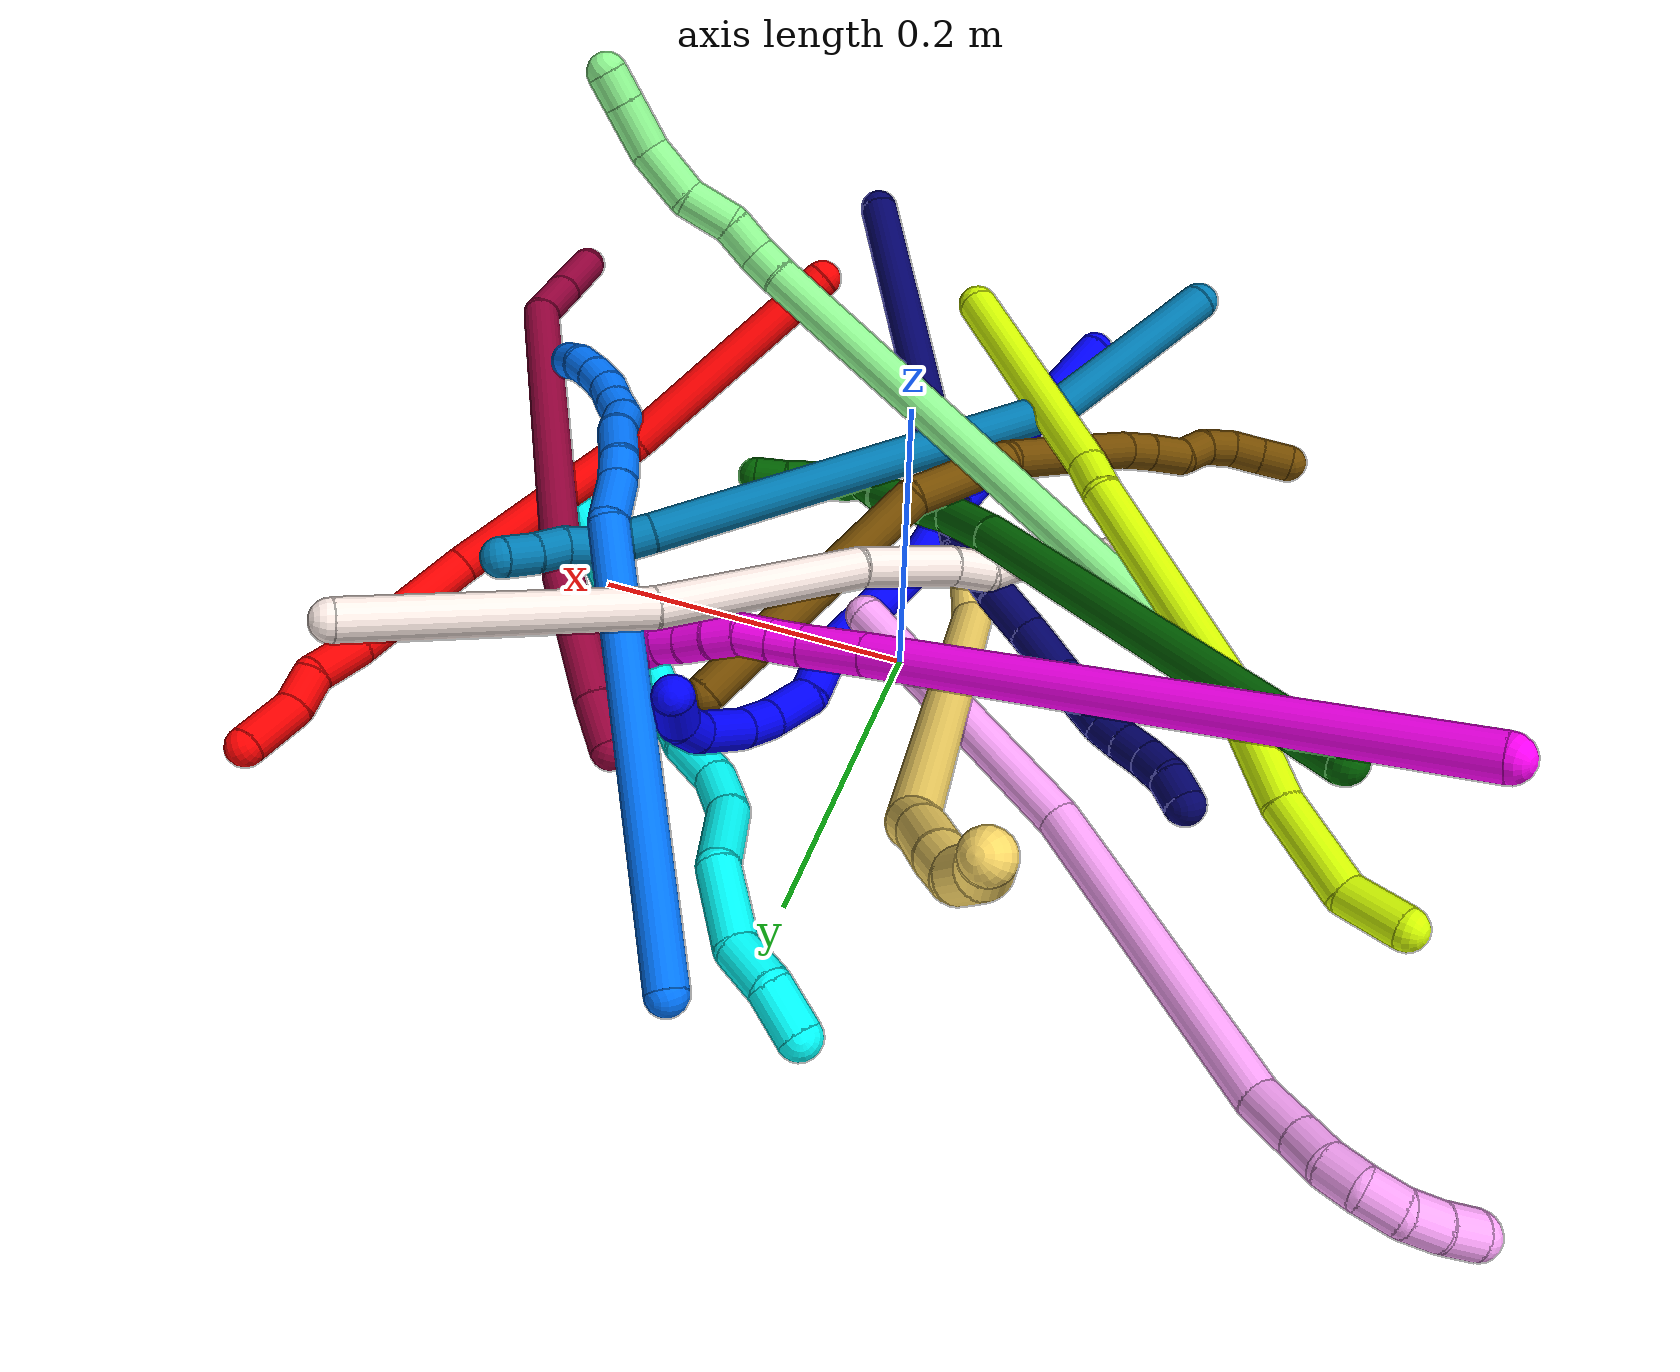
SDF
<sdf version="1.7">
 <world name="default">
  <plugin name="TubeGeneratorPlugin" filename="libtube_generator_plugin.so"/>
  <model name="photoneo_s_sensor">
   <static>1</static>
   <pose>0 0 2 1.57079 1.57079 3.14159</pose>
   <link name="link">
    <inertial><mass>0.1</mass></inertial>
    <sensor name="sensor" type="depth">
     <update_rate>30</update_rate>
     <camera>
      <horizontal_fov>1.22</horizontal_fov>
      <image><width>1920</width><height>1200</height><format>B8G8R8</format></image>
      <clip><near>0.1</near><far>4</far></clip>
      <depth_camera><output>points</output></depth_camera>
     </camera>
     <plugin name="camera_plugin" filename="libgazebo_ros_depth_camera.so">
      <baseline>0.2</baseline>
      <alwaysOn>1</alwaysOn>
      <updateRate>0.0</updateRate>
      <cameraName>camera_ir</cameraName>
      <imageTopicName>/camera/color/image_raw</imageTopicName>
      <cameraInfoTopicName>/camera/color/camera_info</cameraInfoTopicName>
      <depthImageTopicName>/camera/depth/image_raw</depthImageTopicName>
      <depthImageCameraInfoTopicName>/camera/depth/camera_info</depthImageCameraInfoTopicName>
      <pointCloudTopicName>/camera/depth/points</pointCloudTopicName>
      <frameName>fr_optical</frameName>
      <pointCloudCutoff>0.1</pointCloudCutoff>
      <pointCloudCutoffMax>2.0</pointCloudCutoffMax>
      <distortionK1>0</distortionK1>
      <distortionK2>0</distortionK2>
      <distortionK3>0</distortionK3>
      <distortionT1>0</distortionT1>
      <distortionT2>0</distortionT2>
      <CxPrime>0</CxPrime>
      <Cx>0</Cx>
      <Cy>0</Cy>
      <focalLength>0</focalLength>
      <hackBaseline>0</hackBaseline>
     </plugin>
    </sensor>
   </link>
  </model>
  <gravity>0 0 -9.8</gravity>
  <magnetic_field>6e-06 2.3e-05 -4.2e-05</magnetic_field>
  <atmosphere type="adiabatic"/>
  <physics name="default_physics" default="0" type="ode">
   <max_step_size>0.003</max_step_size>
   <real_time_factor>1</real_time_factor>
   <real_time_update_rate>1000</real_time_update_rate>
   <max_contacts>10000</max_contacts>
   <ode>
    <solver>
     <type>quick</type>
     <iters>100</iters>
     <sor>1.3</sor>
     <use_dynamic_moi_rescaling>0</use_dynamic_moi_rescaling>
    </solver>
    <constraints>
     <contact_max_correcting_vel>0</contact_max_correcting_vel>
     <contact_surface_layer>0.001</contact_surface_layer>
     <cfm>0</cfm>
     <erp>0.2</erp>
    </constraints>
   </ode>
  </physics>
  <scene><ambient>0.4 0.4 0.4 1</ambient><background>0.7 0.7 0.7 1</background><shadows>0</shadows></scene>
  <audio><device>default</device></audio>
  <spherical_coordinates>
   <surface_model>EARTH_WGS84</surface_model>
   <latitude_deg>0</latitude_deg>
   <longitude_deg>0</longitude_deg>
   <elevation>0</elevation>
   <heading_deg>0</heading_deg>
  </spherical_coordinates>
  <model name="bin">
   <static>1</static>
   <link name="bottom">
    <collision name="collision-bottom">
     <pose>0 0 -0.01 0 -0 0</pose>
     <geometry><box><size>0.8 0.6 0.02</size></box></geometry>
     <surface>
      <friction><ode><mu>100</mu><mu2>100</mu2></ode></friction>
      <contact><collide_bitmask>65535</collide_bitmask></contact>
     </surface>
    </collision>
   </link>
   <link name="west_wall">
    <collision name="collision-west_wall">
     <pose>-0.41 0 0.1 0 -0 0</pose>
     <geometry><box><size>0.02 0.6 0.2</size></box></geometry>
     <surface>
      <friction><ode><mu>100</mu><mu2>100</mu2></ode></friction>
      <contact><collide_bitmask>65535</collide_bitmask></contact>
     </surface>
    </collision>
   </link>
   <link name="east_wall">
    <collision name="collision-east_wall">
     <pose>0.41 0 0.1 0 -0 0</pose>
     <geometry><box><size>0.02 0.6 0.2</size></box></geometry>
     <surface>
      <friction><ode><mu>100</mu><mu2>100</mu2></ode></friction>
      <contact><collide_bitmask>65535</collide_bitmask></contact>
     </surface>
    </collision>
   </link>
   <link name="south_wall">
    <collision name="collision-south_wall">
     <pose>0 -0.31 0.1 0 -0 0</pose>
     <geometry><box><size>0.8 0.02 0.2</size></box></geometry>
     <surface>
      <friction><ode><mu>100</mu><mu2>100</mu2></ode></friction>
      <contact><collide_bitmask>65535</collide_bitmask></contact>
     </surface>
    </collision>
   </link>
   <link name="north_wall">
    <collision name="collision-north_wall">
     <pose>0 0.31 0.1 0 -0 0</pose>
     <geometry><box><size>0.8 0.02 0.2</size></box></geometry>
     <surface>
      <friction><ode><mu>100</mu><mu2>100</mu2></ode></friction>
      <contact><collide_bitmask>65535</collide_bitmask></contact>
     </surface>
    </collision>
   </link>
  </model>
  <model name="1">
   <static>0</static>
   <link name="1">
    <collision name="collision-cylinder-e_1_1_4">
     <pose>0.020913 0.074035 -0.047108 -2.13747 0.233951 -0.421746</pose>
     <geometry><cylinder><radius>0.0125</radius><length>0.180419</length></cylinder></geometry>
     <surface>
      <friction><ode><mu>1.16</mu><mu2>1.16</mu2><slip1>0</slip1><slip2>0</slip2></ode></friction>
      <contact><ode><kp>1e+06</kp><kd>1</kd><max_vel>0</max_vel><min_depth>0.001</min_depth></ode></contact>
     </surface>
    </collision>
    <visual name="visual-cylinder-e_1_1_4">
     <pose>0.020913 0.074035 -0.047108 -2.13747 0.233951 -0.421746</pose>
     <geometry><cylinder><radius>0.0125</radius><length>0.180419</length></cylinder></geometry>
     <material><ambient>0 0 1 1</ambient></material>
    </visual>
    <collision name="collision-cylinder-e_2_4_5">
     <pose>0.051817 0.16908 -0.110499 -2.23011 0.359557 -0.71013</pose>
     <geometry><cylinder><radius>0.0125</radius><length>0.056792</length></cylinder></geometry>
     <surface>
      <friction><ode><mu>1.16</mu><mu2>1.16</mu2><slip1>0</slip1><slip2>0</slip2></ode></friction>
      <contact><ode><kp>1e+06</kp><kd>1</kd><max_vel>0</max_vel><min_depth>0.001</min_depth></ode></contact>
     </surface>
    </collision>
    <visual name="visual-cylinder-e_2_4_5">
     <pose>0.051817 0.16908 -0.110499 -2.23011 0.359557 -0.71013</pose>
     <geometry><cylinder><radius>0.0125</radius><length>0.056792</length></cylinder></geometry>
     <material><ambient>0 0 1 1</ambient></material>
    </visual>
    <collision name="collision-cylinder-e_3_5_6">
     <pose>0.069353 0.225449 -0.151511 -2.18111 0.173112 -0.330122</pose>
     <geometry><cylinder><radius>0.0125</radius><length>0.087609</length></cylinder></geometry>
     <surface>
      <friction><ode><mu>1.16</mu><mu2>1.16</mu2><slip1>0</slip1><slip2>0</slip2></ode></friction>
      <contact><ode><kp>1e+06</kp><kd>1</kd><max_vel>0</max_vel><min_depth>0.001</min_depth></ode></contact>
     </surface>
    </collision>
    <visual name="visual-cylinder-e_3_5_6">
     <pose>0.069353 0.225449 -0.151511 -2.18111 0.173112 -0.330122</pose>
     <geometry><cylinder><radius>0.0125</radius><length>0.087609</length></cylinder></geometry>
     <material><ambient>0 0 1 1</ambient></material>
    </visual>
    <collision name="collision-cylinder-e_4_6_7">
     <pose>0.084225 0.271859 -0.18739 -2.36069 0.436683 -0.988849</pose>
     <geometry><cylinder><radius>0.0125</radius><length>0.034646</length></cylinder></geometry>
     <surface>
      <friction><ode><mu>1.16</mu><mu2>1.16</mu2><slip1>0</slip1><slip2>0</slip2></ode></friction>
      <contact><ode><kp>1e+06</kp><kd>1</kd><max_vel>0</max_vel><min_depth>0.001</min_depth></ode></contact>
     </surface>
    </collision>
    <visual name="visual-cylinder-e_4_6_7">
     <pose>0.084225 0.271859 -0.18739 -2.36069 0.436683 -0.988849</pose>
     <geometry><cylinder><radius>0.0125</radius><length>0.034646</length></cylinder></geometry>
     <material><ambient>0 0 1 1</ambient></material>
    </visual>
    <collision name="collision-cylinder-e_5_7_8">
     <pose>0.090918 0.295934 -0.20763 -2.18011 -0.039903 0.076481</pose>
     <geometry><cylinder><radius>0.0125</radius><length>0.031793</length></cylinder></geometry>
     <surface>
      <friction><ode><mu>1.16</mu><mu2>1.16</mu2><slip1>0</slip1><slip2>0</slip2></ode></friction>
      <contact><ode><kp>1e+06</kp><kd>1</kd><max_vel>0</max_vel><min_depth>0.001</min_depth></ode></contact>
     </surface>
    </collision>
    <visual name="visual-cylinder-e_5_7_8">
     <pose>0.090918 0.295934 -0.20763 -2.18011 -0.039903 0.076481</pose>
     <geometry><cylinder><radius>0.0125</radius><length>0.031793</length></cylinder></geometry>
     <material><ambient>0 0 1 1</ambient></material>
    </visual>
    <collision name="collision-cylinder-e_6_8_9">
     <pose>0.087761 0.316705 -0.226557 -2.47457 -0.198856 0.560708</pose>
     <geometry><cylinder><radius>0.0125</radius><length>0.025543</length></cylinder></geometry>
     <surface>
      <friction><ode><mu>1.16</mu><mu2>1.16</mu2><slip1>0</slip1><slip2>0</slip2></ode></friction>
      <contact><ode><kp>1e+06</kp><kd>1</kd><max_vel>0</max_vel><min_depth>0.001</min_depth></ode></contact>
     </surface>
    </collision>
    <visual name="visual-cylinder-e_6_8_9">
     <pose>0.087761 0.316705 -0.226557 -2.47457 -0.198856 0.560708</pose>
     <geometry><cylinder><radius>0.0125</radius><length>0.025543</length></cylinder></geometry>
     <material><ambient>0 0 1 1</ambient></material>
    </visual>
    <collision name="collision-cylinder-e_7_9_10">
     <pose>0.078616 0.333956 -0.250869 -2.56055 -0.365191 1.10654</pose>
     <geometry><cylinder><radius>0.0125</radius><length>0.03708</length></cylinder></geometry>
     <surface>
      <friction><ode><mu>1.16</mu><mu2>1.16</mu2><slip1>0</slip1><slip2>0</slip2></ode></friction>
      <contact><ode><kp>1e+06</kp><kd>1</kd><max_vel>0</max_vel><min_depth>0.001</min_depth></ode></contact>
     </surface>
    </collision>
    <visual name="visual-cylinder-e_7_9_10">
     <pose>0.078616 0.333956 -0.250869 -2.56055 -0.365191 1.10654</pose>
     <geometry><cylinder><radius>0.0125</radius><length>0.03708</length></cylinder></geometry>
     <material><ambient>0 0 1 1</ambient></material>
    </visual>
    <collision name="collision-cylinder-e_8_10_11">
     <pose>0.06613 0.345325 -0.274194 -2.93399 -0.575356 2.46454</pose>
     <geometry><cylinder><radius>0.0125</radius><length>0.021558</length></cylinder></geometry>
     <surface>
      <friction><ode><mu>1.16</mu><mu2>1.16</mu2><slip1>0</slip1><slip2>0</slip2></ode></friction>
      <contact><ode><kp>1e+06</kp><kd>1</kd><max_vel>0</max_vel><min_depth>0.001</min_depth></ode></contact>
     </surface>
    </collision>
    <visual name="visual-cylinder-e_8_10_11">
     <pose>0.06613 0.345325 -0.274194 -2.93399 -0.575356 2.46454</pose>
     <geometry><cylinder><radius>0.0125</radius><length>0.021558</length></cylinder></geometry>
     <material><ambient>0 0 1 1</ambient></material>
    </visual>
    <collision name="collision-cylinder-e_9_11_2">
     <pose>0.053005 0.343314 -0.292157 2.73957 -0.63258 -2.02786</pose>
     <geometry><cylinder><radius>0.0125</radius><length>0.02456</length></cylinder></geometry>
     <surface>
      <friction><ode><mu>1.16</mu><mu2>1.16</mu2><slip1>0</slip1><slip2>0</slip2></ode></friction>
      <contact><ode><kp>1e+06</kp><kd>1</kd><max_vel>0</max_vel><min_depth>0.001</min_depth></ode></contact>
     </surface>
    </collision>
    <visual name="visual-cylinder-e_9_11_2">
     <pose>0.053005 0.343314 -0.292157 2.73957 -0.63258 -2.02786</pose>
     <geometry><cylinder><radius>0.0125</radius><length>0.02456</length></cylinder></geometry>
     <material><ambient>0 0 1 1</ambient></material>
    </visual>
    <collision name="collision-sphere-2">
     <pose>0.045744 0.339439 -0.301272 0 -0 0</pose>
     <geometry><sphere><radius>0.0125</radius></sphere></geometry>
     <surface>
      <friction><ode><mu>1.16</mu><mu2>1.16</mu2><slip1>0</slip1><slip2>0</slip2></ode></friction>
      <contact><ode><kp>1e+06</kp><kd>1</kd><max_vel>0</max_vel><min_depth>0.001</min_depth></ode></contact>
     </surface>
    </collision>
    <visual name="visual-sphere-2">
     <pose>0.045744 0.339439 -0.301272 0 -0 0</pose>
     <geometry><sphere><radius>0.0125</radius></sphere></geometry>
     <material><ambient>0 0 1 1</ambient></material>
    </visual>
    <collision name="collision-sphere-11">
     <pose>0.060265 0.347189 -0.283043 0 -0 0</pose>
     <geometry><sphere><radius>0.0125</radius></sphere></geometry>
     <surface>
      <friction><ode><mu>1.16</mu><mu2>1.16</mu2><slip1>0</slip1><slip2>0</slip2></ode></friction>
      <contact><ode><kp>1e+06</kp><kd>1</kd><max_vel>0</max_vel><min_depth>0.001</min_depth></ode></contact>
     </surface>
    </collision>
    <visual name="visual-sphere-11">
     <pose>0.060265 0.347189 -0.283043 0 -0 0</pose>
     <geometry><sphere><radius>0.0125</radius></sphere></geometry>
     <material><ambient>0 0 1 1</ambient></material>
    </visual>
    <collision name="collision-sphere-10">
     <pose>0.071995 0.343461 -0.265344 0 -0 0</pose>
     <geometry><sphere><radius>0.0125</radius></sphere></geometry>
     <surface>
      <friction><ode><mu>1.16</mu><mu2>1.16</mu2><slip1>0</slip1><slip2>0</slip2></ode></friction>
      <contact><ode><kp>1e+06</kp><kd>1</kd><max_vel>0</max_vel><min_depth>0.001</min_depth></ode></contact>
     </surface>
    </collision>
    <visual name="visual-sphere-10">
     <pose>0.071995 0.343461 -0.265344 0 -0 0</pose>
     <geometry><sphere><radius>0.0125</radius></sphere></geometry>
     <material><ambient>0 0 1 1</ambient></material>
    </visual>
    <collision name="collision-sphere-9">
     <pose>0.085238 0.32445 -0.236393 0 -0 0</pose>
     <geometry><sphere><radius>0.0125</radius></sphere></geometry>
     <surface>
      <friction><ode><mu>1.16</mu><mu2>1.16</mu2><slip1>0</slip1><slip2>0</slip2></ode></friction>
      <contact><ode><kp>1e+06</kp><kd>1</kd><max_vel>0</max_vel><min_depth>0.001</min_depth></ode></contact>
     </surface>
    </collision>
    <visual name="visual-sphere-9">
     <pose>0.085238 0.32445 -0.236393 0 -0 0</pose>
     <geometry><sphere><radius>0.0125</radius></sphere></geometry>
     <material><ambient>0 0 1 1</ambient></material>
    </visual>
    <collision name="collision-sphere-4">
     <pose>0.041825 0.148071 -0.094216 0 -0 0</pose>
     <geometry><sphere><radius>0.0125</radius></sphere></geometry>
     <surface>
      <friction><ode><mu>1.16</mu><mu2>1.16</mu2><slip1>0</slip1><slip2>0</slip2></ode></friction>
      <contact><ode><kp>1e+06</kp><kd>1</kd><max_vel>0</max_vel><min_depth>0.001</min_depth></ode></contact>
     </surface>
    </collision>
    <visual name="visual-sphere-4">
     <pose>0.041825 0.148071 -0.094216 0 -0 0</pose>
     <geometry><sphere><radius>0.0125</radius></sphere></geometry>
     <material><ambient>0 0 1 1</ambient></material>
    </visual>
    <collision name="collision-sphere-1">
     <geometry><sphere><radius>0.0125</radius></sphere></geometry>
     <surface>
      <friction><ode><mu>1.16</mu><mu2>1.16</mu2><slip1>0</slip1><slip2>0</slip2></ode></friction>
      <contact><ode><kp>1e+06</kp><kd>1</kd><max_vel>0</max_vel><min_depth>0.001</min_depth></ode></contact>
     </surface>
    </collision>
    <visual name="visual-sphere-1">
     <geometry><sphere><radius>0.0125</radius></sphere></geometry>
     <material><ambient>0 0 1 1</ambient></material>
    </visual>
    <collision name="collision-sphere-8">
     <pose>0.090283 0.30896 -0.216721 0 -0 0</pose>
     <geometry><sphere><radius>0.0125</radius></sphere></geometry>
     <surface>
      <friction><ode><mu>1.16</mu><mu2>1.16</mu2><slip1>0</slip1><slip2>0</slip2></ode></friction>
      <contact><ode><kp>1e+06</kp><kd>1</kd><max_vel>0</max_vel><min_depth>0.001</min_depth></ode></contact>
     </surface>
    </collision>
    <visual name="visual-sphere-8">
     <pose>0.090283 0.30896 -0.216721 0 -0 0</pose>
     <geometry><sphere><radius>0.0125</radius></sphere></geometry>
     <material><ambient>0 0 1 1</ambient></material>
    </visual>
    <collision name="collision-sphere-5">
     <pose>0.061808 0.19009 -0.126781 0 -0 0</pose>
     <geometry><sphere><radius>0.0125</radius></sphere></geometry>
     <surface>
      <friction><ode><mu>1.16</mu><mu2>1.16</mu2><slip1>0</slip1><slip2>0</slip2></ode></friction>
      <contact><ode><kp>1e+06</kp><kd>1</kd><max_vel>0</max_vel><min_depth>0.001</min_depth></ode></contact>
     </surface>
    </collision>
    <visual name="visual-sphere-5">
     <pose>0.061808 0.19009 -0.126781 0 -0 0</pose>
     <geometry><sphere><radius>0.0125</radius></sphere></geometry>
     <material><ambient>0 0 1 1</ambient></material>
    </visual>
    <collision name="collision-sphere-6">
     <pose>0.076899 0.260809 -0.176241 0 -0 0</pose>
     <geometry><sphere><radius>0.0125</radius></sphere></geometry>
     <surface>
      <friction><ode><mu>1.16</mu><mu2>1.16</mu2><slip1>0</slip1><slip2>0</slip2></ode></friction>
      <contact><ode><kp>1e+06</kp><kd>1</kd><max_vel>0</max_vel><min_depth>0.001</min_depth></ode></contact>
     </surface>
    </collision>
    <visual name="visual-sphere-6">
     <pose>0.076899 0.260809 -0.176241 0 -0 0</pose>
     <geometry><sphere><radius>0.0125</radius></sphere></geometry>
     <material><ambient>0 0 1 1</ambient></material>
    </visual>
    <collision name="collision-sphere-7">
     <pose>0.091552 0.282909 -0.19854 0 -0 0</pose>
     <geometry><sphere><radius>0.0125</radius></sphere></geometry>
     <surface>
      <friction><ode><mu>1.16</mu><mu2>1.16</mu2><slip1>0</slip1><slip2>0</slip2></ode></friction>
      <contact><ode><kp>1e+06</kp><kd>1</kd><max_vel>0</max_vel><min_depth>0.001</min_depth></ode></contact>
     </surface>
    </collision>
    <visual name="visual-sphere-7">
     <pose>0.091552 0.282909 -0.19854 0 -0 0</pose>
     <geometry><sphere><radius>0.0125</radius></sphere></geometry>
     <material><ambient>0 0 1 1</ambient></material>
    </visual>
    <inertial>
     <pose>0.052969 0.195775 -0.138635 0 -0 0</pose>
     <mass>0.5</mass>
     <inertia>
      <ixx>0.000295</ixx>
      <ixy>0</ixy>
      <ixz>0</ixz>
      <iyy>-0.000439</iyy>
      <iyz>0</iyz>
      <izz>-0.000631</izz>
     </inertia>
    </inertial>
   </link>
   <pose>-0.046843 -0.288503 0.053385 -2.59313 0.696119 2.65699</pose>
  </model>
  <model name="2">
   <static>0</static>
   <link name="2">
    <collision name="collision-cylinder-e_1_1_4">
     <pose>0.036446 0.018978 0.072016 -0.257671 0.45511 -0.059982</pose>
     <geometry><cylinder><radius>0.0125</radius><length>0.165829</length></cylinder></geometry>
     <surface>
      <friction><ode><mu>1.16</mu><mu2>1.16</mu2><slip1>0</slip1><slip2>0</slip2></ode></friction>
      <contact><ode><kp>1e+06</kp><kd>1</kd><max_vel>0</max_vel><min_depth>0.001</min_depth></ode></contact>
     </surface>
    </collision>
    <visual name="visual-cylinder-e_1_1_4">
     <pose>0.036446 0.018978 0.072016 -0.257671 0.45511 -0.059982</pose>
     <geometry><cylinder><radius>0.0125</radius><length>0.165829</length></cylinder></geometry>
     <material><ambient>1 0 0 1</ambient></material>
    </visual>
    <collision name="collision-cylinder-e_2_4_5">
     <pose>0.100207 0.063323 0.203759 -0.401623 0.398435 -0.082148</pose>
     <geometry><cylinder><radius>0.0125</radius><length>0.140811</length></cylinder></geometry>
     <surface>
      <friction><ode><mu>1.16</mu><mu2>1.16</mu2><slip1>0</slip1><slip2>0</slip2></ode></friction>
      <contact><ode><kp>1e+06</kp><kd>1</kd><max_vel>0</max_vel><min_depth>0.001</min_depth></ode></contact>
     </surface>
    </collision>
    <visual name="visual-cylinder-e_2_4_5">
     <pose>0.100207 0.063323 0.203759 -0.401623 0.398435 -0.082148</pose>
     <geometry><cylinder><radius>0.0125</radius><length>0.140811</length></cylinder></geometry>
     <material><ambient>1 0 0 1</ambient></material>
    </visual>
    <collision name="collision-cylinder-e_3_5_6">
     <pose>0.151952 0.118428 0.288609 -0.869343 0.560408 -0.265647</pose>
     <geometry><cylinder><radius>0.0125</radius><length>0.09192</length></cylinder></geometry>
     <surface>
      <friction><ode><mu>1.16</mu><mu2>1.16</mu2><slip1>0</slip1><slip2>0</slip2></ode></friction>
      <contact><ode><kp>1e+06</kp><kd>1</kd><max_vel>0</max_vel><min_depth>0.001</min_depth></ode></contact>
     </surface>
    </collision>
    <visual name="visual-cylinder-e_3_5_6">
     <pose>0.151952 0.118428 0.288609 -0.869343 0.560408 -0.265647</pose>
     <geometry><cylinder><radius>0.0125</radius><length>0.09192</length></cylinder></geometry>
     <material><ambient>1 0 0 1</ambient></material>
    </visual>
    <collision name="collision-cylinder-e_4_6_7">
     <pose>0.184764 0.162734 0.321548 -1.0783 0.469316 -0.284122</pose>
     <geometry><cylinder><radius>0.0125</radius><length>0.03707</length></cylinder></geometry>
     <surface>
      <friction><ode><mu>1.16</mu><mu2>1.16</mu2><slip1>0</slip1><slip2>0</slip2></ode></friction>
      <contact><ode><kp>1e+06</kp><kd>1</kd><max_vel>0</max_vel><min_depth>0.001</min_depth></ode></contact>
     </surface>
    </collision>
    <visual name="visual-cylinder-e_4_6_7">
     <pose>0.184764 0.162734 0.321548 -1.0783 0.469316 -0.284122</pose>
     <geometry><cylinder><radius>0.0125</radius><length>0.03707</length></cylinder></geometry>
     <material><ambient>1 0 0 1</ambient></material>
    </visual>
    <collision name="collision-cylinder-e_5_7_8">
     <pose>0.202827 0.182755 0.334383 -0.826984 0.917265 -0.426707</pose>
     <geometry><cylinder><radius>0.0125</radius><length>0.024382</length></cylinder></geometry>
     <surface>
      <friction><ode><mu>1.16</mu><mu2>1.16</mu2><slip1>0</slip1><slip2>0</slip2></ode></friction>
      <contact><ode><kp>1e+06</kp><kd>1</kd><max_vel>0</max_vel><min_depth>0.001</min_depth></ode></contact>
     </surface>
    </collision>
    <visual name="visual-cylinder-e_5_7_8">
     <pose>0.202827 0.182755 0.334383 -0.826984 0.917265 -0.426707</pose>
     <geometry><cylinder><radius>0.0125</radius><length>0.024382</length></cylinder></geometry>
     <material><ambient>1 0 0 1</ambient></material>
    </visual>
    <collision name="collision-cylinder-e_6_8_2">
     <pose>0.223385 0.202799 0.347679 -1.05474 0.57538 -0.341303</pose>
     <geometry><cylinder><radius>0.0125</radius><length>0.039988</length></cylinder></geometry>
     <surface>
      <friction><ode><mu>1.16</mu><mu2>1.16</mu2><slip1>0</slip1><slip2>0</slip2></ode></friction>
      <contact><ode><kp>1e+06</kp><kd>1</kd><max_vel>0</max_vel><min_depth>0.001</min_depth></ode></contact>
     </surface>
    </collision>
    <visual name="visual-cylinder-e_6_8_2">
     <pose>0.223385 0.202799 0.347679 -1.05474 0.57538 -0.341303</pose>
     <geometry><cylinder><radius>0.0125</radius><length>0.039988</length></cylinder></geometry>
     <material><ambient>1 0 0 1</ambient></material>
    </visual>
    <collision name="collision-sphere-2">
     <pose>0.234265 0.217389 0.355957 0 -0 0</pose>
     <geometry><sphere><radius>0.0125</radius></sphere></geometry>
     <surface>
      <friction><ode><mu>1.16</mu><mu2>1.16</mu2><slip1>0</slip1><slip2>0</slip2></ode></friction>
      <contact><ode><kp>1e+06</kp><kd>1</kd><max_vel>0</max_vel><min_depth>0.001</min_depth></ode></contact>
     </surface>
    </collision>
    <visual name="visual-sphere-2">
     <pose>0.234265 0.217389 0.355957 0 -0 0</pose>
     <geometry><sphere><radius>0.0125</radius></sphere></geometry>
     <material><ambient>1 0 0 1</ambient></material>
    </visual>
    <collision name="collision-sphere-4">
     <pose>0.072892 0.037957 0.144032 0 -0 0</pose>
     <geometry><sphere><radius>0.0125</radius></sphere></geometry>
     <surface>
      <friction><ode><mu>1.16</mu><mu2>1.16</mu2><slip1>0</slip1><slip2>0</slip2></ode></friction>
      <contact><ode><kp>1e+06</kp><kd>1</kd><max_vel>0</max_vel><min_depth>0.001</min_depth></ode></contact>
     </surface>
    </collision>
    <visual name="visual-sphere-4">
     <pose>0.072892 0.037957 0.144032 0 -0 0</pose>
     <geometry><sphere><radius>0.0125</radius></sphere></geometry>
     <material><ambient>1 0 0 1</ambient></material>
    </visual>
    <collision name="collision-sphere-1">
     <geometry><sphere><radius>0.0125</radius></sphere></geometry>
     <surface>
      <friction><ode><mu>1.16</mu><mu2>1.16</mu2><slip1>0</slip1><slip2>0</slip2></ode></friction>
      <contact><ode><kp>1e+06</kp><kd>1</kd><max_vel>0</max_vel><min_depth>0.001</min_depth></ode></contact>
     </surface>
    </collision>
    <visual name="visual-sphere-1">
     <geometry><sphere><radius>0.0125</radius></sphere></geometry>
     <material><ambient>1 0 0 1</ambient></material>
    </visual>
    <collision name="collision-sphere-8">
     <pose>0.212506 0.188209 0.339402 0 -0 0</pose>
     <geometry><sphere><radius>0.0125</radius></sphere></geometry>
     <surface>
      <friction><ode><mu>1.16</mu><mu2>1.16</mu2><slip1>0</slip1><slip2>0</slip2></ode></friction>
      <contact><ode><kp>1e+06</kp><kd>1</kd><max_vel>0</max_vel><min_depth>0.001</min_depth></ode></contact>
     </surface>
    </collision>
    <visual name="visual-sphere-8">
     <pose>0.212506 0.188209 0.339402 0 -0 0</pose>
     <geometry><sphere><radius>0.0125</radius></sphere></geometry>
     <material><ambient>1 0 0 1</ambient></material>
    </visual>
    <collision name="collision-sphere-5">
     <pose>0.127523 0.08869 0.263486 0 -0 0</pose>
     <geometry><sphere><radius>0.0125</radius></sphere></geometry>
     <surface>
      <friction><ode><mu>1.16</mu><mu2>1.16</mu2><slip1>0</slip1><slip2>0</slip2></ode></friction>
      <contact><ode><kp>1e+06</kp><kd>1</kd><max_vel>0</max_vel><min_depth>0.001</min_depth></ode></contact>
     </surface>
    </collision>
    <visual name="visual-sphere-5">
     <pose>0.127523 0.08869 0.263486 0 -0 0</pose>
     <geometry><sphere><radius>0.0125</radius></sphere></geometry>
     <material><ambient>1 0 0 1</ambient></material>
    </visual>
    <collision name="collision-sphere-6">
     <pose>0.176381 0.148167 0.313731 0 -0 0</pose>
     <geometry><sphere><radius>0.0125</radius></sphere></geometry>
     <surface>
      <friction><ode><mu>1.16</mu><mu2>1.16</mu2><slip1>0</slip1><slip2>0</slip2></ode></friction>
      <contact><ode><kp>1e+06</kp><kd>1</kd><max_vel>0</max_vel><min_depth>0.001</min_depth></ode></contact>
     </surface>
    </collision>
    <visual name="visual-sphere-6">
     <pose>0.176381 0.148167 0.313731 0 -0 0</pose>
     <geometry><sphere><radius>0.0125</radius></sphere></geometry>
     <material><ambient>1 0 0 1</ambient></material>
    </visual>
    <collision name="collision-sphere-7">
     <pose>0.193147 0.1773 0.329364 0 -0 0</pose>
     <geometry><sphere><radius>0.0125</radius></sphere></geometry>
     <surface>
      <friction><ode><mu>1.16</mu><mu2>1.16</mu2><slip1>0</slip1><slip2>0</slip2></ode></friction>
      <contact><ode><kp>1e+06</kp><kd>1</kd><max_vel>0</max_vel><min_depth>0.001</min_depth></ode></contact>
     </surface>
    </collision>
    <visual name="visual-sphere-7">
     <pose>0.193147 0.1773 0.329364 0 -0 0</pose>
     <geometry><sphere><radius>0.0125</radius></sphere></geometry>
     <material><ambient>1 0 0 1</ambient></material>
    </visual>
    <inertial>
     <pose>0.109698 0.083095 0.202277 0 -0 0</pose>
     <mass>0.5</mass>
     <inertia>
      <ixx>0.000593</ixx>
      <ixy>0</ixy>
      <ixz>0</ixz>
      <iyy>0.000615</iyy>
      <iyz>0</iyz>
      <izz>-0.000508</izz>
     </inertia>
    </inertial>
   </link>
   <pose>0.127476 -0.204652 0.125121 2.11398 0.479322 2.22743</pose>
  </model>
  <model name="3">
   <static>0</static>
   <link name="3">
    <collision name="collision-cylinder-e_1_1_4">
     <pose>-0.033278 0.033697 0.031546 -0.818345 -0.624642 0.278231</pose>
     <geometry><cylinder><radius>0.0125</radius><length>0.113807</length></cylinder></geometry>
     <surface>
      <friction><ode><mu>1.16</mu><mu2>1.16</mu2><slip1>0</slip1><slip2>0</slip2></ode></friction>
      <contact><ode><kp>1e+06</kp><kd>1</kd><max_vel>0</max_vel><min_depth>0.001</min_depth></ode></contact>
     </surface>
    </collision>
    <visual name="visual-cylinder-e_1_1_4">
     <pose>-0.033278 0.033697 0.031546 -0.818345 -0.624642 0.278231</pose>
     <geometry><cylinder><radius>0.0125</radius><length>0.113807</length></cylinder></geometry>
     <material><ambient>0.003922 1 0.996078 1</ambient></material>
    </visual>
    <collision name="collision-cylinder-e_2_4_5">
     <pose>-0.112471 0.11694 0.100061 -0.929783 -0.638847 0.328785</pose>
     <geometry><cylinder><radius>0.0125</radius><length>0.154011</length></cylinder></geometry>
     <surface>
      <friction><ode><mu>1.16</mu><mu2>1.16</mu2><slip1>0</slip1><slip2>0</slip2></ode></friction>
      <contact><ode><kp>1e+06</kp><kd>1</kd><max_vel>0</max_vel><min_depth>0.001</min_depth></ode></contact>
     </surface>
    </collision>
    <visual name="visual-cylinder-e_2_4_5">
     <pose>-0.112471 0.11694 0.100061 -0.929783 -0.638847 0.328785</pose>
     <geometry><cylinder><radius>0.0125</radius><length>0.154011</length></cylinder></geometry>
     <material><ambient>0.003922 1 0.996078 1</ambient></material>
    </visual>
    <collision name="collision-cylinder-e_3_5_6">
     <pose>-0.170806 0.173697 0.145405 -0.710694 -0.843567 0.330007</pose>
     <geometry><cylinder><radius>0.0125</radius><length>0.033248</length></cylinder></geometry>
     <surface>
      <friction><ode><mu>1.16</mu><mu2>1.16</mu2><slip1>0</slip1><slip2>0</slip2></ode></friction>
      <contact><ode><kp>1e+06</kp><kd>1</kd><max_vel>0</max_vel><min_depth>0.001</min_depth></ode></contact>
     </surface>
    </collision>
    <visual name="visual-cylinder-e_3_5_6">
     <pose>-0.170806 0.173697 0.145405 -0.710694 -0.843567 0.330007</pose>
     <geometry><cylinder><radius>0.0125</radius><length>0.033248</length></cylinder></geometry>
     <material><ambient>0.003922 1 0.996078 1</ambient></material>
    </visual>
    <collision name="collision-cylinder-e_4_6_7">
     <pose>-0.190839 0.190338 0.164587 -0.717565 -0.48808 0.186219</pose>
     <geometry><cylinder><radius>0.0125</radius><length>0.032478</length></cylinder></geometry>
     <surface>
      <friction><ode><mu>1.16</mu><mu2>1.16</mu2><slip1>0</slip1><slip2>0</slip2></ode></friction>
      <contact><ode><kp>1e+06</kp><kd>1</kd><max_vel>0</max_vel><min_depth>0.001</min_depth></ode></contact>
     </surface>
    </collision>
    <visual name="visual-cylinder-e_4_6_7">
     <pose>-0.190839 0.190338 0.164587 -0.717565 -0.48808 0.186219</pose>
     <geometry><cylinder><radius>0.0125</radius><length>0.032478</length></cylinder></geometry>
     <material><ambient>0.003922 1 0.996078 1</ambient></material>
    </visual>
    <collision name="collision-cylinder-e_5_7_8">
     <pose>-0.201576 0.217037 0.196853 -0.677593 -0.112847 0.039802</pose>
     <geometry><cylinder><radius>0.0125</radius><length>0.055442</length></cylinder></geometry>
     <surface>
      <friction><ode><mu>1.16</mu><mu2>1.16</mu2><slip1>0</slip1><slip2>0</slip2></ode></friction>
      <contact><ode><kp>1e+06</kp><kd>1</kd><max_vel>0</max_vel><min_depth>0.001</min_depth></ode></contact>
     </surface>
    </collision>
    <visual name="visual-cylinder-e_5_7_8">
     <pose>-0.201576 0.217037 0.196853 -0.677593 -0.112847 0.039802</pose>
     <geometry><cylinder><radius>0.0125</radius><length>0.055442</length></cylinder></geometry>
     <material><ambient>0.003922 1 0.996078 1</ambient></material>
    </visual>
    <collision name="collision-cylinder-e_6_8_9">
     <pose>-0.216807 0.253373 0.230854 -0.989015 -0.487823 0.26678</pose>
     <geometry><cylinder><radius>0.0125</radius><length>0.051672</length></cylinder></geometry>
     <surface>
      <friction><ode><mu>1.16</mu><mu2>1.16</mu2><slip1>0</slip1><slip2>0</slip2></ode></friction>
      <contact><ode><kp>1e+06</kp><kd>1</kd><max_vel>0</max_vel><min_depth>0.001</min_depth></ode></contact>
     </surface>
    </collision>
    <visual name="visual-cylinder-e_6_8_9">
     <pose>-0.216807 0.253373 0.230854 -0.989015 -0.487823 0.26678</pose>
     <geometry><cylinder><radius>0.0125</radius><length>0.051672</length></cylinder></geometry>
     <material><ambient>0.003922 1 0.996078 1</ambient></material>
    </visual>
    <collision name="collision-cylinder-e_7_9_10">
     <pose>-0.239954 0.278819 0.250783 -0.71216 -0.84676 0.332124</pose>
     <geometry><cylinder><radius>0.0125</radius><length>0.029469</length></cylinder></geometry>
     <surface>
      <friction><ode><mu>1.16</mu><mu2>1.16</mu2><slip1>0</slip1><slip2>0</slip2></ode></friction>
      <contact><ode><kp>1e+06</kp><kd>1</kd><max_vel>0</max_vel><min_depth>0.001</min_depth></ode></contact>
     </surface>
    </collision>
    <visual name="visual-cylinder-e_7_9_10">
     <pose>-0.239954 0.278819 0.250783 -0.71216 -0.84676 0.332124</pose>
     <geometry><cylinder><radius>0.0125</radius><length>0.029469</length></cylinder></geometry>
     <material><ambient>0.003922 1 0.996078 1</ambient></material>
    </visual>
    <collision name="collision-cylinder-e_8_10_2">
     <pose>-0.262493 0.294401 0.260645 -1.30817 -0.878794 0.691764</pose>
     <geometry><cylinder><radius>0.0125</radius><length>0.029873</length></cylinder></geometry>
     <surface>
      <friction><ode><mu>1.16</mu><mu2>1.16</mu2><slip1>0</slip1><slip2>0</slip2></ode></friction>
      <contact><ode><kp>1e+06</kp><kd>1</kd><max_vel>0</max_vel><min_depth>0.001</min_depth></ode></contact>
     </surface>
    </collision>
    <visual name="visual-cylinder-e_8_10_2">
     <pose>-0.262493 0.294401 0.260645 -1.30817 -0.878794 0.691764</pose>
     <geometry><cylinder><radius>0.0125</radius><length>0.029873</length></cylinder></geometry>
     <material><ambient>0.003922 1 0.996078 1</ambient></material>
    </visual>
    <collision name="collision-sphere-2">
     <pose>-0.273994 0.303605 0.26312 0 -0 0</pose>
     <geometry><sphere><radius>0.0125</radius></sphere></geometry>
     <surface>
      <friction><ode><mu>1.16</mu><mu2>1.16</mu2><slip1>0</slip1><slip2>0</slip2></ode></friction>
      <contact><ode><kp>1e+06</kp><kd>1</kd><max_vel>0</max_vel><min_depth>0.001</min_depth></ode></contact>
     </surface>
    </collision>
    <visual name="visual-sphere-2">
     <pose>-0.273994 0.303605 0.26312 0 -0 0</pose>
     <geometry><sphere><radius>0.0125</radius></sphere></geometry>
     <material><ambient>0.003922 1 0.996078 1</ambient></material>
    </visual>
    <collision name="collision-sphere-10">
     <pose>-0.250992 0.285197 0.258171 0 -0 0</pose>
     <geometry><sphere><radius>0.0125</radius></sphere></geometry>
     <surface>
      <friction><ode><mu>1.16</mu><mu2>1.16</mu2><slip1>0</slip1><slip2>0</slip2></ode></friction>
      <contact><ode><kp>1e+06</kp><kd>1</kd><max_vel>0</max_vel><min_depth>0.001</min_depth></ode></contact>
     </surface>
    </collision>
    <visual name="visual-sphere-10">
     <pose>-0.250992 0.285197 0.258171 0 -0 0</pose>
     <geometry><sphere><radius>0.0125</radius></sphere></geometry>
     <material><ambient>0.003922 1 0.996078 1</ambient></material>
    </visual>
    <collision name="collision-sphere-9">
     <pose>-0.228916 0.272441 0.243395 0 -0 0</pose>
     <geometry><sphere><radius>0.0125</radius></sphere></geometry>
     <surface>
      <friction><ode><mu>1.16</mu><mu2>1.16</mu2><slip1>0</slip1><slip2>0</slip2></ode></friction>
      <contact><ode><kp>1e+06</kp><kd>1</kd><max_vel>0</max_vel><min_depth>0.001</min_depth></ode></contact>
     </surface>
    </collision>
    <visual name="visual-sphere-9">
     <pose>-0.228916 0.272441 0.243395 0 -0 0</pose>
     <geometry><sphere><radius>0.0125</radius></sphere></geometry>
     <material><ambient>0.003922 1 0.996078 1</ambient></material>
    </visual>
    <collision name="collision-sphere-4">
     <pose>-0.066555 0.067393 0.063093 0 -0 0</pose>
     <geometry><sphere><radius>0.0125</radius></sphere></geometry>
     <surface>
      <friction><ode><mu>1.16</mu><mu2>1.16</mu2><slip1>0</slip1><slip2>0</slip2></ode></friction>
      <contact><ode><kp>1e+06</kp><kd>1</kd><max_vel>0</max_vel><min_depth>0.001</min_depth></ode></contact>
     </surface>
    </collision>
    <visual name="visual-sphere-4">
     <pose>-0.066555 0.067393 0.063093 0 -0 0</pose>
     <geometry><sphere><radius>0.0125</radius></sphere></geometry>
     <material><ambient>0.003922 1 0.996078 1</ambient></material>
    </visual>
    <collision name="collision-sphere-1">
     <geometry><sphere><radius>0.0125</radius></sphere></geometry>
     <surface>
      <friction><ode><mu>1.16</mu><mu2>1.16</mu2><slip1>0</slip1><slip2>0</slip2></ode></friction>
      <contact><ode><kp>1e+06</kp><kd>1</kd><max_vel>0</max_vel><min_depth>0.001</min_depth></ode></contact>
     </surface>
    </collision>
    <visual name="visual-sphere-1">
     <geometry><sphere><radius>0.0125</radius></sphere></geometry>
     <material><ambient>0.003922 1 0.996078 1</ambient></material>
    </visual>
    <collision name="collision-sphere-8">
     <pose>-0.204697 0.234306 0.218312 0 -0 0</pose>
     <geometry><sphere><radius>0.0125</radius></sphere></geometry>
     <surface>
      <friction><ode><mu>1.16</mu><mu2>1.16</mu2><slip1>0</slip1><slip2>0</slip2></ode></friction>
      <contact><ode><kp>1e+06</kp><kd>1</kd><max_vel>0</max_vel><min_depth>0.001</min_depth></ode></contact>
     </surface>
    </collision>
    <visual name="visual-sphere-8">
     <pose>-0.204697 0.234306 0.218312 0 -0 0</pose>
     <geometry><sphere><radius>0.0125</radius></sphere></geometry>
     <material><ambient>0.003922 1 0.996078 1</ambient></material>
    </visual>
    <collision name="collision-sphere-5">
     <pose>-0.158387 0.166487 0.137029 0 -0 0</pose>
     <geometry><sphere><radius>0.0125</radius></sphere></geometry>
     <surface>
      <friction><ode><mu>1.16</mu><mu2>1.16</mu2><slip1>0</slip1><slip2>0</slip2></ode></friction>
      <contact><ode><kp>1e+06</kp><kd>1</kd><max_vel>0</max_vel><min_depth>0.001</min_depth></ode></contact>
     </surface>
    </collision>
    <visual name="visual-sphere-5">
     <pose>-0.158387 0.166487 0.137029 0 -0 0</pose>
     <geometry><sphere><radius>0.0125</radius></sphere></geometry>
     <material><ambient>0.003922 1 0.996078 1</ambient></material>
    </visual>
    <collision name="collision-sphere-6">
     <pose>-0.183224 0.180906 0.153781 0 -0 0</pose>
     <geometry><sphere><radius>0.0125</radius></sphere></geometry>
     <surface>
      <friction><ode><mu>1.16</mu><mu2>1.16</mu2><slip1>0</slip1><slip2>0</slip2></ode></friction>
      <contact><ode><kp>1e+06</kp><kd>1</kd><max_vel>0</max_vel><min_depth>0.001</min_depth></ode></contact>
     </surface>
    </collision>
    <visual name="visual-sphere-6">
     <pose>-0.183224 0.180906 0.153781 0 -0 0</pose>
     <geometry><sphere><radius>0.0125</radius></sphere></geometry>
     <material><ambient>0.003922 1 0.996078 1</ambient></material>
    </visual>
    <collision name="collision-sphere-7">
     <pose>-0.198454 0.199769 0.175393 0 -0 0</pose>
     <geometry><sphere><radius>0.0125</radius></sphere></geometry>
     <surface>
      <friction><ode><mu>1.16</mu><mu2>1.16</mu2><slip1>0</slip1><slip2>0</slip2></ode></friction>
      <contact><ode><kp>1e+06</kp><kd>1</kd><max_vel>0</max_vel><min_depth>0.001</min_depth></ode></contact>
     </surface>
    </collision>
    <visual name="visual-sphere-7">
     <pose>-0.198454 0.199769 0.175393 0 -0 0</pose>
     <geometry><sphere><radius>0.0125</radius></sphere></geometry>
     <material><ambient>0.003922 1 0.996078 1</ambient></material>
    </visual>
    <inertial>
     <pose>-0.140555 0.151877 0.134399 0 -0 0</pose>
     <mass>0.5</mass>
     <inertia><ixx>0.000468</ixx><ixy>0</ixy><ixz>0</ixz><iyy>0.000496</iyy><iyz>0</iyz><izz>-5e-06</izz></inertia>
    </inertial>
   </link>
   <pose>0.275285 -0.079087 0.011495 -0.512385 -0.234053 0.086218</pose>
  </model>
  <model name="4">
   <static>0</static>
   <link name="4">
    <collision name="collision-cylinder-e_1_1_4">
     <pose>-0.085356 -0.009624 0.024866 0.369276 -1.26802 -0.272942</pose>
     <geometry><cylinder><radius>0.0125</radius><length>0.178847</length></cylinder></geometry>
     <surface>
      <friction><ode><mu>1.16</mu><mu2>1.16</mu2><slip1>0</slip1><slip2>0</slip2></ode></friction>
      <contact><ode><kp>1e+06</kp><kd>1</kd><max_vel>0</max_vel><min_depth>0.001</min_depth></ode></contact>
     </surface>
    </collision>
    <visual name="visual-cylinder-e_1_1_4">
     <pose>-0.085356 -0.009624 0.024866 0.369276 -1.26802 -0.272942</pose>
     <geometry><cylinder><radius>0.0125</radius><length>0.178847</length></cylinder></geometry>
     <material><ambient>1 0.65098 0.996078 1</ambient></material>
    </visual>
    <collision name="collision-cylinder-e_2_4_5">
     <pose>-0.255584 -0.023144 0.092615 0.090601 -1.10129 -0.055652</pose>
     <geometry><cylinder><radius>0.0125</radius><length>0.190342</length></cylinder></geometry>
     <surface>
      <friction><ode><mu>1.16</mu><mu2>1.16</mu2><slip1>0</slip1><slip2>0</slip2></ode></friction>
      <contact><ode><kp>1e+06</kp><kd>1</kd><max_vel>0</max_vel><min_depth>0.001</min_depth></ode></contact>
     </surface>
    </collision>
    <visual name="visual-cylinder-e_2_4_5">
     <pose>-0.255584 -0.023144 0.092615 0.090601 -1.10129 -0.055652</pose>
     <geometry><cylinder><radius>0.0125</radius><length>0.190342</length></cylinder></geometry>
     <material><ambient>1 0.65098 0.996078 1</ambient></material>
    </visual>
    <collision name="collision-cylinder-e_3_5_6">
     <pose>-0.352237 -0.031432 0.144047 0.474633 -0.886377 -0.228625</pose>
     <geometry><cylinder><radius>0.0125</radius><length>0.030407</length></cylinder></geometry>
     <surface>
      <friction><ode><mu>1.16</mu><mu2>1.16</mu2><slip1>0</slip1><slip2>0</slip2></ode></friction>
      <contact><ode><kp>1e+06</kp><kd>1</kd><max_vel>0</max_vel><min_depth>0.001</min_depth></ode></contact>
     </surface>
    </collision>
    <visual name="visual-cylinder-e_3_5_6">
     <pose>-0.352237 -0.031432 0.144047 0.474633 -0.886377 -0.228625</pose>
     <geometry><cylinder><radius>0.0125</radius><length>0.030407</length></cylinder></geometry>
     <material><ambient>1 0.65098 0.996078 1</ambient></material>
    </visual>
    <collision name="collision-cylinder-e_4_6_7">
     <pose>-0.371413 -0.038845 0.158761 0.455587 -0.822725 -0.201576</pose>
     <geometry><cylinder><radius>0.0125</radius><length>0.020181</length></cylinder></geometry>
     <surface>
      <friction><ode><mu>1.16</mu><mu2>1.16</mu2><slip1>0</slip1><slip2>0</slip2></ode></friction>
      <contact><ode><kp>1e+06</kp><kd>1</kd><max_vel>0</max_vel><min_depth>0.001</min_depth></ode></contact>
     </surface>
    </collision>
    <visual name="visual-cylinder-e_4_6_7">
     <pose>-0.371413 -0.038845 0.158761 0.455587 -0.822725 -0.201576</pose>
     <geometry><cylinder><radius>0.0125</radius><length>0.020181</length></cylinder></geometry>
     <material><ambient>1 0.65098 0.996078 1</ambient></material>
    </visual>
    <collision name="collision-cylinder-e_5_7_8">
     <pose>-0.387229 -0.045692 0.168815 0.777233 -0.995709 -0.43794</pose>
     <geometry><cylinder><radius>0.0125</radius><length>0.020067</length></cylinder></geometry>
     <surface>
      <friction><ode><mu>1.16</mu><mu2>1.16</mu2><slip1>0</slip1><slip2>0</slip2></ode></friction>
      <contact><ode><kp>1e+06</kp><kd>1</kd><max_vel>0</max_vel><min_depth>0.001</min_depth></ode></contact>
     </surface>
    </collision>
    <visual name="visual-cylinder-e_5_7_8">
     <pose>-0.387229 -0.045692 0.168815 0.777233 -0.995709 -0.43794</pose>
     <geometry><cylinder><radius>0.0125</radius><length>0.020067</length></cylinder></geometry>
     <material><ambient>1 0.65098 0.996078 1</ambient></material>
    </visual>
    <collision name="collision-cylinder-e_6_8_9">
     <pose>-0.405226 -0.052566 0.172245 1.72086 -1.25961 -1.40584</pose>
     <geometry><cylinder><radius>0.0125</radius><length>0.020121</length></cylinder></geometry>
     <surface>
      <friction><ode><mu>1.16</mu><mu2>1.16</mu2><slip1>0</slip1><slip2>0</slip2></ode></friction>
      <contact><ode><kp>1e+06</kp><kd>1</kd><max_vel>0</max_vel><min_depth>0.001</min_depth></ode></contact>
     </surface>
    </collision>
    <visual name="visual-cylinder-e_6_8_9">
     <pose>-0.405226 -0.052566 0.172245 1.72086 -1.25961 -1.40584</pose>
     <geometry><cylinder><radius>0.0125</radius><length>0.020121</length></cylinder></geometry>
     <material><ambient>1 0.65098 0.996078 1</ambient></material>
    </visual>
    <collision name="collision-cylinder-e_7_9_10">
     <pose>-0.423236 -0.058141 0.167011 2.65431 -1.00106 -2.2885</pose>
     <geometry><cylinder><radius>0.0125</radius><length>0.020029</length></cylinder></geometry>
     <surface>
      <friction><ode><mu>1.16</mu><mu2>1.16</mu2><slip1>0</slip1><slip2>0</slip2></ode></friction>
      <contact><ode><kp>1e+06</kp><kd>1</kd><max_vel>0</max_vel><min_depth>0.001</min_depth></ode></contact>
     </surface>
    </collision>
    <visual name="visual-cylinder-e_7_9_10">
     <pose>-0.423236 -0.058141 0.167011 2.65431 -1.00106 -2.2885</pose>
     <geometry><cylinder><radius>0.0125</radius><length>0.020029</length></cylinder></geometry>
     <material><ambient>1 0.65098 0.996078 1</ambient></material>
    </visual>
    <collision name="collision-cylinder-e_8_10_2">
     <pose>-0.439195 -0.063434 0.156257 2.70871 -0.851818 -2.23898</pose>
     <geometry><cylinder><radius>0.0125</radius><length>0.020005</length></cylinder></geometry>
     <surface>
      <friction><ode><mu>1.16</mu><mu2>1.16</mu2><slip1>0</slip1><slip2>0</slip2></ode></friction>
      <contact><ode><kp>1e+06</kp><kd>1</kd><max_vel>0</max_vel><min_depth>0.001</min_depth></ode></contact>
     </surface>
    </collision>
    <visual name="visual-cylinder-e_8_10_2">
     <pose>-0.439195 -0.063434 0.156257 2.70871 -0.851818 -2.23898</pose>
     <geometry><cylinder><radius>0.0125</radius><length>0.020005</length></cylinder></geometry>
     <material><ambient>1 0.65098 0.996078 1</ambient></material>
    </visual>
    <collision name="collision-sphere-2">
     <pose>-0.446722 -0.066197 0.150277 0 -0 0</pose>
     <geometry><sphere><radius>0.0125</radius></sphere></geometry>
     <surface>
      <friction><ode><mu>1.16</mu><mu2>1.16</mu2><slip1>0</slip1><slip2>0</slip2></ode></friction>
      <contact><ode><kp>1e+06</kp><kd>1</kd><max_vel>0</max_vel><min_depth>0.001</min_depth></ode></contact>
     </surface>
    </collision>
    <visual name="visual-sphere-2">
     <pose>-0.446722 -0.066197 0.150277 0 -0 0</pose>
     <geometry><sphere><radius>0.0125</radius></sphere></geometry>
     <material><ambient>1 0.65098 0.996078 1</ambient></material>
    </visual>
    <collision name="collision-sphere-10">
     <pose>-0.431668 -0.06067 0.162237 0 -0 0</pose>
     <geometry><sphere><radius>0.0125</radius></sphere></geometry>
     <surface>
      <friction><ode><mu>1.16</mu><mu2>1.16</mu2><slip1>0</slip1><slip2>0</slip2></ode></friction>
      <contact><ode><kp>1e+06</kp><kd>1</kd><max_vel>0</max_vel><min_depth>0.001</min_depth></ode></contact>
     </surface>
    </collision>
    <visual name="visual-sphere-10">
     <pose>-0.431668 -0.06067 0.162237 0 -0 0</pose>
     <geometry><sphere><radius>0.0125</radius></sphere></geometry>
     <material><ambient>1 0.65098 0.996078 1</ambient></material>
    </visual>
    <collision name="collision-sphere-9">
     <pose>-0.414803 -0.055611 0.171784 0 -0 0</pose>
     <geometry><sphere><radius>0.0125</radius></sphere></geometry>
     <surface>
      <friction><ode><mu>1.16</mu><mu2>1.16</mu2><slip1>0</slip1><slip2>0</slip2></ode></friction>
      <contact><ode><kp>1e+06</kp><kd>1</kd><max_vel>0</max_vel><min_depth>0.001</min_depth></ode></contact>
     </surface>
    </collision>
    <visual name="visual-sphere-9">
     <pose>-0.414803 -0.055611 0.171784 0 -0 0</pose>
     <geometry><sphere><radius>0.0125</radius></sphere></geometry>
     <material><ambient>1 0.65098 0.996078 1</ambient></material>
    </visual>
    <collision name="collision-sphere-4">
     <pose>-0.170712 -0.019248 0.049731 0 -0 0</pose>
     <geometry><sphere><radius>0.0125</radius></sphere></geometry>
     <surface>
      <friction><ode><mu>1.16</mu><mu2>1.16</mu2><slip1>0</slip1><slip2>0</slip2></ode></friction>
      <contact><ode><kp>1e+06</kp><kd>1</kd><max_vel>0</max_vel><min_depth>0.001</min_depth></ode></contact>
     </surface>
    </collision>
    <visual name="visual-sphere-4">
     <pose>-0.170712 -0.019248 0.049731 0 -0 0</pose>
     <geometry><sphere><radius>0.0125</radius></sphere></geometry>
     <material><ambient>1 0.65098 0.996078 1</ambient></material>
    </visual>
    <collision name="collision-sphere-1">
     <geometry><sphere><radius>0.0125</radius></sphere></geometry>
     <surface>
      <friction><ode><mu>1.16</mu><mu2>1.16</mu2><slip1>0</slip1><slip2>0</slip2></ode></friction>
      <contact><ode><kp>1e+06</kp><kd>1</kd><max_vel>0</max_vel><min_depth>0.001</min_depth></ode></contact>
     </surface>
    </collision>
    <visual name="visual-sphere-1">
     <geometry><sphere><radius>0.0125</radius></sphere></geometry>
     <material><ambient>1 0.65098 0.996078 1</ambient></material>
    </visual>
    <collision name="collision-sphere-8">
     <pose>-0.395648 -0.04952 0.172705 0 -0 0</pose>
     <geometry><sphere><radius>0.0125</radius></sphere></geometry>
     <surface>
      <friction><ode><mu>1.16</mu><mu2>1.16</mu2><slip1>0</slip1><slip2>0</slip2></ode></friction>
      <contact><ode><kp>1e+06</kp><kd>1</kd><max_vel>0</max_vel><min_depth>0.001</min_depth></ode></contact>
     </surface>
    </collision>
    <visual name="visual-sphere-8">
     <pose>-0.395648 -0.04952 0.172705 0 -0 0</pose>
     <geometry><sphere><radius>0.0125</radius></sphere></geometry>
     <material><ambient>1 0.65098 0.996078 1</ambient></material>
    </visual>
    <collision name="collision-sphere-5">
     <pose>-0.340457 -0.027039 0.135498 0 -0 0</pose>
     <geometry><sphere><radius>0.0125</radius></sphere></geometry>
     <surface>
      <friction><ode><mu>1.16</mu><mu2>1.16</mu2><slip1>0</slip1><slip2>0</slip2></ode></friction>
      <contact><ode><kp>1e+06</kp><kd>1</kd><max_vel>0</max_vel><min_depth>0.001</min_depth></ode></contact>
     </surface>
    </collision>
    <visual name="visual-sphere-5">
     <pose>-0.340457 -0.027039 0.135498 0 -0 0</pose>
     <geometry><sphere><radius>0.0125</radius></sphere></geometry>
     <material><ambient>1 0.65098 0.996078 1</ambient></material>
    </visual>
    <collision name="collision-sphere-6">
     <pose>-0.364016 -0.035825 0.152597 0 -0 0</pose>
     <geometry><sphere><radius>0.0125</radius></sphere></geometry>
     <surface>
      <friction><ode><mu>1.16</mu><mu2>1.16</mu2><slip1>0</slip1><slip2>0</slip2></ode></friction>
      <contact><ode><kp>1e+06</kp><kd>1</kd><max_vel>0</max_vel><min_depth>0.001</min_depth></ode></contact>
     </surface>
    </collision>
    <visual name="visual-sphere-6">
     <pose>-0.364016 -0.035825 0.152597 0 -0 0</pose>
     <geometry><sphere><radius>0.0125</radius></sphere></geometry>
     <material><ambient>1 0.65098 0.996078 1</ambient></material>
    </visual>
    <collision name="collision-sphere-7">
     <pose>-0.378809 -0.041865 0.164924 0 -0 0</pose>
     <geometry><sphere><radius>0.0125</radius></sphere></geometry>
     <surface>
      <friction><ode><mu>1.16</mu><mu2>1.16</mu2><slip1>0</slip1><slip2>0</slip2></ode></friction>
      <contact><ode><kp>1e+06</kp><kd>1</kd><max_vel>0</max_vel><min_depth>0.001</min_depth></ode></contact>
     </surface>
    </collision>
    <visual name="visual-sphere-7">
     <pose>-0.378809 -0.041865 0.164924 0 -0 0</pose>
     <geometry><sphere><radius>0.0125</radius></sphere></geometry>
     <material><ambient>1 0.65098 0.996078 1</ambient></material>
    </visual>
    <inertial>
     <pose>-0.230615 -0.024548 0.085968 0 -0 0</pose>
     <mass>0.5</mass>
     <inertia>
      <ixx>0.000313</ixx>
      <ixy>0</ixy>
      <ixz>0</ixz>
      <iyy>0.001009</iyy>
      <iyz>0</iyz>
      <izz>0.00108</izz>
     </inertia>
    </inertial>
   </link>
   <pose>0.021676 0.004112 0.0377 -0.93583 -0.36242 -0.417703</pose>
  </model>
  <model name="5">
   <static>0</static>
   <link name="5">
    <collision name="collision-cylinder-e_1_1_4">
     <pose>0.005775 0.013552 0.009584 -0.955265 0.33484 -0.174509</pose>
     <geometry><cylinder><radius>0.0125</radius><length>0.035149</length></cylinder></geometry>
     <surface>
      <friction><ode><mu>1.16</mu><mu2>1.16</mu2><slip1>0</slip1><slip2>0</slip2></ode></friction>
      <contact><ode><kp>1e+06</kp><kd>1</kd><max_vel>0</max_vel><min_depth>0.001</min_depth></ode></contact>
     </surface>
    </collision>
    <visual name="visual-cylinder-e_1_1_4">
     <pose>0.005775 0.013552 0.009584 -0.955265 0.33484 -0.174509</pose>
     <geometry><cylinder><radius>0.0125</radius><length>0.035149</length></cylinder></geometry>
     <material><ambient>1 0.858824 0.4 1</ambient></material>
    </visual>
    <collision name="collision-cylinder-e_2_4_5">
     <pose>0.023757 0.10857 0.165773 -0.507195 0.072651 -0.018837</pose>
     <geometry><cylinder><radius>0.0125</radius><length>0.336325</length></cylinder></geometry>
     <surface>
      <friction><ode><mu>1.16</mu><mu2>1.16</mu2><slip1>0</slip1><slip2>0</slip2></ode></friction>
      <contact><ode><kp>1e+06</kp><kd>1</kd><max_vel>0</max_vel><min_depth>0.001</min_depth></ode></contact>
     </surface>
    </collision>
    <visual name="visual-cylinder-e_2_4_5">
     <pose>0.023757 0.10857 0.165773 -0.507195 0.072651 -0.018837</pose>
     <geometry><cylinder><radius>0.0125</radius><length>0.336325</length></cylinder></geometry>
     <material><ambient>1 0.858824 0.4 1</ambient></material>
    </visual>
    <collision name="collision-cylinder-e_3_5_6">
     <pose>0.032212 0.19642 0.32211 -0.580571 -0.31177 0.093826</pose>
     <geometry><cylinder><radius>0.0125</radius><length>0.024458</length></cylinder></geometry>
     <surface>
      <friction><ode><mu>1.16</mu><mu2>1.16</mu2><slip1>0</slip1><slip2>0</slip2></ode></friction>
      <contact><ode><kp>1e+06</kp><kd>1</kd><max_vel>0</max_vel><min_depth>0.001</min_depth></ode></contact>
     </surface>
    </collision>
    <visual name="visual-cylinder-e_3_5_6">
     <pose>0.032212 0.19642 0.32211 -0.580571 -0.31177 0.093826</pose>
     <geometry><cylinder><radius>0.0125</radius><length>0.024458</length></cylinder></geometry>
     <material><ambient>1 0.858824 0.4 1</ambient></material>
    </visual>
    <collision name="collision-cylinder-e_4_6_7">
     <pose>0.024128 0.214593 0.347918 -0.632745 -0.214051 0.070313</pose>
     <geometry><cylinder><radius>0.0125</radius><length>0.040802</length></cylinder></geometry>
     <surface>
      <friction><ode><mu>1.16</mu><mu2>1.16</mu2><slip1>0</slip1><slip2>0</slip2></ode></friction>
      <contact><ode><kp>1e+06</kp><kd>1</kd><max_vel>0</max_vel><min_depth>0.001</min_depth></ode></contact>
     </surface>
    </collision>
    <visual name="visual-cylinder-e_4_6_7">
     <pose>0.024128 0.214593 0.347918 -0.632745 -0.214051 0.070313</pose>
     <geometry><cylinder><radius>0.0125</radius><length>0.040802</length></cylinder></geometry>
     <material><ambient>1 0.858824 0.4 1</ambient></material>
    </visual>
    <collision name="collision-cylinder-e_5_7_8">
     <pose>0.017345 0.233906 0.371385 -0.79431 -0.228176 0.096051</pose>
     <geometry><cylinder><radius>0.0125</radius><length>0.021652</length></cylinder></geometry>
     <surface>
      <friction><ode><mu>1.16</mu><mu2>1.16</mu2><slip1>0</slip1><slip2>0</slip2></ode></friction>
      <contact><ode><kp>1e+06</kp><kd>1</kd><max_vel>0</max_vel><min_depth>0.001</min_depth></ode></contact>
     </surface>
    </collision>
    <visual name="visual-cylinder-e_5_7_8">
     <pose>0.017345 0.233906 0.371385 -0.79431 -0.228176 0.096051</pose>
     <geometry><cylinder><radius>0.0125</radius><length>0.021652</length></cylinder></geometry>
     <material><ambient>1 0.858824 0.4 1</ambient></material>
    </visual>
    <collision name="collision-cylinder-e_6_8_9">
     <pose>0.008168 0.246129 0.384736 -0.667661 -0.725193 0.261636</pose>
     <geometry><cylinder><radius>0.0125</radius><length>0.020288</length></cylinder></geometry>
     <surface>
      <friction><ode><mu>1.16</mu><mu2>1.16</mu2><slip1>0</slip1><slip2>0</slip2></ode></friction>
      <contact><ode><kp>1e+06</kp><kd>1</kd><max_vel>0</max_vel><min_depth>0.001</min_depth></ode></contact>
     </surface>
    </collision>
    <visual name="visual-cylinder-e_6_8_9">
     <pose>0.008168 0.246129 0.384736 -0.667661 -0.725193 0.261636</pose>
     <geometry><cylinder><radius>0.0125</radius><length>0.020288</length></cylinder></geometry>
     <material><ambient>1 0.858824 0.4 1</ambient></material>
    </visual>
    <collision name="collision-cylinder-e_7_9_2">
     <pose>-0.003782 0.251834 0.399939 -0.108316 -0.511762 0.028363</pose>
     <geometry><cylinder><radius>0.0125</radius><length>0.021325</length></cylinder></geometry>
     <surface>
      <friction><ode><mu>1.16</mu><mu2>1.16</mu2><slip1>0</slip1><slip2>0</slip2></ode></friction>
      <contact><ode><kp>1e+06</kp><kd>1</kd><max_vel>0</max_vel><min_depth>0.001</min_depth></ode></contact>
     </surface>
    </collision>
    <visual name="visual-cylinder-e_7_9_2">
     <pose>-0.003782 0.251834 0.399939 -0.108316 -0.511762 0.028363</pose>
     <geometry><cylinder><radius>0.0125</radius><length>0.021325</length></cylinder></geometry>
     <material><ambient>1 0.858824 0.4 1</ambient></material>
    </visual>
    <collision name="collision-sphere-2">
     <pose>-0.009003 0.252839 0.409181 0 -0 0</pose>
     <geometry><sphere><radius>0.0125</radius></sphere></geometry>
     <surface>
      <friction><ode><mu>1.16</mu><mu2>1.16</mu2><slip1>0</slip1><slip2>0</slip2></ode></friction>
      <contact><ode><kp>1e+06</kp><kd>1</kd><max_vel>0</max_vel><min_depth>0.001</min_depth></ode></contact>
     </surface>
    </collision>
    <visual name="visual-sphere-2">
     <pose>-0.009003 0.252839 0.409181 0 -0 0</pose>
     <geometry><sphere><radius>0.0125</radius></sphere></geometry>
     <material><ambient>1 0.858824 0.4 1</ambient></material>
    </visual>
    <collision name="collision-sphere-9">
     <pose>0.00144 0.250829 0.390697 0 -0 0</pose>
     <geometry><sphere><radius>0.0125</radius></sphere></geometry>
     <surface>
      <friction><ode><mu>1.16</mu><mu2>1.16</mu2><slip1>0</slip1><slip2>0</slip2></ode></friction>
      <contact><ode><kp>1e+06</kp><kd>1</kd><max_vel>0</max_vel><min_depth>0.001</min_depth></ode></contact>
     </surface>
    </collision>
    <visual name="visual-sphere-9">
     <pose>0.00144 0.250829 0.390697 0 -0 0</pose>
     <geometry><sphere><radius>0.0125</radius></sphere></geometry>
     <material><ambient>1 0.858824 0.4 1</ambient></material>
    </visual>
    <collision name="collision-sphere-4">
     <pose>0.011551 0.027104 0.019168 0 -0 0</pose>
     <geometry><sphere><radius>0.0125</radius></sphere></geometry>
     <surface>
      <friction><ode><mu>1.16</mu><mu2>1.16</mu2><slip1>0</slip1><slip2>0</slip2></ode></friction>
      <contact><ode><kp>1e+06</kp><kd>1</kd><max_vel>0</max_vel><min_depth>0.001</min_depth></ode></contact>
     </surface>
    </collision>
    <visual name="visual-sphere-4">
     <pose>0.011551 0.027104 0.019168 0 -0 0</pose>
     <geometry><sphere><radius>0.0125</radius></sphere></geometry>
     <material><ambient>1 0.858824 0.4 1</ambient></material>
    </visual>
    <collision name="collision-sphere-1">
     <geometry><sphere><radius>0.0125</radius></sphere></geometry>
     <surface>
      <friction><ode><mu>1.16</mu><mu2>1.16</mu2><slip1>0</slip1><slip2>0</slip2></ode></friction>
      <contact><ode><kp>1e+06</kp><kd>1</kd><max_vel>0</max_vel><min_depth>0.001</min_depth></ode></contact>
     </surface>
    </collision>
    <visual name="visual-sphere-1">
     <geometry><sphere><radius>0.0125</radius></sphere></geometry>
     <material><ambient>1 0.858824 0.4 1</ambient></material>
    </visual>
    <collision name="collision-sphere-8">
     <pose>0.014896 0.241429 0.378775 0 -0 0</pose>
     <geometry><sphere><radius>0.0125</radius></sphere></geometry>
     <surface>
      <friction><ode><mu>1.16</mu><mu2>1.16</mu2><slip1>0</slip1><slip2>0</slip2></ode></friction>
      <contact><ode><kp>1e+06</kp><kd>1</kd><max_vel>0</max_vel><min_depth>0.001</min_depth></ode></contact>
     </surface>
    </collision>
    <visual name="visual-sphere-8">
     <pose>0.014896 0.241429 0.378775 0 -0 0</pose>
     <geometry><sphere><radius>0.0125</radius></sphere></geometry>
     <material><ambient>1 0.858824 0.4 1</ambient></material>
    </visual>
    <collision name="collision-sphere-5">
     <pose>0.035964 0.190036 0.312378 0 -0 0</pose>
     <geometry><sphere><radius>0.0125</radius></sphere></geometry>
     <surface>
      <friction><ode><mu>1.16</mu><mu2>1.16</mu2><slip1>0</slip1><slip2>0</slip2></ode></friction>
      <contact><ode><kp>1e+06</kp><kd>1</kd><max_vel>0</max_vel><min_depth>0.001</min_depth></ode></contact>
     </surface>
    </collision>
    <visual name="visual-sphere-5">
     <pose>0.035964 0.190036 0.312378 0 -0 0</pose>
     <geometry><sphere><radius>0.0125</radius></sphere></geometry>
     <material><ambient>1 0.858824 0.4 1</ambient></material>
    </visual>
    <collision name="collision-sphere-6">
     <pose>0.028461 0.202804 0.331842 0 -0 0</pose>
     <geometry><sphere><radius>0.0125</radius></sphere></geometry>
     <surface>
      <friction><ode><mu>1.16</mu><mu2>1.16</mu2><slip1>0</slip1><slip2>0</slip2></ode></friction>
      <contact><ode><kp>1e+06</kp><kd>1</kd><max_vel>0</max_vel><min_depth>0.001</min_depth></ode></contact>
     </surface>
    </collision>
    <visual name="visual-sphere-6">
     <pose>0.028461 0.202804 0.331842 0 -0 0</pose>
     <geometry><sphere><radius>0.0125</radius></sphere></geometry>
     <material><ambient>1 0.858824 0.4 1</ambient></material>
    </visual>
    <collision name="collision-sphere-7">
     <pose>0.019794 0.226383 0.363994 0 -0 0</pose>
     <geometry><sphere><radius>0.0125</radius></sphere></geometry>
     <surface>
      <friction><ode><mu>1.16</mu><mu2>1.16</mu2><slip1>0</slip1><slip2>0</slip2></ode></friction>
      <contact><ode><kp>1e+06</kp><kd>1</kd><max_vel>0</max_vel><min_depth>0.001</min_depth></ode></contact>
     </surface>
    </collision>
    <visual name="visual-sphere-7">
     <pose>0.019794 0.226383 0.363994 0 -0 0</pose>
     <geometry><sphere><radius>0.0125</radius></sphere></geometry>
     <material><ambient>1 0.858824 0.4 1</ambient></material>
    </visual>
    <inertial>
     <pose>0.020852 0.131959 0.20508 0 -0 0</pose>
     <mass>0.5</mass>
     <inertia>
      <ixx>0.003132</ixx>
      <ixy>0</ixy>
      <ixz>0</ixz>
      <iyy>0.00276</iyy>
      <iyz>0</iyz>
      <izz>-0.00175</izz>
     </inertia>
    </inertial>
   </link>
   <pose>-0.022463 -0.073971 0.011481 -0.283856 0.730538 0.803465</pose>
  </model>
  <model name="6">
   <static>0</static>
   <link name="6">
    <collision name="collision-cylinder-e_1_1_4">
     <pose>0.046273 -0.013897 0.138156 0.100254 0.321676 0.016278</pose>
     <geometry><cylinder><radius>0.0125</radius><length>0.292721</length></cylinder></geometry>
     <surface>
      <friction><ode><mu>1.16</mu><mu2>1.16</mu2><slip1>0</slip1><slip2>0</slip2></ode></friction>
      <contact><ode><kp>1e+06</kp><kd>1</kd><max_vel>0</max_vel><min_depth>0.001</min_depth></ode></contact>
     </surface>
    </collision>
    <visual name="visual-cylinder-e_1_1_4">
     <pose>0.046273 -0.013897 0.138156 0.100254 0.321676 0.016278</pose>
     <geometry><cylinder><radius>0.0125</radius><length>0.292721</length></cylinder></geometry>
     <material><ambient>0 0.392157 0.003922 1</ambient></material>
    </visual>
    <collision name="collision-cylinder-e_2_4_5">
     <pose>0.100755 -0.027954 0.29688 0.007752 0.37976 0.00149</pose>
     <geometry><cylinder><radius>0.0125</radius><length>0.044293</length></cylinder></geometry>
     <surface>
      <friction><ode><mu>1.16</mu><mu2>1.16</mu2><slip1>0</slip1><slip2>0</slip2></ode></friction>
      <contact><ode><kp>1e+06</kp><kd>1</kd><max_vel>0</max_vel><min_depth>0.001</min_depth></ode></contact>
     </surface>
    </collision>
    <visual name="visual-cylinder-e_2_4_5">
     <pose>0.100755 -0.027954 0.29688 0.007752 0.37976 0.00149</pose>
     <geometry><cylinder><radius>0.0125</radius><length>0.044293</length></cylinder></geometry>
     <material><ambient>0 0.392157 0.003922 1</ambient></material>
    </visual>
    <collision name="collision-cylinder-e_3_5_6">
     <pose>0.110881 -0.027374 0.327486 -0.073542 0.18805 -0.006938</pose>
     <geometry><cylinder><radius>0.0125</radius><length>0.020492</length></cylinder></geometry>
     <surface>
      <friction><ode><mu>1.16</mu><mu2>1.16</mu2><slip1>0</slip1><slip2>0</slip2></ode></friction>
      <contact><ode><kp>1e+06</kp><kd>1</kd><max_vel>0</max_vel><min_depth>0.001</min_depth></ode></contact>
     </surface>
    </collision>
    <visual name="visual-cylinder-e_3_5_6">
     <pose>0.110881 -0.027374 0.327486 -0.073542 0.18805 -0.006938</pose>
     <geometry><cylinder><radius>0.0125</radius><length>0.020492</length></cylinder></geometry>
     <material><ambient>0 0.392157 0.003922 1</ambient></material>
    </visual>
    <collision name="collision-cylinder-e_4_6_7">
     <pose>0.113931 -0.025777 0.348008 -0.081603 0.1075 -0.004393</pose>
     <geometry><cylinder><radius>0.0125</radius><length>0.02116</length></cylinder></geometry>
     <surface>
      <friction><ode><mu>1.16</mu><mu2>1.16</mu2><slip1>0</slip1><slip2>0</slip2></ode></friction>
      <contact><ode><kp>1e+06</kp><kd>1</kd><max_vel>0</max_vel><min_depth>0.001</min_depth></ode></contact>
     </surface>
    </collision>
    <visual name="visual-cylinder-e_4_6_7">
     <pose>0.113931 -0.025777 0.348008 -0.081603 0.1075 -0.004393</pose>
     <geometry><cylinder><radius>0.0125</radius><length>0.02116</length></cylinder></geometry>
     <material><ambient>0 0.392157 0.003922 1</ambient></material>
    </visual>
    <collision name="collision-cylinder-e_5_7_8">
     <pose>0.116929 -0.024383 0.368425 -0.05392 0.1851 -0.005006</pose>
     <geometry><cylinder><radius>0.0125</radius><length>0.02024</length></cylinder></geometry>
     <surface>
      <friction><ode><mu>1.16</mu><mu2>1.16</mu2><slip1>0</slip1><slip2>0</slip2></ode></friction>
      <contact><ode><kp>1e+06</kp><kd>1</kd><max_vel>0</max_vel><min_depth>0.001</min_depth></ode></contact>
     </surface>
    </collision>
    <visual name="visual-cylinder-e_5_7_8">
     <pose>0.116929 -0.024383 0.368425 -0.05392 0.1851 -0.005006</pose>
     <geometry><cylinder><radius>0.0125</radius><length>0.02024</length></cylinder></geometry>
     <material><ambient>0 0.392157 0.003922 1</ambient></material>
    </visual>
    <collision name="collision-cylinder-e_6_8_9">
     <pose>0.122057 -0.025301 0.388242 0.145985 0.315901 0.023292</pose>
     <geometry><cylinder><radius>0.0125</radius><length>0.021023</length></cylinder></geometry>
     <surface>
      <friction><ode><mu>1.16</mu><mu2>1.16</mu2><slip1>0</slip1><slip2>0</slip2></ode></friction>
      <contact><ode><kp>1e+06</kp><kd>1</kd><max_vel>0</max_vel><min_depth>0.001</min_depth></ode></contact>
     </surface>
    </collision>
    <visual name="visual-cylinder-e_6_8_9">
     <pose>0.122057 -0.025301 0.388242 0.145985 0.315901 0.023292</pose>
     <geometry><cylinder><radius>0.0125</radius><length>0.021023</length></cylinder></geometry>
     <material><ambient>0 0.392157 0.003922 1</ambient></material>
    </visual>
    <collision name="collision-cylinder-e_7_9_10">
     <pose>0.126964 -0.023659 0.407507 -0.318734 0.164724 -0.026535</pose>
     <geometry><cylinder><radius>0.0125</radius><length>0.020024</length></cylinder></geometry>
     <surface>
      <friction><ode><mu>1.16</mu><mu2>1.16</mu2><slip1>0</slip1><slip2>0</slip2></ode></friction>
      <contact><ode><kp>1e+06</kp><kd>1</kd><max_vel>0</max_vel><min_depth>0.001</min_depth></ode></contact>
     </surface>
    </collision>
    <visual name="visual-cylinder-e_7_9_10">
     <pose>0.126964 -0.023659 0.407507 -0.318734 0.164724 -0.026535</pose>
     <geometry><cylinder><radius>0.0125</radius><length>0.020024</length></cylinder></geometry>
     <material><ambient>0 0.392157 0.003922 1</ambient></material>
    </visual>
    <collision name="collision-cylinder-e_8_10_11">
     <pose>0.126231 -0.018493 0.426385 -0.214682 -0.239619 0.025943</pose>
     <geometry><cylinder><radius>0.0125</radius><length>0.020017</length></cylinder></geometry>
     <surface>
      <friction><ode><mu>1.16</mu><mu2>1.16</mu2><slip1>0</slip1><slip2>0</slip2></ode></friction>
      <contact><ode><kp>1e+06</kp><kd>1</kd><max_vel>0</max_vel><min_depth>0.001</min_depth></ode></contact>
     </surface>
    </collision>
    <visual name="visual-cylinder-e_8_10_11">
     <pose>0.126231 -0.018493 0.426385 -0.214682 -0.239619 0.025943</pose>
     <geometry><cylinder><radius>0.0125</radius><length>0.020017</length></cylinder></geometry>
     <material><ambient>0 0.392157 0.003922 1</ambient></material>
    </visual>
    <collision name="collision-cylinder-e_9_11_12">
     <pose>0.117379 -0.014282 0.443213 -0.284035 -0.703505 0.104856</pose>
     <geometry><cylinder><radius>0.0125</radius><length>0.020022</length></cylinder></geometry>
     <surface>
      <friction><ode><mu>1.16</mu><mu2>1.16</mu2><slip1>0</slip1><slip2>0</slip2></ode></friction>
      <contact><ode><kp>1e+06</kp><kd>1</kd><max_vel>0</max_vel><min_depth>0.001</min_depth></ode></contact>
     </surface>
    </collision>
    <visual name="visual-cylinder-e_9_11_12">
     <pose>0.117379 -0.014282 0.443213 -0.284035 -0.703505 0.104856</pose>
     <geometry><cylinder><radius>0.0125</radius><length>0.020022</length></cylinder></geometry>
     <material><ambient>0 0.392157 0.003922 1</ambient></material>
    </visual>
    <collision name="collision-cylinder-e_10_12_2">
     <pose>0.106025 -0.010483 0.459116 -0.191262 -0.509351 0.049933</pose>
     <geometry><cylinder><radius>0.0125</radius><length>0.020008</length></cylinder></geometry>
     <surface>
      <friction><ode><mu>1.16</mu><mu2>1.16</mu2><slip1>0</slip1><slip2>0</slip2></ode></friction>
      <contact><ode><kp>1e+06</kp><kd>1</kd><max_vel>0</max_vel><min_depth>0.001</min_depth></ode></contact>
     </surface>
    </collision>
    <visual name="visual-cylinder-e_10_12_2">
     <pose>0.106025 -0.010483 0.459116 -0.191262 -0.509351 0.049933</pose>
     <geometry><cylinder><radius>0.0125</radius><length>0.020008</length></cylinder></geometry>
     <material><ambient>0 0.392157 0.003922 1</ambient></material>
    </visual>
    <collision name="collision-sphere-2">
     <pose>0.101147 -0.008822 0.467691 0 -0 0</pose>
     <geometry><sphere><radius>0.0125</radius></sphere></geometry>
     <surface>
      <friction><ode><mu>1.16</mu><mu2>1.16</mu2><slip1>0</slip1><slip2>0</slip2></ode></friction>
      <contact><ode><kp>1e+06</kp><kd>1</kd><max_vel>0</max_vel><min_depth>0.001</min_depth></ode></contact>
     </surface>
    </collision>
    <visual name="visual-sphere-2">
     <pose>0.101147 -0.008822 0.467691 0 -0 0</pose>
     <geometry><sphere><radius>0.0125</radius></sphere></geometry>
     <material><ambient>0 0.392157 0.003922 1</ambient></material>
    </visual>
    <collision name="collision-sphere-12">
     <pose>0.110903 -0.012143 0.450541 0 -0 0</pose>
     <geometry><sphere><radius>0.0125</radius></sphere></geometry>
     <surface>
      <friction><ode><mu>1.16</mu><mu2>1.16</mu2><slip1>0</slip1><slip2>0</slip2></ode></friction>
      <contact><ode><kp>1e+06</kp><kd>1</kd><max_vel>0</max_vel><min_depth>0.001</min_depth></ode></contact>
     </surface>
    </collision>
    <visual name="visual-sphere-12">
     <pose>0.110903 -0.012143 0.450541 0 -0 0</pose>
     <geometry><sphere><radius>0.0125</radius></sphere></geometry>
     <material><ambient>0 0.392157 0.003922 1</ambient></material>
    </visual>
    <collision name="collision-sphere-11">
     <pose>0.123855 -0.016422 0.435884 0 -0 0</pose>
     <geometry><sphere><radius>0.0125</radius></sphere></geometry>
     <surface>
      <friction><ode><mu>1.16</mu><mu2>1.16</mu2><slip1>0</slip1><slip2>0</slip2></ode></friction>
      <contact><ode><kp>1e+06</kp><kd>1</kd><max_vel>0</max_vel><min_depth>0.001</min_depth></ode></contact>
     </surface>
    </collision>
    <visual name="visual-sphere-11">
     <pose>0.123855 -0.016422 0.435884 0 -0 0</pose>
     <geometry><sphere><radius>0.0125</radius></sphere></geometry>
     <material><ambient>0 0.392157 0.003922 1</ambient></material>
    </visual>
    <collision name="collision-sphere-10">
     <pose>0.128606 -0.020564 0.416885 0 -0 0</pose>
     <geometry><sphere><radius>0.0125</radius></sphere></geometry>
     <surface>
      <friction><ode><mu>1.16</mu><mu2>1.16</mu2><slip1>0</slip1><slip2>0</slip2></ode></friction>
      <contact><ode><kp>1e+06</kp><kd>1</kd><max_vel>0</max_vel><min_depth>0.001</min_depth></ode></contact>
     </surface>
    </collision>
    <visual name="visual-sphere-10">
     <pose>0.128606 -0.020564 0.416885 0 -0 0</pose>
     <geometry><sphere><radius>0.0125</radius></sphere></geometry>
     <material><ambient>0 0.392157 0.003922 1</ambient></material>
    </visual>
    <collision name="collision-sphere-9">
     <pose>0.125323 -0.026754 0.398128 0 -0 0</pose>
     <geometry><sphere><radius>0.0125</radius></sphere></geometry>
     <surface>
      <friction><ode><mu>1.16</mu><mu2>1.16</mu2><slip1>0</slip1><slip2>0</slip2></ode></friction>
      <contact><ode><kp>1e+06</kp><kd>1</kd><max_vel>0</max_vel><min_depth>0.001</min_depth></ode></contact>
     </surface>
    </collision>
    <visual name="visual-sphere-9">
     <pose>0.125323 -0.026754 0.398128 0 -0 0</pose>
     <geometry><sphere><radius>0.0125</radius></sphere></geometry>
     <material><ambient>0 0.392157 0.003922 1</ambient></material>
    </visual>
    <collision name="collision-sphere-4">
     <pose>0.092546 -0.027794 0.276312 0 -0 0</pose>
     <geometry><sphere><radius>0.0125</radius></sphere></geometry>
     <surface>
      <friction><ode><mu>1.16</mu><mu2>1.16</mu2><slip1>0</slip1><slip2>0</slip2></ode></friction>
      <contact><ode><kp>1e+06</kp><kd>1</kd><max_vel>0</max_vel><min_depth>0.001</min_depth></ode></contact>
     </surface>
    </collision>
    <visual name="visual-sphere-4">
     <pose>0.092546 -0.027794 0.276312 0 -0 0</pose>
     <geometry><sphere><radius>0.0125</radius></sphere></geometry>
     <material><ambient>0 0.392157 0.003922 1</ambient></material>
    </visual>
    <collision name="collision-sphere-1">
     <geometry><sphere><radius>0.0125</radius></sphere></geometry>
     <surface>
      <friction><ode><mu>1.16</mu><mu2>1.16</mu2><slip1>0</slip1><slip2>0</slip2></ode></friction>
      <contact><ode><kp>1e+06</kp><kd>1</kd><max_vel>0</max_vel><min_depth>0.001</min_depth></ode></contact>
     </surface>
    </collision>
    <visual name="visual-sphere-1">
     <geometry><sphere><radius>0.0125</radius></sphere></geometry>
     <material><ambient>0 0.392157 0.003922 1</ambient></material>
    </visual>
    <collision name="collision-sphere-8">
     <pose>0.118791 -0.023847 0.378357 0 -0 0</pose>
     <geometry><sphere><radius>0.0125</radius></sphere></geometry>
     <surface>
      <friction><ode><mu>1.16</mu><mu2>1.16</mu2><slip1>0</slip1><slip2>0</slip2></ode></friction>
      <contact><ode><kp>1e+06</kp><kd>1</kd><max_vel>0</max_vel><min_depth>0.001</min_depth></ode></contact>
     </surface>
    </collision>
    <visual name="visual-sphere-8">
     <pose>0.118791 -0.023847 0.378357 0 -0 0</pose>
     <geometry><sphere><radius>0.0125</radius></sphere></geometry>
     <material><ambient>0 0.392157 0.003922 1</ambient></material>
    </visual>
    <collision name="collision-sphere-5">
     <pose>0.108965 -0.028113 0.317448 0 -0 0</pose>
     <geometry><sphere><radius>0.0125</radius></sphere></geometry>
     <surface>
      <friction><ode><mu>1.16</mu><mu2>1.16</mu2><slip1>0</slip1><slip2>0</slip2></ode></friction>
      <contact><ode><kp>1e+06</kp><kd>1</kd><max_vel>0</max_vel><min_depth>0.001</min_depth></ode></contact>
     </surface>
    </collision>
    <visual name="visual-sphere-5">
     <pose>0.108965 -0.028113 0.317448 0 -0 0</pose>
     <geometry><sphere><radius>0.0125</radius></sphere></geometry>
     <material><ambient>0 0.392157 0.003922 1</ambient></material>
    </visual>
    <collision name="collision-sphere-6">
     <pose>0.112796 -0.026634 0.337524 0 -0 0</pose>
     <geometry><sphere><radius>0.0125</radius></sphere></geometry>
     <surface>
      <friction><ode><mu>1.16</mu><mu2>1.16</mu2><slip1>0</slip1><slip2>0</slip2></ode></friction>
      <contact><ode><kp>1e+06</kp><kd>1</kd><max_vel>0</max_vel><min_depth>0.001</min_depth></ode></contact>
     </surface>
    </collision>
    <visual name="visual-sphere-6">
     <pose>0.112796 -0.026634 0.337524 0 -0 0</pose>
     <geometry><sphere><radius>0.0125</radius></sphere></geometry>
     <material><ambient>0 0.392157 0.003922 1</ambient></material>
    </visual>
    <collision name="collision-sphere-7">
     <pose>0.115066 -0.024919 0.358492 0 -0 0</pose>
     <geometry><sphere><radius>0.0125</radius></sphere></geometry>
     <surface>
      <friction><ode><mu>1.16</mu><mu2>1.16</mu2><slip1>0</slip1><slip2>0</slip2></ode></friction>
      <contact><ode><kp>1e+06</kp><kd>1</kd><max_vel>0</max_vel><min_depth>0.001</min_depth></ode></contact>
     </surface>
    </collision>
    <visual name="visual-sphere-7">
     <pose>0.115066 -0.024919 0.358492 0 -0 0</pose>
     <geometry><sphere><radius>0.0125</radius></sphere></geometry>
     <material><ambient>0 0.392157 0.003922 1</ambient></material>
    </visual>
    <inertial>
     <pose>0.074328 -0.017555 0.236079 0 -0 0</pose>
     <mass>0.5</mass>
     <inertia>
      <ixx>0.002054</ixx>
      <ixy>0</ixy>
      <ixz>0</ixz>
      <iyy>0.002145</iyy>
      <iyz>0</iyz>
      <izz>-0.000432</izz>
     </inertia>
    </inertial>
   </link>
   <pose>-0.263126 0.131698 0.156735 -1.76815 0.583358 -2.01576</pose>
  </model>
  <model name="7">
   <static>0</static>
   <link name="7">
    <collision name="collision-cylinder-e_1_1_4">
     <pose>-0.120984 0.043203 0.034342 -0.899172 -1.14282 0.60168</pose>
     <geometry><cylinder><radius>0.0125</radius><length>0.265956</length></cylinder></geometry>
     <surface>
      <friction><ode><mu>1.16</mu><mu2>1.16</mu2><slip1>0</slip1><slip2>0</slip2></ode></friction>
      <contact><ode><kp>1e+06</kp><kd>1</kd><max_vel>0</max_vel><min_depth>0.001</min_depth></ode></contact>
     </surface>
    </collision>
    <visual name="visual-cylinder-e_1_1_4">
     <pose>-0.120984 0.043203 0.034342 -0.899172 -1.14282 0.60168</pose>
     <geometry><cylinder><radius>0.0125</radius><length>0.265956</length></cylinder></geometry>
     <material><ambient>0.003922 0 0.403922 1</ambient></material>
    </visual>
    <collision name="collision-cylinder-e_2_4_5">
     <pose>-0.263735 0.088168 0.069987 -0.934211 -1.47048 0.855854</pose>
     <geometry><cylinder><radius>0.0125</radius><length>0.043752</length></cylinder></geometry>
     <surface>
      <friction><ode><mu>1.16</mu><mu2>1.16</mu2><slip1>0</slip1><slip2>0</slip2></ode></friction>
      <contact><ode><kp>1e+06</kp><kd>1</kd><max_vel>0</max_vel><min_depth>0.001</min_depth></ode></contact>
     </surface>
    </collision>
    <visual name="visual-cylinder-e_2_4_5">
     <pose>-0.263735 0.088168 0.069987 -0.934211 -1.47048 0.855854</pose>
     <geometry><cylinder><radius>0.0125</radius><length>0.043752</length></cylinder></geometry>
     <material><ambient>0.003922 0 0.403922 1</ambient></material>
    </visual>
    <collision name="collision-cylinder-e_3_5_6">
     <pose>-0.302438 0.090888 0.070542 -2.23348 -1.49915 2.17572</pose>
     <geometry><cylinder><radius>0.0125</radius><length>0.033961</length></cylinder></geometry>
     <surface>
      <friction><ode><mu>1.16</mu><mu2>1.16</mu2><slip1>0</slip1><slip2>0</slip2></ode></friction>
      <contact><ode><kp>1e+06</kp><kd>1</kd><max_vel>0</max_vel><min_depth>0.001</min_depth></ode></contact>
     </surface>
    </collision>
    <visual name="visual-cylinder-e_3_5_6">
     <pose>-0.302438 0.090888 0.070542 -2.23348 -1.49915 2.17572</pose>
     <geometry><cylinder><radius>0.0125</radius><length>0.033961</length></cylinder></geometry>
     <material><ambient>0.003922 0 0.403922 1</ambient></material>
    </visual>
    <collision name="collision-cylinder-e_4_6_7">
     <pose>-0.337367 0.092243 0.070501 -0.511421 -1.52575 0.489799</pose>
     <geometry><cylinder><radius>0.0125</radius><length>0.036021</length></cylinder></geometry>
     <surface>
      <friction><ode><mu>1.16</mu><mu2>1.16</mu2><slip1>0</slip1><slip2>0</slip2></ode></friction>
      <contact><ode><kp>1e+06</kp><kd>1</kd><max_vel>0</max_vel><min_depth>0.001</min_depth></ode></contact>
     </surface>
    </collision>
    <visual name="visual-cylinder-e_4_6_7">
     <pose>-0.337367 0.092243 0.070501 -0.511421 -1.52575 0.489799</pose>
     <geometry><cylinder><radius>0.0125</radius><length>0.036021</length></cylinder></geometry>
     <material><ambient>0.003922 0 0.403922 1</ambient></material>
    </visual>
    <collision name="collision-cylinder-e_5_7_8">
     <pose>-0.365413 0.093203 0.071168 -1.64254 -1.51476 1.58654</pose>
     <geometry><cylinder><radius>0.0125</radius><length>0.020137</length></cylinder></geometry>
     <surface>
      <friction><ode><mu>1.16</mu><mu2>1.16</mu2><slip1>0</slip1><slip2>0</slip2></ode></friction>
      <contact><ode><kp>1e+06</kp><kd>1</kd><max_vel>0</max_vel><min_depth>0.001</min_depth></ode></contact>
     </surface>
    </collision>
    <visual name="visual-cylinder-e_5_7_8">
     <pose>-0.365413 0.093203 0.071168 -1.64254 -1.51476 1.58654</pose>
     <geometry><cylinder><radius>0.0125</radius><length>0.020137</length></cylinder></geometry>
     <material><ambient>0.003922 0 0.403922 1</ambient></material>
    </visual>
    <collision name="collision-cylinder-e_6_8_9">
     <pose>-0.385156 0.095835 0.069349 -2.28055 -1.29627 2.05128</pose>
     <geometry><cylinder><radius>0.0125</radius><length>0.020134</length></cylinder></geometry>
     <surface>
      <friction><ode><mu>1.16</mu><mu2>1.16</mu2><slip1>0</slip1><slip2>0</slip2></ode></friction>
      <contact><ode><kp>1e+06</kp><kd>1</kd><max_vel>0</max_vel><min_depth>0.001</min_depth></ode></contact>
     </surface>
    </collision>
    <visual name="visual-cylinder-e_6_8_9">
     <pose>-0.385156 0.095835 0.069349 -2.28055 -1.29627 2.05128</pose>
     <geometry><cylinder><radius>0.0125</radius><length>0.020134</length></cylinder></geometry>
     <material><ambient>0.003922 0 0.403922 1</ambient></material>
    </visual>
    <collision name="collision-cylinder-e_7_9_10">
     <pose>-0.404614 0.095741 0.067518 1.59502 -1.35265 -1.37637</pose>
     <geometry><cylinder><radius>0.0125</radius><length>0.020011</length></cylinder></geometry>
     <surface>
      <friction><ode><mu>1.16</mu><mu2>1.16</mu2><slip1>0</slip1><slip2>0</slip2></ode></friction>
      <contact><ode><kp>1e+06</kp><kd>1</kd><max_vel>0</max_vel><min_depth>0.001</min_depth></ode></contact>
     </surface>
    </collision>
    <visual name="visual-cylinder-e_7_9_10">
     <pose>-0.404614 0.095741 0.067518 1.59502 -1.35265 -1.37637</pose>
     <geometry><cylinder><radius>0.0125</radius><length>0.020011</length></cylinder></geometry>
     <material><ambient>0.003922 0 0.403922 1</ambient></material>
    </visual>
    <collision name="collision-cylinder-e_8_10_11">
     <pose>-0.423927 0.090587 0.067885 1.43133 -1.26448 -1.13421</pose>
     <geometry><cylinder><radius>0.0125</radius><length>0.02002</length></cylinder></geometry>
     <surface>
      <friction><ode><mu>1.16</mu><mu2>1.16</mu2><slip1>0</slip1><slip2>0</slip2></ode></friction>
      <contact><ode><kp>1e+06</kp><kd>1</kd><max_vel>0</max_vel><min_depth>0.001</min_depth></ode></contact>
     </surface>
    </collision>
    <visual name="visual-cylinder-e_8_10_11">
     <pose>-0.423927 0.090587 0.067885 1.43133 -1.26448 -1.13421</pose>
     <geometry><cylinder><radius>0.0125</radius><length>0.02002</length></cylinder></geometry>
     <material><ambient>0.003922 0 0.403922 1</ambient></material>
    </visual>
    <collision name="collision-cylinder-e_9_11_12">
     <pose>-0.442909 0.084641 0.069798 1.10329 -1.23328 -0.822641</pose>
     <geometry><cylinder><radius>0.0125</radius><length>0.020005</length></cylinder></geometry>
     <surface>
      <friction><ode><mu>1.16</mu><mu2>1.16</mu2><slip1>0</slip1><slip2>0</slip2></ode></friction>
      <contact><ode><kp>1e+06</kp><kd>1</kd><max_vel>0</max_vel><min_depth>0.001</min_depth></ode></contact>
     </surface>
    </collision>
    <visual name="visual-cylinder-e_9_11_12">
     <pose>-0.442909 0.084641 0.069798 1.10329 -1.23328 -0.822641</pose>
     <geometry><cylinder><radius>0.0125</radius><length>0.020005</length></cylinder></geometry>
     <material><ambient>0.003922 0 0.403922 1</ambient></material>
    </visual>
    <collision name="collision-cylinder-e_10_12_2">
     <pose>-0.462123 0.081884 0.07339 -0.095043 -1.35834 0.076747</pose>
     <geometry><cylinder><radius>0.0125</radius><length>0.020001</length></cylinder></geometry>
     <surface>
      <friction><ode><mu>1.16</mu><mu2>1.16</mu2><slip1>0</slip1><slip2>0</slip2></ode></friction>
      <contact><ode><kp>1e+06</kp><kd>1</kd><max_vel>0</max_vel><min_depth>0.001</min_depth></ode></contact>
     </surface>
    </collision>
    <visual name="visual-cylinder-e_10_12_2">
     <pose>-0.462123 0.081884 0.07339 -0.095043 -1.35834 0.076747</pose>
     <geometry><cylinder><radius>0.0125</radius><length>0.020001</length></cylinder></geometry>
     <material><ambient>0.003922 0 0.403922 1</ambient></material>
    </visual>
    <collision name="collision-sphere-2">
     <pose>-0.471899 0.082084 0.075489 0 -0 0</pose>
     <geometry><sphere><radius>0.0125</radius></sphere></geometry>
     <surface>
      <friction><ode><mu>1.16</mu><mu2>1.16</mu2><slip1>0</slip1><slip2>0</slip2></ode></friction>
      <contact><ode><kp>1e+06</kp><kd>1</kd><max_vel>0</max_vel><min_depth>0.001</min_depth></ode></contact>
     </surface>
    </collision>
    <visual name="visual-sphere-2">
     <pose>-0.471899 0.082084 0.075489 0 -0 0</pose>
     <geometry><sphere><radius>0.0125</radius></sphere></geometry>
     <material><ambient>0.003922 0 0.403922 1</ambient></material>
    </visual>
    <collision name="collision-sphere-12">
     <pose>-0.452348 0.081684 0.07129 0 -0 0</pose>
     <geometry><sphere><radius>0.0125</radius></sphere></geometry>
     <surface>
      <friction><ode><mu>1.16</mu><mu2>1.16</mu2><slip1>0</slip1><slip2>0</slip2></ode></friction>
      <contact><ode><kp>1e+06</kp><kd>1</kd><max_vel>0</max_vel><min_depth>0.001</min_depth></ode></contact>
     </surface>
    </collision>
    <visual name="visual-sphere-12">
     <pose>-0.452348 0.081684 0.07129 0 -0 0</pose>
     <geometry><sphere><radius>0.0125</radius></sphere></geometry>
     <material><ambient>0.003922 0 0.403922 1</ambient></material>
    </visual>
    <collision name="collision-sphere-11">
     <pose>-0.433471 0.087597 0.068305 0 -0 0</pose>
     <geometry><sphere><radius>0.0125</radius></sphere></geometry>
     <surface>
      <friction><ode><mu>1.16</mu><mu2>1.16</mu2><slip1>0</slip1><slip2>0</slip2></ode></friction>
      <contact><ode><kp>1e+06</kp><kd>1</kd><max_vel>0</max_vel><min_depth>0.001</min_depth></ode></contact>
     </surface>
    </collision>
    <visual name="visual-sphere-11">
     <pose>-0.433471 0.087597 0.068305 0 -0 0</pose>
     <geometry><sphere><radius>0.0125</radius></sphere></geometry>
     <material><ambient>0.003922 0 0.403922 1</ambient></material>
    </visual>
    <collision name="collision-sphere-10">
     <pose>-0.414383 0.093576 0.067466 0 -0 0</pose>
     <geometry><sphere><radius>0.0125</radius></sphere></geometry>
     <surface>
      <friction><ode><mu>1.16</mu><mu2>1.16</mu2><slip1>0</slip1><slip2>0</slip2></ode></friction>
      <contact><ode><kp>1e+06</kp><kd>1</kd><max_vel>0</max_vel><min_depth>0.001</min_depth></ode></contact>
     </surface>
    </collision>
    <visual name="visual-sphere-10">
     <pose>-0.414383 0.093576 0.067466 0 -0 0</pose>
     <geometry><sphere><radius>0.0125</radius></sphere></geometry>
     <material><ambient>0.003922 0 0.403922 1</ambient></material>
    </visual>
    <collision name="collision-sphere-9">
     <pose>-0.394846 0.097905 0.067571 0 -0 0</pose>
     <geometry><sphere><radius>0.0125</radius></sphere></geometry>
     <surface>
      <friction><ode><mu>1.16</mu><mu2>1.16</mu2><slip1>0</slip1><slip2>0</slip2></ode></friction>
      <contact><ode><kp>1e+06</kp><kd>1</kd><max_vel>0</max_vel><min_depth>0.001</min_depth></ode></contact>
     </surface>
    </collision>
    <visual name="visual-sphere-9">
     <pose>-0.394846 0.097905 0.067571 0 -0 0</pose>
     <geometry><sphere><radius>0.0125</radius></sphere></geometry>
     <material><ambient>0.003922 0 0.403922 1</ambient></material>
    </visual>
    <collision name="collision-sphere-4">
     <pose>-0.241969 0.086407 0.068685 0 -0 0</pose>
     <geometry><sphere><radius>0.0125</radius></sphere></geometry>
     <surface>
      <friction><ode><mu>1.16</mu><mu2>1.16</mu2><slip1>0</slip1><slip2>0</slip2></ode></friction>
      <contact><ode><kp>1e+06</kp><kd>1</kd><max_vel>0</max_vel><min_depth>0.001</min_depth></ode></contact>
     </surface>
    </collision>
    <visual name="visual-sphere-4">
     <pose>-0.241969 0.086407 0.068685 0 -0 0</pose>
     <geometry><sphere><radius>0.0125</radius></sphere></geometry>
     <material><ambient>0.003922 0 0.403922 1</ambient></material>
    </visual>
    <collision name="collision-sphere-1">
     <geometry><sphere><radius>0.0125</radius></sphere></geometry>
     <surface>
      <friction><ode><mu>1.16</mu><mu2>1.16</mu2><slip1>0</slip1><slip2>0</slip2></ode></friction>
      <contact><ode><kp>1e+06</kp><kd>1</kd><max_vel>0</max_vel><min_depth>0.001</min_depth></ode></contact>
     </surface>
    </collision>
    <visual name="visual-sphere-1">
     <geometry><sphere><radius>0.0125</radius></sphere></geometry>
     <material><ambient>0.003922 0 0.403922 1</ambient></material>
    </visual>
    <collision name="collision-sphere-8">
     <pose>-0.375465 0.093765 0.071127 0 -0 0</pose>
     <geometry><sphere><radius>0.0125</radius></sphere></geometry>
     <surface>
      <friction><ode><mu>1.16</mu><mu2>1.16</mu2><slip1>0</slip1><slip2>0</slip2></ode></friction>
      <contact><ode><kp>1e+06</kp><kd>1</kd><max_vel>0</max_vel><min_depth>0.001</min_depth></ode></contact>
     </surface>
    </collision>
    <visual name="visual-sphere-8">
     <pose>-0.375465 0.093765 0.071127 0 -0 0</pose>
     <geometry><sphere><radius>0.0125</radius></sphere></geometry>
     <material><ambient>0.003922 0 0.403922 1</ambient></material>
    </visual>
    <collision name="collision-sphere-5">
     <pose>-0.285501 0.08993 0.071289 0 -0 0</pose>
     <geometry><sphere><radius>0.0125</radius></sphere></geometry>
     <surface>
      <friction><ode><mu>1.16</mu><mu2>1.16</mu2><slip1>0</slip1><slip2>0</slip2></ode></friction>
      <contact><ode><kp>1e+06</kp><kd>1</kd><max_vel>0</max_vel><min_depth>0.001</min_depth></ode></contact>
     </surface>
    </collision>
    <visual name="visual-sphere-5">
     <pose>-0.285501 0.08993 0.071289 0 -0 0</pose>
     <geometry><sphere><radius>0.0125</radius></sphere></geometry>
     <material><ambient>0.003922 0 0.403922 1</ambient></material>
    </visual>
    <collision name="collision-sphere-6">
     <pose>-0.319375 0.091847 0.069794 0 -0 0</pose>
     <geometry><sphere><radius>0.0125</radius></sphere></geometry>
     <surface>
      <friction><ode><mu>1.16</mu><mu2>1.16</mu2><slip1>0</slip1><slip2>0</slip2></ode></friction>
      <contact><ode><kp>1e+06</kp><kd>1</kd><max_vel>0</max_vel><min_depth>0.001</min_depth></ode></contact>
     </surface>
    </collision>
    <visual name="visual-sphere-6">
     <pose>-0.319375 0.091847 0.069794 0 -0 0</pose>
     <geometry><sphere><radius>0.0125</radius></sphere></geometry>
     <material><ambient>0.003922 0 0.403922 1</ambient></material>
    </visual>
    <collision name="collision-sphere-7">
     <pose>-0.35536 0.09264 0.071208 0 -0 0</pose>
     <geometry><sphere><radius>0.0125</radius></sphere></geometry>
     <surface>
      <friction><ode><mu>1.16</mu><mu2>1.16</mu2><slip1>0</slip1><slip2>0</slip2></ode></friction>
      <contact><ode><kp>1e+06</kp><kd>1</kd><max_vel>0</max_vel><min_depth>0.001</min_depth></ode></contact>
     </surface>
    </collision>
    <visual name="visual-sphere-7">
     <pose>-0.35536 0.09264 0.071208 0 -0 0</pose>
     <geometry><sphere><radius>0.0125</radius></sphere></geometry>
     <material><ambient>0.003922 0 0.403922 1</ambient></material>
    </visual>
    <inertial>
     <pose>-0.23188 0.065248 0.051069 0 -0 0</pose>
     <mass>0.5</mass>
     <inertia>
      <ixx>0.000875</ixx>
      <ixy>0</ixy>
      <ixz>0</ixz>
      <iyy>0.00185</iyy>
      <iyz>0</iyz>
      <izz>0.000956</izz>
     </inertia>
    </inertial>
   </link>
   <pose>0.116442 -0.288531 0.133086 -1.32518 -0.10789 -0.660198</pose>
  </model>
  <model name="8">
   <static>0</static>
   <link name="8">
    <collision name="collision-cylinder-e_1_1_4">
     <pose>0.002957 -0.012763 0.010339 0.889952 0.178097 0.085104</pose>
     <geometry><cylinder><radius>0.0125</radius><length>0.033378</length></cylinder></geometry>
     <surface>
      <friction><ode><mu>1.16</mu><mu2>1.16</mu2><slip1>0</slip1><slip2>0</slip2></ode></friction>
      <contact><ode><kp>1e+06</kp><kd>1</kd><max_vel>0</max_vel><min_depth>0.001</min_depth></ode></contact>
     </surface>
    </collision>
    <visual name="visual-cylinder-e_1_1_4">
     <pose>0.002957 -0.012763 0.010339 0.889952 0.178097 0.085104</pose>
     <geometry><cylinder><radius>0.0125</radius><length>0.033378</length></cylinder></geometry>
     <material><ambient>0.584314 0 0.227451 1</ambient></material>
    </visual>
    <collision name="collision-cylinder-e_2_4_5">
     <pose>0.011524 -0.05816 0.048258 0.869122 0.130561 0.060668</pose>
     <geometry><cylinder><radius>0.0125</radius><length>0.08619</length></cylinder></geometry>
     <surface>
      <friction><ode><mu>1.16</mu><mu2>1.16</mu2><slip1>0</slip1><slip2>0</slip2></ode></friction>
      <contact><ode><kp>1e+06</kp><kd>1</kd><max_vel>0</max_vel><min_depth>0.001</min_depth></ode></contact>
     </surface>
    </collision>
    <visual name="visual-cylinder-e_2_4_5">
     <pose>0.011524 -0.05816 0.048258 0.869122 0.130561 0.060668</pose>
     <geometry><cylinder><radius>0.0125</radius><length>0.08619</length></cylinder></geometry>
     <material><ambient>0.584314 0 0.227451 1</ambient></material>
    </visual>
    <collision name="collision-cylinder-e_3_5_6">
     <pose>-0.002751 -0.218317 0.142421 1.08961 -0.137355 -0.083318</pose>
     <geometry><cylinder><radius>0.0125</radius><length>0.290453</length></cylinder></geometry>
     <surface>
      <friction><ode><mu>1.16</mu><mu2>1.16</mu2><slip1>0</slip1><slip2>0</slip2></ode></friction>
      <contact><ode><kp>1e+06</kp><kd>1</kd><max_vel>0</max_vel><min_depth>0.001</min_depth></ode></contact>
     </surface>
    </collision>
    <visual name="visual-cylinder-e_3_5_6">
     <pose>-0.002751 -0.218317 0.142421 1.08961 -0.137355 -0.083318</pose>
     <geometry><cylinder><radius>0.0125</radius><length>0.290453</length></cylinder></geometry>
     <material><ambient>0.584314 0 0.227451 1</ambient></material>
    </visual>
    <collision name="collision-cylinder-e_4_6_7">
     <pose>-0.033836 -0.359995 0.218011 1.00404 -0.588603 -0.329742</pose>
     <geometry><cylinder><radius>0.0125</radius><length>0.040346</length></cylinder></geometry>
     <surface>
      <friction><ode><mu>1.16</mu><mu2>1.16</mu2><slip1>0</slip1><slip2>0</slip2></ode></friction>
      <contact><ode><kp>1e+06</kp><kd>1</kd><max_vel>0</max_vel><min_depth>0.001</min_depth></ode></contact>
     </surface>
    </collision>
    <visual name="visual-cylinder-e_4_6_7">
     <pose>-0.033836 -0.359995 0.218011 1.00404 -0.588603 -0.329742</pose>
     <geometry><cylinder><radius>0.0125</radius><length>0.040346</length></cylinder></geometry>
     <material><ambient>0.584314 0 0.227451 1</ambient></material>
    </visual>
    <collision name="collision-cylinder-e_5_7_2">
     <pose>-0.058728 -0.391627 0.238107 1.00545 -0.584423 -0.327844</pose>
     <geometry><cylinder><radius>0.0125</radius><length>0.049634</length></cylinder></geometry>
     <surface>
      <friction><ode><mu>1.16</mu><mu2>1.16</mu2><slip1>0</slip1><slip2>0</slip2></ode></friction>
      <contact><ode><kp>1e+06</kp><kd>1</kd><max_vel>0</max_vel><min_depth>0.001</min_depth></ode></contact>
     </surface>
    </collision>
    <visual name="visual-cylinder-e_5_7_2">
     <pose>-0.058728 -0.391627 0.238107 1.00545 -0.584423 -0.327844</pose>
     <geometry><cylinder><radius>0.0125</radius><length>0.049634</length></cylinder></geometry>
     <material><ambient>0.584314 0 0.227451 1</ambient></material>
    </visual>
    <collision name="collision-sphere-2">
     <pose>-0.07242 -0.409105 0.249195 0 -0 0</pose>
     <geometry><sphere><radius>0.0125</radius></sphere></geometry>
     <surface>
      <friction><ode><mu>1.16</mu><mu2>1.16</mu2><slip1>0</slip1><slip2>0</slip2></ode></friction>
      <contact><ode><kp>1e+06</kp><kd>1</kd><max_vel>0</max_vel><min_depth>0.001</min_depth></ode></contact>
     </surface>
    </collision>
    <visual name="visual-sphere-2">
     <pose>-0.07242 -0.409105 0.249195 0 -0 0</pose>
     <geometry><sphere><radius>0.0125</radius></sphere></geometry>
     <material><ambient>0.584314 0 0.227451 1</ambient></material>
    </visual>
    <collision name="collision-sphere-7">
     <pose>-0.045036 -0.37415 0.227019 0 -0 0</pose>
     <geometry><sphere><radius>0.0125</radius></sphere></geometry>
     <surface>
      <friction><ode><mu>1.16</mu><mu2>1.16</mu2><slip1>0</slip1><slip2>0</slip2></ode></friction>
      <contact><ode><kp>1e+06</kp><kd>1</kd><max_vel>0</max_vel><min_depth>0.001</min_depth></ode></contact>
     </surface>
    </collision>
    <visual name="visual-sphere-7">
     <pose>-0.045036 -0.37415 0.227019 0 -0 0</pose>
     <geometry><sphere><radius>0.0125</radius></sphere></geometry>
     <material><ambient>0.584314 0 0.227451 1</ambient></material>
    </visual>
    <collision name="collision-sphere-6">
     <pose>-0.022636 -0.34584 0.209003 0 -0 0</pose>
     <geometry><sphere><radius>0.0125</radius></sphere></geometry>
     <surface>
      <friction><ode><mu>1.16</mu><mu2>1.16</mu2><slip1>0</slip1><slip2>0</slip2></ode></friction>
      <contact><ode><kp>1e+06</kp><kd>1</kd><max_vel>0</max_vel><min_depth>0.001</min_depth></ode></contact>
     </surface>
    </collision>
    <visual name="visual-sphere-6">
     <pose>-0.022636 -0.34584 0.209003 0 -0 0</pose>
     <geometry><sphere><radius>0.0125</radius></sphere></geometry>
     <material><ambient>0.584314 0 0.227451 1</ambient></material>
    </visual>
    <collision name="collision-sphere-5">
     <pose>0.017134 -0.090794 0.075839 0 -0 0</pose>
     <geometry><sphere><radius>0.0125</radius></sphere></geometry>
     <surface>
      <friction><ode><mu>1.16</mu><mu2>1.16</mu2><slip1>0</slip1><slip2>0</slip2></ode></friction>
      <contact><ode><kp>1e+06</kp><kd>1</kd><max_vel>0</max_vel><min_depth>0.001</min_depth></ode></contact>
     </surface>
    </collision>
    <visual name="visual-sphere-5">
     <pose>0.017134 -0.090794 0.075839 0 -0 0</pose>
     <geometry><sphere><radius>0.0125</radius></sphere></geometry>
     <material><ambient>0.584314 0 0.227451 1</ambient></material>
    </visual>
    <collision name="collision-sphere-1">
     <geometry><sphere><radius>0.0125</radius></sphere></geometry>
     <surface>
      <friction><ode><mu>1.16</mu><mu2>1.16</mu2><slip1>0</slip1><slip2>0</slip2></ode></friction>
      <contact><ode><kp>1e+06</kp><kd>1</kd><max_vel>0</max_vel><min_depth>0.001</min_depth></ode></contact>
     </surface>
    </collision>
    <visual name="visual-sphere-1">
     <geometry><sphere><radius>0.0125</radius></sphere></geometry>
     <material><ambient>0.584314 0 0.227451 1</ambient></material>
    </visual>
    <collision name="collision-sphere-4">
     <pose>0.005913 -0.025526 0.020677 0 -0 0</pose>
     <geometry><sphere><radius>0.0125</radius></sphere></geometry>
     <surface>
      <friction><ode><mu>1.16</mu><mu2>1.16</mu2><slip1>0</slip1><slip2>0</slip2></ode></friction>
      <contact><ode><kp>1e+06</kp><kd>1</kd><max_vel>0</max_vel><min_depth>0.001</min_depth></ode></contact>
     </surface>
    </collision>
    <visual name="visual-sphere-4">
     <pose>0.005913 -0.025526 0.020677 0 -0 0</pose>
     <geometry><sphere><radius>0.0125</radius></sphere></geometry>
     <material><ambient>0.584314 0 0.227451 1</ambient></material>
    </visual>
    <inertial>
     <pose>-0.007974 -0.205624 0.13297 0 -0 0</pose>
     <mass>0.5</mass>
     <inertia>
      <ixx>0.001926</ixx>
      <ixy>0</ixy>
      <ixz>0</ixz>
      <iyy>0.000817</iyy>
      <iyz>0</iyz>
      <izz>0.002166</izz>
     </inertia>
    </inertial>
   </link>
   <pose>0.124348 0.152447 0.03147 0.45196 -0.471275 0.649708</pose>
  </model>
  <model name="9">
   <static>0</static>
   <link name="9">
    <collision name="collision-cylinder-e_1_1_4">
     <pose>0.016096 0.054812 -0.031605 -2.09383 0.24911 -0.426835</pose>
     <geometry><cylinder><radius>0.0125</radius><length>0.130573</length></cylinder></geometry>
     <surface>
      <friction><ode><mu>1.16</mu><mu2>1.16</mu2><slip1>0</slip1><slip2>0</slip2></ode></friction>
      <contact><ode><kp>1e+06</kp><kd>1</kd><max_vel>0</max_vel><min_depth>0.001</min_depth></ode></contact>
     </surface>
    </collision>
    <visual name="visual-cylinder-e_1_1_4">
     <pose>0.016096 0.054812 -0.031605 -2.09383 0.24911 -0.426835</pose>
     <geometry><cylinder><radius>0.0125</radius><length>0.130573</length></cylinder></geometry>
     <material><ambient>0 0.490196 0.709804 1</ambient></material>
    </visual>
    <collision name="collision-cylinder-e_2_4_5">
     <pose>0.078945 0.235865 -0.088191 -1.76616 0.348479 -0.422158</pose>
     <geometry><cylinder><radius>0.0125</radius><length>0.273836</length></cylinder></geometry>
     <surface>
      <friction><ode><mu>1.16</mu><mu2>1.16</mu2><slip1>0</slip1><slip2>0</slip2></ode></friction>
      <contact><ode><kp>1e+06</kp><kd>1</kd><max_vel>0</max_vel><min_depth>0.001</min_depth></ode></contact>
     </surface>
    </collision>
    <visual name="visual-cylinder-e_2_4_5">
     <pose>0.078945 0.235865 -0.088191 -1.76616 0.348479 -0.422158</pose>
     <geometry><cylinder><radius>0.0125</radius><length>0.273836</length></cylinder></geometry>
     <material><ambient>0 0.490196 0.709804 1</ambient></material>
    </visual>
    <collision name="collision-cylinder-e_3_5_6">
     <pose>0.131863 0.377188 -0.115738 -1.73931 0.383045 -0.451516</pose>
     <geometry><cylinder><radius>0.0125</radius><length>0.032991</length></cylinder></geometry>
     <surface>
      <friction><ode><mu>1.16</mu><mu2>1.16</mu2><slip1>0</slip1><slip2>0</slip2></ode></friction>
      <contact><ode><kp>1e+06</kp><kd>1</kd><max_vel>0</max_vel><min_depth>0.001</min_depth></ode></contact>
     </surface>
    </collision>
    <visual name="visual-cylinder-e_3_5_6">
     <pose>0.131863 0.377188 -0.115738 -1.73931 0.383045 -0.451516</pose>
     <geometry><cylinder><radius>0.0125</radius><length>0.032991</length></cylinder></geometry>
     <material><ambient>0 0.490196 0.709804 1</ambient></material>
    </visual>
    <collision name="collision-cylinder-e_4_6_7">
     <pose>0.140475 0.402237 -0.116777 -1.41866 0.238062 -0.204597</pose>
     <geometry><cylinder><radius>0.0125</radius><length>0.02075</length></cylinder></geometry>
     <surface>
      <friction><ode><mu>1.16</mu><mu2>1.16</mu2><slip1>0</slip1><slip2>0</slip2></ode></friction>
      <contact><ode><kp>1e+06</kp><kd>1</kd><max_vel>0</max_vel><min_depth>0.001</min_depth></ode></contact>
     </surface>
    </collision>
    <visual name="visual-cylinder-e_4_6_7">
     <pose>0.140475 0.402237 -0.116777 -1.41866 0.238062 -0.204597</pose>
     <geometry><cylinder><radius>0.0125</radius><length>0.02075</length></cylinder></geometry>
     <material><ambient>0 0.490196 0.709804 1</ambient></material>
    </visual>
    <collision name="collision-cylinder-e_5_7_8">
     <pose>0.14292 0.422122 -0.116756 -1.72159 -9.5e-05 0.000111</pose>
     <geometry><cylinder><radius>0.0125</radius><length>0.020066</length></cylinder></geometry>
     <surface>
      <friction><ode><mu>1.16</mu><mu2>1.16</mu2><slip1>0</slip1><slip2>0</slip2></ode></friction>
      <contact><ode><kp>1e+06</kp><kd>1</kd><max_vel>0</max_vel><min_depth>0.001</min_depth></ode></contact>
     </surface>
    </collision>
    <visual name="visual-cylinder-e_5_7_8">
     <pose>0.14292 0.422122 -0.116756 -1.72159 -9.5e-05 0.000111</pose>
     <geometry><cylinder><radius>0.0125</radius><length>0.020066</length></cylinder></geometry>
     <material><ambient>0 0.490196 0.709804 1</ambient></material>
    </visual>
    <collision name="collision-cylinder-e_6_8_2">
     <pose>0.142648 0.44292 -0.118724 -1.61314 -0.024902 0.025979</pose>
     <geometry><cylinder><radius>0.0125</radius><length>0.021785</length></cylinder></geometry>
     <surface>
      <friction><ode><mu>1.16</mu><mu2>1.16</mu2><slip1>0</slip1><slip2>0</slip2></ode></friction>
      <contact><ode><kp>1e+06</kp><kd>1</kd><max_vel>0</max_vel><min_depth>0.001</min_depth></ode></contact>
     </surface>
    </collision>
    <visual name="visual-cylinder-e_6_8_2">
     <pose>0.142648 0.44292 -0.118724 -1.61314 -0.024902 0.025979</pose>
     <geometry><cylinder><radius>0.0125</radius><length>0.021785</length></cylinder></geometry>
     <material><ambient>0 0.490196 0.709804 1</ambient></material>
    </visual>
    <collision name="collision-sphere-2">
     <pose>0.142377 0.4538 -0.119185 0 -0 0</pose>
     <geometry><sphere><radius>0.0125</radius></sphere></geometry>
     <surface>
      <friction><ode><mu>1.16</mu><mu2>1.16</mu2><slip1>0</slip1><slip2>0</slip2></ode></friction>
      <contact><ode><kp>1e+06</kp><kd>1</kd><max_vel>0</max_vel><min_depth>0.001</min_depth></ode></contact>
     </surface>
    </collision>
    <visual name="visual-sphere-2">
     <pose>0.142377 0.4538 -0.119185 0 -0 0</pose>
     <geometry><sphere><radius>0.0125</radius></sphere></geometry>
     <material><ambient>0 0.490196 0.709804 1</ambient></material>
    </visual>
    <collision name="collision-sphere-4">
     <pose>0.032192 0.109625 -0.06321 0 -0 0</pose>
     <geometry><sphere><radius>0.0125</radius></sphere></geometry>
     <surface>
      <friction><ode><mu>1.16</mu><mu2>1.16</mu2><slip1>0</slip1><slip2>0</slip2></ode></friction>
      <contact><ode><kp>1e+06</kp><kd>1</kd><max_vel>0</max_vel><min_depth>0.001</min_depth></ode></contact>
     </surface>
    </collision>
    <visual name="visual-sphere-4">
     <pose>0.032192 0.109625 -0.06321 0 -0 0</pose>
     <geometry><sphere><radius>0.0125</radius></sphere></geometry>
     <material><ambient>0 0.490196 0.709804 1</ambient></material>
    </visual>
    <collision name="collision-sphere-1">
     <geometry><sphere><radius>0.0125</radius></sphere></geometry>
     <surface>
      <friction><ode><mu>1.16</mu><mu2>1.16</mu2><slip1>0</slip1><slip2>0</slip2></ode></friction>
      <contact><ode><kp>1e+06</kp><kd>1</kd><max_vel>0</max_vel><min_depth>0.001</min_depth></ode></contact>
     </surface>
    </collision>
    <visual name="visual-sphere-1">
     <geometry><sphere><radius>0.0125</radius></sphere></geometry>
     <material><ambient>0 0.490196 0.709804 1</ambient></material>
    </visual>
    <collision name="collision-sphere-8">
     <pose>0.142919 0.432041 -0.118263 0 -0 0</pose>
     <geometry><sphere><radius>0.0125</radius></sphere></geometry>
     <surface>
      <friction><ode><mu>1.16</mu><mu2>1.16</mu2><slip1>0</slip1><slip2>0</slip2></ode></friction>
      <contact><ode><kp>1e+06</kp><kd>1</kd><max_vel>0</max_vel><min_depth>0.001</min_depth></ode></contact>
     </surface>
    </collision>
    <visual name="visual-sphere-8">
     <pose>0.142919 0.432041 -0.118263 0 -0 0</pose>
     <geometry><sphere><radius>0.0125</radius></sphere></geometry>
     <material><ambient>0 0.490196 0.709804 1</ambient></material>
    </visual>
    <collision name="collision-sphere-5">
     <pose>0.125698 0.362105 -0.113172 0 -0 0</pose>
     <geometry><sphere><radius>0.0125</radius></sphere></geometry>
     <surface>
      <friction><ode><mu>1.16</mu><mu2>1.16</mu2><slip1>0</slip1><slip2>0</slip2></ode></friction>
      <contact><ode><kp>1e+06</kp><kd>1</kd><max_vel>0</max_vel><min_depth>0.001</min_depth></ode></contact>
     </surface>
    </collision>
    <visual name="visual-sphere-5">
     <pose>0.125698 0.362105 -0.113172 0 -0 0</pose>
     <geometry><sphere><radius>0.0125</radius></sphere></geometry>
     <material><ambient>0 0.490196 0.709804 1</ambient></material>
    </visual>
    <collision name="collision-sphere-6">
     <pose>0.138028 0.392272 -0.118305 0 -0 0</pose>
     <geometry><sphere><radius>0.0125</radius></sphere></geometry>
     <surface>
      <friction><ode><mu>1.16</mu><mu2>1.16</mu2><slip1>0</slip1><slip2>0</slip2></ode></friction>
      <contact><ode><kp>1e+06</kp><kd>1</kd><max_vel>0</max_vel><min_depth>0.001</min_depth></ode></contact>
     </surface>
    </collision>
    <visual name="visual-sphere-6">
     <pose>0.138028 0.392272 -0.118305 0 -0 0</pose>
     <geometry><sphere><radius>0.0125</radius></sphere></geometry>
     <material><ambient>0 0.490196 0.709804 1</ambient></material>
    </visual>
    <collision name="collision-sphere-7">
     <pose>0.142921 0.412203 -0.115249 0 -0 0</pose>
     <geometry><sphere><radius>0.0125</radius></sphere></geometry>
     <surface>
      <friction><ode><mu>1.16</mu><mu2>1.16</mu2><slip1>0</slip1><slip2>0</slip2></ode></friction>
      <contact><ode><kp>1e+06</kp><kd>1</kd><max_vel>0</max_vel><min_depth>0.001</min_depth></ode></contact>
     </surface>
    </collision>
    <visual name="visual-sphere-7">
     <pose>0.142921 0.412203 -0.115249 0 -0 0</pose>
     <geometry><sphere><radius>0.0125</radius></sphere></geometry>
     <material><ambient>0 0.490196 0.709804 1</ambient></material>
    </visual>
    <inertial>
     <pose>0.07392 0.221309 -0.078894 0 -0 0</pose>
     <mass>0.5</mass>
     <inertia>
      <ixx>0.000922</ixx>
      <ixy>0</ixy>
      <ixz>0</ixz>
      <iyy>-0.000844</iyy>
      <iyz>0</iyz>
      <izz>-0.002402</izz>
     </inertia>
    </inertial>
   </link>
   <pose>-0.114568 -0.266985 0.124879 0.467824 0.740958 -0.383372</pose>
  </model>
  <model name="10">
   <static>0</static>
   <link name="10">
    <collision name="collision-cylinder-e_1_1_4">
     <pose>0.043054 -0.011564 0.163353 0.070673 0.25709 0.009139</pose>
     <geometry><cylinder><radius>0.0125</radius><length>0.338654</length></cylinder></geometry>
     <surface>
      <friction><ode><mu>1.16</mu><mu2>1.16</mu2><slip1>0</slip1><slip2>0</slip2></ode></friction>
      <contact><ode><kp>1e+06</kp><kd>1</kd><max_vel>0</max_vel><min_depth>0.001</min_depth></ode></contact>
     </surface>
    </collision>
    <visual name="visual-cylinder-e_1_1_4">
     <pose>0.043054 -0.011564 0.163353 0.070673 0.25709 0.009139</pose>
     <geometry><cylinder><radius>0.0125</radius><length>0.338654</length></cylinder></geometry>
     <material><ambient>1 0 0.964706 1</ambient></material>
    </visual>
    <collision name="collision-cylinder-e_2_4_5">
     <pose>0.091725 -0.024784 0.346319 0.084254 0.277976 0.011793</pose>
     <geometry><cylinder><radius>0.0125</radius><length>0.040937</length></cylinder></geometry>
     <surface>
      <friction><ode><mu>1.16</mu><mu2>1.16</mu2><slip1>0</slip1><slip2>0</slip2></ode></friction>
      <contact><ode><kp>1e+06</kp><kd>1</kd><max_vel>0</max_vel><min_depth>0.001</min_depth></ode></contact>
     </surface>
    </collision>
    <visual name="visual-cylinder-e_2_4_5">
     <pose>0.091725 -0.024784 0.346319 0.084254 0.277976 0.011793</pose>
     <geometry><cylinder><radius>0.0125</radius><length>0.040937</length></cylinder></geometry>
     <material><ambient>1 0 0.964706 1</ambient></material>
    </visual>
    <collision name="collision-cylinder-e_3_5_6">
     <pose>0.101451 -0.026639 0.375102 0.021616 0.421133 0.00462</pose>
     <geometry><cylinder><radius>0.0125</radius><length>0.020101</length></cylinder></geometry>
     <surface>
      <friction><ode><mu>1.16</mu><mu2>1.16</mu2><slip1>0</slip1><slip2>0</slip2></ode></friction>
      <contact><ode><kp>1e+06</kp><kd>1</kd><max_vel>0</max_vel><min_depth>0.001</min_depth></ode></contact>
     </surface>
    </collision>
    <visual name="visual-cylinder-e_3_5_6">
     <pose>0.101451 -0.026639 0.375102 0.021616 0.421133 0.00462</pose>
     <geometry><cylinder><radius>0.0125</radius><length>0.020101</length></cylinder></geometry>
     <material><ambient>1 0 0.964706 1</ambient></material>
    </visual>
    <collision name="collision-cylinder-e_4_6_7">
     <pose>0.109543 -0.02688 0.393611 0.004642 0.403162 0.000949</pose>
     <geometry><cylinder><radius>0.0125</radius><length>0.020305</length></cylinder></geometry>
     <surface>
      <friction><ode><mu>1.16</mu><mu2>1.16</mu2><slip1>0</slip1><slip2>0</slip2></ode></friction>
      <contact><ode><kp>1e+06</kp><kd>1</kd><max_vel>0</max_vel><min_depth>0.001</min_depth></ode></contact>
     </surface>
    </collision>
    <visual name="visual-cylinder-e_4_6_7">
     <pose>0.109543 -0.02688 0.393611 0.004642 0.403162 0.000949</pose>
     <geometry><cylinder><radius>0.0125</radius><length>0.020305</length></cylinder></geometry>
     <material><ambient>1 0 0.964706 1</ambient></material>
    </visual>
    <collision name="collision-cylinder-e_5_7_8">
     <pose>0.117064 -0.029895 0.411819 0.323243 0.361606 0.059591</pose>
     <geometry><cylinder><radius>0.0125</radius><length>0.020001</length></cylinder></geometry>
     <surface>
      <friction><ode><mu>1.16</mu><mu2>1.16</mu2><slip1>0</slip1><slip2>0</slip2></ode></friction>
      <contact><ode><kp>1e+06</kp><kd>1</kd><max_vel>0</max_vel><min_depth>0.001</min_depth></ode></contact>
     </surface>
    </collision>
    <visual name="visual-cylinder-e_5_7_8">
     <pose>0.117064 -0.029895 0.411819 0.323243 0.361606 0.059591</pose>
     <geometry><cylinder><radius>0.0125</radius><length>0.020001</length></cylinder></geometry>
     <material><ambient>1 0 0.964706 1</ambient></material>
    </visual>
    <collision name="collision-cylinder-e_6_8_9">
     <pose>0.122752 -0.03606 0.429918 0.333092 0.216711 0.036569</pose>
     <geometry><cylinder><radius>0.0125</radius><length>0.020001</length></cylinder></geometry>
     <surface>
      <friction><ode><mu>1.16</mu><mu2>1.16</mu2><slip1>0</slip1><slip2>0</slip2></ode></friction>
      <contact><ode><kp>1e+06</kp><kd>1</kd><max_vel>0</max_vel><min_depth>0.001</min_depth></ode></contact>
     </surface>
    </collision>
    <visual name="visual-cylinder-e_6_8_9">
     <pose>0.122752 -0.03606 0.429918 0.333092 0.216711 0.036569</pose>
     <geometry><cylinder><radius>0.0125</radius><length>0.020001</length></cylinder></geometry>
     <material><ambient>1 0 0.964706 1</ambient></material>
    </visual>
    <collision name="collision-cylinder-e_7_9_10">
     <pose>0.12698 -0.041742 0.448608 0.257256 0.20927 0.027165</pose>
     <geometry><cylinder><radius>0.0125</radius><length>0.02</length></cylinder></geometry>
     <surface>
      <friction><ode><mu>1.16</mu><mu2>1.16</mu2><slip1>0</slip1><slip2>0</slip2></ode></friction>
      <contact><ode><kp>1e+06</kp><kd>1</kd><max_vel>0</max_vel><min_depth>0.001</min_depth></ode></contact>
     </surface>
    </collision>
    <visual name="visual-cylinder-e_7_9_10">
     <pose>0.12698 -0.041742 0.448608 0.257256 0.20927 0.027165</pose>
     <geometry><cylinder><radius>0.0125</radius><length>0.02</length></cylinder></geometry>
     <material><ambient>1 0 0.964706 1</ambient></material>
    </visual>
    <collision name="collision-cylinder-e_8_10_2">
     <pose>0.134535 -0.048914 0.465001 0.594098 0.579745 0.182102</pose>
     <geometry><cylinder><radius>0.0125</radius><length>0.02</length></cylinder></geometry>
     <surface>
      <friction><ode><mu>1.16</mu><mu2>1.16</mu2><slip1>0</slip1><slip2>0</slip2></ode></friction>
      <contact><ode><kp>1e+06</kp><kd>1</kd><max_vel>0</max_vel><min_depth>0.001</min_depth></ode></contact>
     </surface>
    </collision>
    <visual name="visual-cylinder-e_8_10_2">
     <pose>0.134535 -0.048914 0.465001 0.594098 0.579745 0.182102</pose>
     <geometry><cylinder><radius>0.0125</radius><length>0.02</length></cylinder></geometry>
     <material><ambient>1 0 0.964706 1</ambient></material>
    </visual>
    <collision name="collision-sphere-2">
     <pose>0.140014 -0.053597 0.471933 0 -0 0</pose>
     <geometry><sphere><radius>0.0125</radius></sphere></geometry>
     <surface>
      <friction><ode><mu>1.16</mu><mu2>1.16</mu2><slip1>0</slip1><slip2>0</slip2></ode></friction>
      <contact><ode><kp>1e+06</kp><kd>1</kd><max_vel>0</max_vel><min_depth>0.001</min_depth></ode></contact>
     </surface>
    </collision>
    <visual name="visual-sphere-2">
     <pose>0.140014 -0.053597 0.471933 0 -0 0</pose>
     <geometry><sphere><radius>0.0125</radius></sphere></geometry>
     <material><ambient>1 0 0.964706 1</ambient></material>
    </visual>
    <collision name="collision-sphere-10">
     <pose>0.129057 -0.044231 0.458068 0 -0 0</pose>
     <geometry><sphere><radius>0.0125</radius></sphere></geometry>
     <surface>
      <friction><ode><mu>1.16</mu><mu2>1.16</mu2><slip1>0</slip1><slip2>0</slip2></ode></friction>
      <contact><ode><kp>1e+06</kp><kd>1</kd><max_vel>0</max_vel><min_depth>0.001</min_depth></ode></contact>
     </surface>
    </collision>
    <visual name="visual-sphere-10">
     <pose>0.129057 -0.044231 0.458068 0 -0 0</pose>
     <geometry><sphere><radius>0.0125</radius></sphere></geometry>
     <material><ambient>1 0 0.964706 1</ambient></material>
    </visual>
    <collision name="collision-sphere-9">
     <pose>0.124902 -0.039253 0.439148 0 -0 0</pose>
     <geometry><sphere><radius>0.0125</radius></sphere></geometry>
     <surface>
      <friction><ode><mu>1.16</mu><mu2>1.16</mu2><slip1>0</slip1><slip2>0</slip2></ode></friction>
      <contact><ode><kp>1e+06</kp><kd>1</kd><max_vel>0</max_vel><min_depth>0.001</min_depth></ode></contact>
     </surface>
    </collision>
    <visual name="visual-sphere-9">
     <pose>0.124902 -0.039253 0.439148 0 -0 0</pose>
     <geometry><sphere><radius>0.0125</radius></sphere></geometry>
     <material><ambient>1 0 0.964706 1</ambient></material>
    </visual>
    <collision name="collision-sphere-4">
     <pose>0.086109 -0.023128 0.326706 0 -0 0</pose>
     <geometry><sphere><radius>0.0125</radius></sphere></geometry>
     <surface>
      <friction><ode><mu>1.16</mu><mu2>1.16</mu2><slip1>0</slip1><slip2>0</slip2></ode></friction>
      <contact><ode><kp>1e+06</kp><kd>1</kd><max_vel>0</max_vel><min_depth>0.001</min_depth></ode></contact>
     </surface>
    </collision>
    <visual name="visual-sphere-4">
     <pose>0.086109 -0.023128 0.326706 0 -0 0</pose>
     <geometry><sphere><radius>0.0125</radius></sphere></geometry>
     <material><ambient>1 0 0.964706 1</ambient></material>
    </visual>
    <collision name="collision-sphere-1">
     <geometry><sphere><radius>0.0125</radius></sphere></geometry>
     <surface>
      <friction><ode><mu>1.16</mu><mu2>1.16</mu2><slip1>0</slip1><slip2>0</slip2></ode></friction>
      <contact><ode><kp>1e+06</kp><kd>1</kd><max_vel>0</max_vel><min_depth>0.001</min_depth></ode></contact>
     </surface>
    </collision>
    <visual name="visual-sphere-1">
     <geometry><sphere><radius>0.0125</radius></sphere></geometry>
     <material><ambient>1 0 0.964706 1</ambient></material>
    </visual>
    <collision name="collision-sphere-8">
     <pose>0.120602 -0.032866 0.420688 0 -0 0</pose>
     <geometry><sphere><radius>0.0125</radius></sphere></geometry>
     <surface>
      <friction><ode><mu>1.16</mu><mu2>1.16</mu2><slip1>0</slip1><slip2>0</slip2></ode></friction>
      <contact><ode><kp>1e+06</kp><kd>1</kd><max_vel>0</max_vel><min_depth>0.001</min_depth></ode></contact>
     </surface>
    </collision>
    <visual name="visual-sphere-8">
     <pose>0.120602 -0.032866 0.420688 0 -0 0</pose>
     <geometry><sphere><radius>0.0125</radius></sphere></geometry>
     <material><ambient>1 0 0.964706 1</ambient></material>
    </visual>
    <collision name="collision-sphere-5">
     <pose>0.097342 -0.026441 0.365932 0 -0 0</pose>
     <geometry><sphere><radius>0.0125</radius></sphere></geometry>
     <surface>
      <friction><ode><mu>1.16</mu><mu2>1.16</mu2><slip1>0</slip1><slip2>0</slip2></ode></friction>
      <contact><ode><kp>1e+06</kp><kd>1</kd><max_vel>0</max_vel><min_depth>0.001</min_depth></ode></contact>
     </surface>
    </collision>
    <visual name="visual-sphere-5">
     <pose>0.097342 -0.026441 0.365932 0 -0 0</pose>
     <geometry><sphere><radius>0.0125</radius></sphere></geometry>
     <material><ambient>1 0 0.964706 1</ambient></material>
    </visual>
    <collision name="collision-sphere-6">
     <pose>0.10556 -0.026837 0.384273 0 -0 0</pose>
     <geometry><sphere><radius>0.0125</radius></sphere></geometry>
     <surface>
      <friction><ode><mu>1.16</mu><mu2>1.16</mu2><slip1>0</slip1><slip2>0</slip2></ode></friction>
      <contact><ode><kp>1e+06</kp><kd>1</kd><max_vel>0</max_vel><min_depth>0.001</min_depth></ode></contact>
     </surface>
    </collision>
    <visual name="visual-sphere-6">
     <pose>0.10556 -0.026837 0.384273 0 -0 0</pose>
     <geometry><sphere><radius>0.0125</radius></sphere></geometry>
     <material><ambient>1 0 0.964706 1</ambient></material>
    </visual>
    <collision name="collision-sphere-7">
     <pose>0.113526 -0.026924 0.402949 0 -0 0</pose>
     <geometry><sphere><radius>0.0125</radius></sphere></geometry>
     <surface>
      <friction><ode><mu>1.16</mu><mu2>1.16</mu2><slip1>0</slip1><slip2>0</slip2></ode></friction>
      <contact><ode><kp>1e+06</kp><kd>1</kd><max_vel>0</max_vel><min_depth>0.001</min_depth></ode></contact>
     </surface>
    </collision>
    <visual name="visual-sphere-7">
     <pose>0.113526 -0.026924 0.402949 0 -0 0</pose>
     <geometry><sphere><radius>0.0125</radius></sphere></geometry>
     <material><ambient>1 0 0.964706 1</ambient></material>
    </visual>
    <inertial>
     <pose>0.065252 -0.018289 0.240276 0 -0 0</pose>
     <mass>0.5</mass>
     <inertia>
      <ixx>0.003198</ixx>
      <ixy>0</ixy>
      <ixz>0</ixz>
      <iyy>0.003283</iyy>
      <iyz>0</iyz>
      <izz>-0.00057</izz>
     </inertia>
    </inertial>
   </link>
   <pose>-0.329163 0.147312 0.202591 1.98874 -0.457943 0.945135</pose>
  </model>
  <model name="11">
   <static>0</static>
   <link name="11">
    <collision name="collision-cylinder-e_1_1_4">
     <pose>-0.000584 -0.004877 -0.088415 3.08649 -0.006592 -0.238033</pose>
     <geometry><cylinder><radius>0.0125</radius><length>0.177102</length></cylinder></geometry>
     <surface>
      <friction><ode><mu>1.16</mu><mu2>1.16</mu2><slip1>0</slip1><slip2>0</slip2></ode></friction>
      <contact><ode><kp>1e+06</kp><kd>1</kd><max_vel>0</max_vel><min_depth>0.001</min_depth></ode></contact>
     </surface>
    </collision>
    <visual name="visual-cylinder-e_1_1_4">
     <pose>-0.000584 -0.004877 -0.088415 3.08649 -0.006592 -0.238033</pose>
     <geometry><cylinder><radius>0.0125</radius><length>0.177102</length></cylinder></geometry>
     <material><ambient>1 0.933333 0.909804 1</ambient></material>
    </visual>
    <collision name="collision-cylinder-e_2_4_5">
     <pose>-0.0042 -0.022562 -0.239881 2.94119 -0.047095 -0.460227</pose>
     <geometry><cylinder><radius>0.0125</radius><length>0.12882</length></cylinder></geometry>
     <surface>
      <friction><ode><mu>1.16</mu><mu2>1.16</mu2><slip1>0</slip1><slip2>0</slip2></ode></friction>
      <contact><ode><kp>1e+06</kp><kd>1</kd><max_vel>0</max_vel><min_depth>0.001</min_depth></ode></contact>
     </surface>
    </collision>
    <visual name="visual-cylinder-e_2_4_5">
     <pose>-0.0042 -0.022562 -0.239881 2.94119 -0.047095 -0.460227</pose>
     <geometry><cylinder><radius>0.0125</radius><length>0.12882</length></cylinder></geometry>
     <material><ambient>1 0.933333 0.909804 1</ambient></material>
    </visual>
    <collision name="collision-cylinder-e_3_5_6">
     <pose>-0.004571 -0.037238 -0.334681 3.08281 0.083469 1.91475</pose>
     <geometry><cylinder><radius>0.0125</radius><length>0.063829</length></cylinder></geometry>
     <surface>
      <friction><ode><mu>1.16</mu><mu2>1.16</mu2><slip1>0</slip1><slip2>0</slip2></ode></friction>
      <contact><ode><kp>1e+06</kp><kd>1</kd><max_vel>0</max_vel><min_depth>0.001</min_depth></ode></contact>
     </surface>
    </collision>
    <visual name="visual-cylinder-e_3_5_6">
     <pose>-0.004571 -0.037238 -0.334681 3.08281 0.083469 1.91475</pose>
     <geometry><cylinder><radius>0.0125</radius><length>0.063829</length></cylinder></geometry>
     <material><ambient>1 0.933333 0.909804 1</ambient></material>
    </visual>
    <collision name="collision-cylinder-e_4_6_7">
     <pose>-0.001046 -0.037905 -0.379138 -3.04741 0.067575 -1.24445</pose>
     <geometry><cylinder><radius>0.0125</radius><length>0.025589</length></cylinder></geometry>
     <surface>
      <friction><ode><mu>1.16</mu><mu2>1.16</mu2><slip1>0</slip1><slip2>0</slip2></ode></friction>
      <contact><ode><kp>1e+06</kp><kd>1</kd><max_vel>0</max_vel><min_depth>0.001</min_depth></ode></contact>
     </surface>
    </collision>
    <visual name="visual-cylinder-e_4_6_7">
     <pose>-0.001046 -0.037905 -0.379138 -3.04741 0.067575 -1.24445</pose>
     <geometry><cylinder><radius>0.0125</radius><length>0.025589</length></cylinder></geometry>
     <material><ambient>1 0.933333 0.909804 1</ambient></material>
    </visual>
    <collision name="collision-cylinder-e_5_7_8">
     <pose>0.000527 -0.040201 -0.402155 2.81461 0.065062 0.389544</pose>
     <geometry><cylinder><radius>0.0125</radius><length>0.021816</length></cylinder></geometry>
     <surface>
      <friction><ode><mu>1.16</mu><mu2>1.16</mu2><slip1>0</slip1><slip2>0</slip2></ode></friction>
      <contact><ode><kp>1e+06</kp><kd>1</kd><max_vel>0</max_vel><min_depth>0.001</min_depth></ode></contact>
     </surface>
    </collision>
    <visual name="visual-cylinder-e_5_7_8">
     <pose>0.000527 -0.040201 -0.402155 2.81461 0.065062 0.389544</pose>
     <geometry><cylinder><radius>0.0125</radius><length>0.021816</length></cylinder></geometry>
     <material><ambient>1 0.933333 0.909804 1</ambient></material>
    </visual>
    <collision name="collision-cylinder-e_6_8_9">
     <pose>0.000205 -0.045104 -0.422508 3.00246 -0.101265 -1.25757</pose>
     <geometry><cylinder><radius>0.0125</radius><length>0.020389</length></cylinder></geometry>
     <surface>
      <friction><ode><mu>1.16</mu><mu2>1.16</mu2><slip1>0</slip1><slip2>0</slip2></ode></friction>
      <contact><ode><kp>1e+06</kp><kd>1</kd><max_vel>0</max_vel><min_depth>0.001</min_depth></ode></contact>
     </surface>
    </collision>
    <visual name="visual-cylinder-e_6_8_9">
     <pose>0.000205 -0.045104 -0.422508 3.00246 -0.101265 -1.25757</pose>
     <geometry><cylinder><radius>0.0125</radius><length>0.020389</length></cylinder></geometry>
     <material><ambient>1 0.933333 0.909804 1</ambient></material>
    </visual>
    <collision name="collision-cylinder-e_7_9_10">
     <pose>-0.003722 -0.044533 -0.443151 -2.95713 -0.262418 1.91896</pose>
     <geometry><cylinder><radius>0.0125</radius><length>0.022329</length></cylinder></geometry>
     <surface>
      <friction><ode><mu>1.16</mu><mu2>1.16</mu2><slip1>0</slip1><slip2>0</slip2></ode></friction>
      <contact><ode><kp>1e+06</kp><kd>1</kd><max_vel>0</max_vel><min_depth>0.001</min_depth></ode></contact>
     </surface>
    </collision>
    <visual name="visual-cylinder-e_7_9_10">
     <pose>-0.003722 -0.044533 -0.443151 -2.95713 -0.262418 1.91896</pose>
     <geometry><cylinder><radius>0.0125</radius><length>0.022329</length></cylinder></geometry>
     <material><ambient>1 0.933333 0.909804 1</ambient></material>
    </visual>
    <collision name="collision-cylinder-e_8_10_11">
     <pose>-0.011106 -0.043767 -0.46267 3.0065 -0.46259 -2.58216</pose>
     <geometry><cylinder><radius>0.0125</radius><length>0.020116</length></cylinder></geometry>
     <surface>
      <friction><ode><mu>1.16</mu><mu2>1.16</mu2><slip1>0</slip1><slip2>0</slip2></ode></friction>
      <contact><ode><kp>1e+06</kp><kd>1</kd><max_vel>0</max_vel><min_depth>0.001</min_depth></ode></contact>
     </surface>
    </collision>
    <visual name="visual-cylinder-e_8_10_11">
     <pose>-0.011106 -0.043767 -0.46267 3.0065 -0.46259 -2.58216</pose>
     <geometry><cylinder><radius>0.0125</radius><length>0.020116</length></cylinder></geometry>
     <material><ambient>1 0.933333 0.909804 1</ambient></material>
    </visual>
    <collision name="collision-cylinder-e_9_11_2">
     <pose>-0.017102 -0.043011 -0.481281 -2.94116 -0.151226 1.29138</pose>
     <geometry><cylinder><radius>0.0125</radius><length>0.020009</length></cylinder></geometry>
     <surface>
      <friction><ode><mu>1.16</mu><mu2>1.16</mu2><slip1>0</slip1><slip2>0</slip2></ode></friction>
      <contact><ode><kp>1e+06</kp><kd>1</kd><max_vel>0</max_vel><min_depth>0.001</min_depth></ode></contact>
     </surface>
    </collision>
    <visual name="visual-cylinder-e_9_11_2">
     <pose>-0.017102 -0.043011 -0.481281 -2.94116 -0.151226 1.29138</pose>
     <geometry><cylinder><radius>0.0125</radius><length>0.020009</length></cylinder></geometry>
     <material><ambient>1 0.933333 0.909804 1</ambient></material>
    </visual>
    <collision name="collision-sphere-2">
     <pose>-0.018609 -0.041042 -0.490973 0 -0 0</pose>
     <geometry><sphere><radius>0.0125</radius></sphere></geometry>
     <surface>
      <friction><ode><mu>1.16</mu><mu2>1.16</mu2><slip1>0</slip1><slip2>0</slip2></ode></friction>
      <contact><ode><kp>1e+06</kp><kd>1</kd><max_vel>0</max_vel><min_depth>0.001</min_depth></ode></contact>
     </surface>
    </collision>
    <visual name="visual-sphere-2">
     <pose>-0.018609 -0.041042 -0.490973 0 -0 0</pose>
     <geometry><sphere><radius>0.0125</radius></sphere></geometry>
     <material><ambient>1 0.933333 0.909804 1</ambient></material>
    </visual>
    <collision name="collision-sphere-11">
     <pose>-0.015595 -0.04498 -0.471588 0 -0 0</pose>
     <geometry><sphere><radius>0.0125</radius></sphere></geometry>
     <surface>
      <friction><ode><mu>1.16</mu><mu2>1.16</mu2><slip1>0</slip1><slip2>0</slip2></ode></friction>
      <contact><ode><kp>1e+06</kp><kd>1</kd><max_vel>0</max_vel><min_depth>0.001</min_depth></ode></contact>
     </surface>
    </collision>
    <visual name="visual-sphere-11">
     <pose>-0.015595 -0.04498 -0.471588 0 -0 0</pose>
     <geometry><sphere><radius>0.0125</radius></sphere></geometry>
     <material><ambient>1 0.933333 0.909804 1</ambient></material>
    </visual>
    <collision name="collision-sphere-10">
     <pose>-0.006618 -0.042555 -0.453751 0 -0 0</pose>
     <geometry><sphere><radius>0.0125</radius></sphere></geometry>
     <surface>
      <friction><ode><mu>1.16</mu><mu2>1.16</mu2><slip1>0</slip1><slip2>0</slip2></ode></friction>
      <contact><ode><kp>1e+06</kp><kd>1</kd><max_vel>0</max_vel><min_depth>0.001</min_depth></ode></contact>
     </surface>
    </collision>
    <visual name="visual-sphere-10">
     <pose>-0.006618 -0.042555 -0.453751 0 -0 0</pose>
     <geometry><sphere><radius>0.0125</radius></sphere></geometry>
     <material><ambient>1 0.933333 0.909804 1</ambient></material>
    </visual>
    <collision name="collision-sphere-9">
     <pose>-0.000825 -0.04651 -0.432552 0 -0 0</pose>
     <geometry><sphere><radius>0.0125</radius></sphere></geometry>
     <surface>
      <friction><ode><mu>1.16</mu><mu2>1.16</mu2><slip1>0</slip1><slip2>0</slip2></ode></friction>
      <contact><ode><kp>1e+06</kp><kd>1</kd><max_vel>0</max_vel><min_depth>0.001</min_depth></ode></contact>
     </surface>
    </collision>
    <visual name="visual-sphere-9">
     <pose>-0.000825 -0.04651 -0.432552 0 -0 0</pose>
     <geometry><sphere><radius>0.0125</radius></sphere></geometry>
     <material><ambient>1 0.933333 0.909804 1</ambient></material>
    </visual>
    <collision name="collision-sphere-4">
     <pose>-0.001167 -0.009755 -0.17683 0 -0 0</pose>
     <geometry><sphere><radius>0.0125</radius></sphere></geometry>
     <surface>
      <friction><ode><mu>1.16</mu><mu2>1.16</mu2><slip1>0</slip1><slip2>0</slip2></ode></friction>
      <contact><ode><kp>1e+06</kp><kd>1</kd><max_vel>0</max_vel><min_depth>0.001</min_depth></ode></contact>
     </surface>
    </collision>
    <visual name="visual-sphere-4">
     <pose>-0.001167 -0.009755 -0.17683 0 -0 0</pose>
     <geometry><sphere><radius>0.0125</radius></sphere></geometry>
     <material><ambient>1 0.933333 0.909804 1</ambient></material>
    </visual>
    <collision name="collision-sphere-1">
     <geometry><sphere><radius>0.0125</radius></sphere></geometry>
     <surface>
      <friction><ode><mu>1.16</mu><mu2>1.16</mu2><slip1>0</slip1><slip2>0</slip2></ode></friction>
      <contact><ode><kp>1e+06</kp><kd>1</kd><max_vel>0</max_vel><min_depth>0.001</min_depth></ode></contact>
     </surface>
    </collision>
    <visual name="visual-sphere-1">
     <geometry><sphere><radius>0.0125</radius></sphere></geometry>
     <material><ambient>1 0.933333 0.909804 1</ambient></material>
    </visual>
    <collision name="collision-sphere-8">
     <pose>0.001236 -0.043697 -0.412463 0 -0 0</pose>
     <geometry><sphere><radius>0.0125</radius></sphere></geometry>
     <surface>
      <friction><ode><mu>1.16</mu><mu2>1.16</mu2><slip1>0</slip1><slip2>0</slip2></ode></friction>
      <contact><ode><kp>1e+06</kp><kd>1</kd><max_vel>0</max_vel><min_depth>0.001</min_depth></ode></contact>
     </surface>
    </collision>
    <visual name="visual-sphere-8">
     <pose>0.001236 -0.043697 -0.412463 0 -0 0</pose>
     <geometry><sphere><radius>0.0125</radius></sphere></geometry>
     <material><ambient>1 0.933333 0.909804 1</ambient></material>
    </visual>
    <collision name="collision-sphere-5">
     <pose>-0.007232 -0.035369 -0.302932 0 -0 0</pose>
     <geometry><sphere><radius>0.0125</radius></sphere></geometry>
     <surface>
      <friction><ode><mu>1.16</mu><mu2>1.16</mu2><slip1>0</slip1><slip2>0</slip2></ode></friction>
      <contact><ode><kp>1e+06</kp><kd>1</kd><max_vel>0</max_vel><min_depth>0.001</min_depth></ode></contact>
     </surface>
    </collision>
    <visual name="visual-sphere-5">
     <pose>-0.007232 -0.035369 -0.302932 0 -0 0</pose>
     <geometry><sphere><radius>0.0125</radius></sphere></geometry>
     <material><ambient>1 0.933333 0.909804 1</ambient></material>
    </visual>
    <collision name="collision-sphere-6">
     <pose>-0.00191 -0.039106 -0.366429 0 -0 0</pose>
     <geometry><sphere><radius>0.0125</radius></sphere></geometry>
     <surface>
      <friction><ode><mu>1.16</mu><mu2>1.16</mu2><slip1>0</slip1><slip2>0</slip2></ode></friction>
      <contact><ode><kp>1e+06</kp><kd>1</kd><max_vel>0</max_vel><min_depth>0.001</min_depth></ode></contact>
     </surface>
    </collision>
    <visual name="visual-sphere-6">
     <pose>-0.00191 -0.039106 -0.366429 0 -0 0</pose>
     <geometry><sphere><radius>0.0125</radius></sphere></geometry>
     <material><ambient>1 0.933333 0.909804 1</ambient></material>
    </visual>
    <collision name="collision-sphere-7">
     <pose>-0.000182 -0.036705 -0.391847 0 -0 0</pose>
     <geometry><sphere><radius>0.0125</radius></sphere></geometry>
     <surface>
      <friction><ode><mu>1.16</mu><mu2>1.16</mu2><slip1>0</slip1><slip2>0</slip2></ode></friction>
      <contact><ode><kp>1e+06</kp><kd>1</kd><max_vel>0</max_vel><min_depth>0.001</min_depth></ode></contact>
     </surface>
    </collision>
    <visual name="visual-sphere-7">
     <pose>-0.000182 -0.036705 -0.391847 0 -0 0</pose>
     <geometry><sphere><radius>0.0125</radius></sphere></geometry>
     <material><ambient>1 0.933333 0.909804 1</ambient></material>
    </visual>
    <inertial>
     <pose>-0.003192 -0.023298 -0.247688 0 -0 0</pose>
     <mass>0.5</mass>
     <inertia>
      <ixx>0.000442</ixx>
      <ixy>0</ixy>
      <ixz>0</ixz>
      <iyy>-0.000782</iyy>
      <iyz>0</iyz>
      <izz>3.6e-05</izz>
     </inertia>
    </inertial>
   </link>
   <pose>0.244659 0.215463 0.152639 -1.09531 0.873245 -0.548568</pose>
  </model>
  <model name="12">
   <static>0</static>
   <link name="12">
    <collision name="collision-cylinder-e_1_1_4">
     <pose>-0.032234 -0.020495 0.078897 0.254148 -0.376561 -0.048677</pose>
     <geometry><cylinder><radius>0.0125</radius><length>0.175315</length></cylinder></geometry>
     <surface>
      <friction><ode><mu>1.16</mu><mu2>1.16</mu2><slip1>0</slip1><slip2>0</slip2></ode></friction>
      <contact><ode><kp>1e+06</kp><kd>1</kd><max_vel>0</max_vel><min_depth>0.001</min_depth></ode></contact>
     </surface>
    </collision>
    <visual name="visual-cylinder-e_1_1_4">
     <pose>-0.032234 -0.020495 0.078897 0.254148 -0.376561 -0.048677</pose>
     <geometry><cylinder><radius>0.0125</radius><length>0.175315</length></cylinder></geometry>
     <material><ambient>0.466667 0.301961 0 1</ambient></material>
    </visual>
    <collision name="collision-cylinder-e_2_4_5">
     <pose>-0.066534 -0.04144 0.194621 0.012239 -0.056037 -0.000343</pose>
     <geometry><cylinder><radius>0.0125</radius><length>0.073774</length></cylinder></geometry>
     <surface>
      <friction><ode><mu>1.16</mu><mu2>1.16</mu2><slip1>0</slip1><slip2>0</slip2></ode></friction>
      <contact><ode><kp>1e+06</kp><kd>1</kd><max_vel>0</max_vel><min_depth>0.001</min_depth></ode></contact>
     </surface>
    </collision>
    <visual name="visual-cylinder-e_2_4_5">
     <pose>-0.066534 -0.04144 0.194621 0.012239 -0.056037 -0.000343</pose>
     <geometry><cylinder><radius>0.0125</radius><length>0.073774</length></cylinder></geometry>
     <material><ambient>0.466667 0.301961 0 1</ambient></material>
    </visual>
    <collision name="collision-cylinder-e_3_5_6">
     <pose>-0.064019 -0.022468 0.288691 -0.327118 0.075628 -0.012487</pose>
     <geometry><cylinder><radius>0.0125</radius><length>0.121246</length></cylinder></geometry>
     <surface>
      <friction><ode><mu>1.16</mu><mu2>1.16</mu2><slip1>0</slip1><slip2>0</slip2></ode></friction>
      <contact><ode><kp>1e+06</kp><kd>1</kd><max_vel>0</max_vel><min_depth>0.001</min_depth></ode></contact>
     </surface>
    </collision>
    <visual name="visual-cylinder-e_3_5_6">
     <pose>-0.064019 -0.022468 0.288691 -0.327118 0.075628 -0.012487</pose>
     <geometry><cylinder><radius>0.0125</radius><length>0.121246</length></cylinder></geometry>
     <material><ambient>0.466667 0.301961 0 1</ambient></material>
    </visual>
    <collision name="collision-cylinder-e_4_6_7">
     <pose>-0.05602 -0.003141 0.355365 0.010232 0.347827 0.001798</pose>
     <geometry><cylinder><radius>0.0125</radius><length>0.020061</length></cylinder></geometry>
     <surface>
      <friction><ode><mu>1.16</mu><mu2>1.16</mu2><slip1>0</slip1><slip2>0</slip2></ode></friction>
      <contact><ode><kp>1e+06</kp><kd>1</kd><max_vel>0</max_vel><min_depth>0.001</min_depth></ode></contact>
     </surface>
    </collision>
    <visual name="visual-cylinder-e_4_6_7">
     <pose>-0.05602 -0.003141 0.355365 0.010232 0.347827 0.001798</pose>
     <geometry><cylinder><radius>0.0125</radius><length>0.020061</length></cylinder></geometry>
     <material><ambient>0.466667 0.301961 0 1</ambient></material>
    </visual>
    <collision name="collision-cylinder-e_5_7_8">
     <pose>-0.047424 -0.002969 0.376925 -0.022116 0.403273 -0.004521</pose>
     <geometry><cylinder><radius>0.0125</radius><length>0.026386</length></cylinder></geometry>
     <surface>
      <friction><ode><mu>1.16</mu><mu2>1.16</mu2><slip1>0</slip1><slip2>0</slip2></ode></friction>
      <contact><ode><kp>1e+06</kp><kd>1</kd><max_vel>0</max_vel><min_depth>0.001</min_depth></ode></contact>
     </surface>
    </collision>
    <visual name="visual-cylinder-e_5_7_8">
     <pose>-0.047424 -0.002969 0.376925 -0.022116 0.403273 -0.004521</pose>
     <geometry><cylinder><radius>0.0125</radius><length>0.026386</length></cylinder></geometry>
     <material><ambient>0.466667 0.301961 0 1</ambient></material>
    </visual>
    <collision name="collision-cylinder-e_6_8_9">
     <pose>-0.04312 -0.002331 0.399743 -0.034593 -0.081569 0.001412</pose>
     <geometry><cylinder><radius>0.0125</radius><length>0.021457</length></cylinder></geometry>
     <surface>
      <friction><ode><mu>1.16</mu><mu2>1.16</mu2><slip1>0</slip1><slip2>0</slip2></ode></friction>
      <contact><ode><kp>1e+06</kp><kd>1</kd><max_vel>0</max_vel><min_depth>0.001</min_depth></ode></contact>
     </surface>
    </collision>
    <visual name="visual-cylinder-e_6_8_9">
     <pose>-0.04312 -0.002331 0.399743 -0.034593 -0.081569 0.001412</pose>
     <geometry><cylinder><radius>0.0125</radius><length>0.021457</length></cylinder></geometry>
     <material><ambient>0.466667 0.301961 0 1</ambient></material>
    </visual>
    <collision name="collision-cylinder-e_7_9_10">
     <pose>-0.040365 -0.002931 0.420052 0.100512 0.358964 0.018251</pose>
     <geometry><cylinder><radius>0.0125</radius><length>0.020661</length></cylinder></geometry>
     <surface>
      <friction><ode><mu>1.16</mu><mu2>1.16</mu2><slip1>0</slip1><slip2>0</slip2></ode></friction>
      <contact><ode><kp>1e+06</kp><kd>1</kd><max_vel>0</max_vel><min_depth>0.001</min_depth></ode></contact>
     </surface>
    </collision>
    <visual name="visual-cylinder-e_7_9_10">
     <pose>-0.040365 -0.002931 0.420052 0.100512 0.358964 0.018251</pose>
     <geometry><cylinder><radius>0.0125</radius><length>0.020661</length></cylinder></geometry>
     <material><ambient>0.466667 0.301961 0 1</ambient></material>
    </visual>
    <collision name="collision-cylinder-e_8_10_11">
     <pose>-0.030548 -0.006213 0.437585 0.284347 0.644141 0.095455</pose>
     <geometry><cylinder><radius>0.0125</radius><length>0.02061</length></cylinder></geometry>
     <surface>
      <friction><ode><mu>1.16</mu><mu2>1.16</mu2><slip1>0</slip1><slip2>0</slip2></ode></friction>
      <contact><ode><kp>1e+06</kp><kd>1</kd><max_vel>0</max_vel><min_depth>0.001</min_depth></ode></contact>
     </surface>
    </collision>
    <visual name="visual-cylinder-e_8_10_11">
     <pose>-0.030548 -0.006213 0.437585 0.284347 0.644141 0.095455</pose>
     <geometry><cylinder><radius>0.0125</radius><length>0.02061</length></cylinder></geometry>
     <material><ambient>0.466667 0.301961 0 1</ambient></material>
    </visual>
    <collision name="collision-cylinder-e_9_11_2">
     <pose>-0.018169 -0.011424 0.453126 0.363006 0.648805 0.123275</pose>
     <geometry><cylinder><radius>0.0125</radius><length>0.020492</length></cylinder></geometry>
     <surface>
      <friction><ode><mu>1.16</mu><mu2>1.16</mu2><slip1>0</slip1><slip2>0</slip2></ode></friction>
      <contact><ode><kp>1e+06</kp><kd>1</kd><max_vel>0</max_vel><min_depth>0.001</min_depth></ode></contact>
     </surface>
    </collision>
    <visual name="visual-cylinder-e_9_11_2">
     <pose>-0.018169 -0.011424 0.453126 0.363006 0.648805 0.123275</pose>
     <geometry><cylinder><radius>0.0125</radius><length>0.020492</length></cylinder></geometry>
     <material><ambient>0.466667 0.301961 0 1</ambient></material>
    </visual>
    <collision name="collision-sphere-2">
     <pose>-0.011978 -0.014323 0.460758 0 -0 0</pose>
     <geometry><sphere><radius>0.0125</radius></sphere></geometry>
     <surface>
      <friction><ode><mu>1.16</mu><mu2>1.16</mu2><slip1>0</slip1><slip2>0</slip2></ode></friction>
      <contact><ode><kp>1e+06</kp><kd>1</kd><max_vel>0</max_vel><min_depth>0.001</min_depth></ode></contact>
     </surface>
    </collision>
    <visual name="visual-sphere-2">
     <pose>-0.011978 -0.014323 0.460758 0 -0 0</pose>
     <geometry><sphere><radius>0.0125</radius></sphere></geometry>
     <material><ambient>0.466667 0.301961 0 1</ambient></material>
    </visual>
    <collision name="collision-sphere-11">
     <pose>-0.02436 -0.008525 0.445494 0 -0 0</pose>
     <geometry><sphere><radius>0.0125</radius></sphere></geometry>
     <surface>
      <friction><ode><mu>1.16</mu><mu2>1.16</mu2><slip1>0</slip1><slip2>0</slip2></ode></friction>
      <contact><ode><kp>1e+06</kp><kd>1</kd><max_vel>0</max_vel><min_depth>0.001</min_depth></ode></contact>
     </surface>
    </collision>
    <visual name="visual-sphere-11">
     <pose>-0.02436 -0.008525 0.445494 0 -0 0</pose>
     <geometry><sphere><radius>0.0125</radius></sphere></geometry>
     <material><ambient>0.466667 0.301961 0 1</ambient></material>
    </visual>
    <collision name="collision-sphere-10">
     <pose>-0.036736 -0.003902 0.429676 0 -0 0</pose>
     <geometry><sphere><radius>0.0125</radius></sphere></geometry>
     <surface>
      <friction><ode><mu>1.16</mu><mu2>1.16</mu2><slip1>0</slip1><slip2>0</slip2></ode></friction>
      <contact><ode><kp>1e+06</kp><kd>1</kd><max_vel>0</max_vel><min_depth>0.001</min_depth></ode></contact>
     </surface>
    </collision>
    <visual name="visual-sphere-10">
     <pose>-0.036736 -0.003902 0.429676 0 -0 0</pose>
     <geometry><sphere><radius>0.0125</radius></sphere></geometry>
     <material><ambient>0.466667 0.301961 0 1</ambient></material>
    </visual>
    <collision name="collision-sphere-9">
     <pose>-0.043995 -0.001961 0.410429 0 -0 0</pose>
     <geometry><sphere><radius>0.0125</radius></sphere></geometry>
     <surface>
      <friction><ode><mu>1.16</mu><mu2>1.16</mu2><slip1>0</slip1><slip2>0</slip2></ode></friction>
      <contact><ode><kp>1e+06</kp><kd>1</kd><max_vel>0</max_vel><min_depth>0.001</min_depth></ode></contact>
     </surface>
    </collision>
    <visual name="visual-sphere-9">
     <pose>-0.043995 -0.001961 0.410429 0 -0 0</pose>
     <geometry><sphere><radius>0.0125</radius></sphere></geometry>
     <material><ambient>0.466667 0.301961 0 1</ambient></material>
    </visual>
    <collision name="collision-sphere-4">
     <pose>-0.064468 -0.04099 0.157795 0 -0 0</pose>
     <geometry><sphere><radius>0.0125</radius></sphere></geometry>
     <surface>
      <friction><ode><mu>1.16</mu><mu2>1.16</mu2><slip1>0</slip1><slip2>0</slip2></ode></friction>
      <contact><ode><kp>1e+06</kp><kd>1</kd><max_vel>0</max_vel><min_depth>0.001</min_depth></ode></contact>
     </surface>
    </collision>
    <visual name="visual-sphere-4">
     <pose>-0.064468 -0.04099 0.157795 0 -0 0</pose>
     <geometry><sphere><radius>0.0125</radius></sphere></geometry>
     <material><ambient>0.466667 0.301961 0 1</ambient></material>
    </visual>
    <collision name="collision-sphere-1">
     <geometry><sphere><radius>0.0125</radius></sphere></geometry>
     <surface>
      <friction><ode><mu>1.16</mu><mu2>1.16</mu2><slip1>0</slip1><slip2>0</slip2></ode></friction>
      <contact><ode><kp>1e+06</kp><kd>1</kd><max_vel>0</max_vel><min_depth>0.001</min_depth></ode></contact>
     </surface>
    </collision>
    <visual name="visual-sphere-1">
     <geometry><sphere><radius>0.0125</radius></sphere></geometry>
     <material><ambient>0.466667 0.301961 0 1</ambient></material>
    </visual>
    <collision name="collision-sphere-8">
     <pose>-0.042246 -0.002701 0.389057 0 -0 0</pose>
     <geometry><sphere><radius>0.0125</radius></sphere></geometry>
     <surface>
      <friction><ode><mu>1.16</mu><mu2>1.16</mu2><slip1>0</slip1><slip2>0</slip2></ode></friction>
      <contact><ode><kp>1e+06</kp><kd>1</kd><max_vel>0</max_vel><min_depth>0.001</min_depth></ode></contact>
     </surface>
    </collision>
    <visual name="visual-sphere-8">
     <pose>-0.042246 -0.002701 0.389057 0 -0 0</pose>
     <geometry><sphere><radius>0.0125</radius></sphere></geometry>
     <material><ambient>0.466667 0.301961 0 1</ambient></material>
    </visual>
    <collision name="collision-sphere-5">
     <pose>-0.0686 -0.041891 0.231447 0 -0 0</pose>
     <geometry><sphere><radius>0.0125</radius></sphere></geometry>
     <surface>
      <friction><ode><mu>1.16</mu><mu2>1.16</mu2><slip1>0</slip1><slip2>0</slip2></ode></friction>
      <contact><ode><kp>1e+06</kp><kd>1</kd><max_vel>0</max_vel><min_depth>0.001</min_depth></ode></contact>
     </surface>
    </collision>
    <visual name="visual-sphere-5">
     <pose>-0.0686 -0.041891 0.231447 0 -0 0</pose>
     <geometry><sphere><radius>0.0125</radius></sphere></geometry>
     <material><ambient>0.466667 0.301961 0 1</ambient></material>
    </visual>
    <collision name="collision-sphere-6">
     <pose>-0.059439 -0.003044 0.345936 0 -0 0</pose>
     <geometry><sphere><radius>0.0125</radius></sphere></geometry>
     <surface>
      <friction><ode><mu>1.16</mu><mu2>1.16</mu2><slip1>0</slip1><slip2>0</slip2></ode></friction>
      <contact><ode><kp>1e+06</kp><kd>1</kd><max_vel>0</max_vel><min_depth>0.001</min_depth></ode></contact>
     </surface>
    </collision>
    <visual name="visual-sphere-6">
     <pose>-0.059439 -0.003044 0.345936 0 -0 0</pose>
     <geometry><sphere><radius>0.0125</radius></sphere></geometry>
     <material><ambient>0.466667 0.301961 0 1</ambient></material>
    </visual>
    <collision name="collision-sphere-7">
     <pose>-0.052601 -0.003237 0.364794 0 -0 0</pose>
     <geometry><sphere><radius>0.0125</radius></sphere></geometry>
     <surface>
      <friction><ode><mu>1.16</mu><mu2>1.16</mu2><slip1>0</slip1><slip2>0</slip2></ode></friction>
      <contact><ode><kp>1e+06</kp><kd>1</kd><max_vel>0</max_vel><min_depth>0.001</min_depth></ode></contact>
     </surface>
    </collision>
    <visual name="visual-sphere-7">
     <pose>-0.052601 -0.003237 0.364794 0 -0 0</pose>
     <geometry><sphere><radius>0.0125</radius></sphere></geometry>
     <material><ambient>0.466667 0.301961 0 1</ambient></material>
    </visual>
    <inertial>
     <pose>-0.046916 -0.019977 0.231653 0 -0 0</pose>
     <mass>0.5</mass>
     <inertia>
      <ixx>0.000599</ixx>
      <ixy>0</ixy>
      <ixz>0</ixz>
      <iyy>0.000611</iyy>
      <iyz>0</iyz>
      <izz>0.000249</izz>
     </inertia>
    </inertial>
   </link>
   <pose>0.086382 0.101223 0.041223 -1.69308 0.570623 2.41415</pose>
  </model>
  <model name="13">
   <static>0</static>
   <link name="13">
    <collision name="collision-cylinder-e_1_1_4">
     <pose>0.162858 -0.038815 -0.011792 1.86574 1.32667 1.6235</pose>
     <geometry><cylinder><radius>0.0125</radius><length>0.335669</length></cylinder></geometry>
     <surface>
      <friction><ode><mu>1.16</mu><mu2>1.16</mu2><slip1>0</slip1><slip2>0</slip2></ode></friction>
      <contact><ode><kp>1e+06</kp><kd>1</kd><max_vel>0</max_vel><min_depth>0.001</min_depth></ode></contact>
     </surface>
    </collision>
    <visual name="visual-cylinder-e_1_1_4">
     <pose>0.162858 -0.038815 -0.011792 1.86574 1.32667 1.6235</pose>
     <geometry><cylinder><radius>0.0125</radius><length>0.335669</length></cylinder></geometry>
     <material><ambient>0.564706 0.984314 0.572549 1</ambient></material>
    </visual>
    <collision name="collision-cylinder-e_2_4_5">
     <pose>0.335202 -0.081044 -0.0246 1.85991 1.2116 1.49691</pose>
     <geometry><cylinder><radius>0.0125</radius><length>0.020264</length></cylinder></geometry>
     <surface>
      <friction><ode><mu>1.16</mu><mu2>1.16</mu2><slip1>0</slip1><slip2>0</slip2></ode></friction>
      <contact><ode><kp>1e+06</kp><kd>1</kd><max_vel>0</max_vel><min_depth>0.001</min_depth></ode></contact>
     </surface>
    </collision>
    <visual name="visual-cylinder-e_2_4_5">
     <pose>0.335202 -0.081044 -0.0246 1.85991 1.2116 1.49691</pose>
     <geometry><cylinder><radius>0.0125</radius><length>0.020264</length></cylinder></geometry>
     <material><ambient>0.564706 0.984314 0.572549 1</ambient></material>
    </visual>
    <collision name="collision-cylinder-e_3_5_6">
     <pose>0.356504 -0.085443 -0.02304 0.365273 1.34157 0.291049</pose>
     <geometry><cylinder><radius>0.0125</radius><length>0.024268</length></cylinder></geometry>
     <surface>
      <friction><ode><mu>1.16</mu><mu2>1.16</mu2><slip1>0</slip1><slip2>0</slip2></ode></friction>
      <contact><ode><kp>1e+06</kp><kd>1</kd><max_vel>0</max_vel><min_depth>0.001</min_depth></ode></contact>
     </surface>
    </collision>
    <visual name="visual-cylinder-e_3_5_6">
     <pose>0.356504 -0.085443 -0.02304 0.365273 1.34157 0.291049</pose>
     <geometry><cylinder><radius>0.0125</radius><length>0.024268</length></cylinder></geometry>
     <material><ambient>0.564706 0.984314 0.572549 1</ambient></material>
    </visual>
    <collision name="collision-cylinder-e_4_6_7">
     <pose>0.383577 -0.086038 -0.022185 -2.91904 1.45566 -2.89209</pose>
     <geometry><cylinder><radius>0.0125</radius><length>0.030715</length></cylinder></geometry>
     <surface>
      <friction><ode><mu>1.16</mu><mu2>1.16</mu2><slip1>0</slip1><slip2>0</slip2></ode></friction>
      <contact><ode><kp>1e+06</kp><kd>1</kd><max_vel>0</max_vel><min_depth>0.001</min_depth></ode></contact>
     </surface>
    </collision>
    <visual name="visual-cylinder-e_4_6_7">
     <pose>0.383577 -0.086038 -0.022185 -2.91904 1.45566 -2.89209</pose>
     <geometry><cylinder><radius>0.0125</radius><length>0.030715</length></cylinder></geometry>
     <material><ambient>0.564706 0.984314 0.572549 1</ambient></material>
    </visual>
    <collision name="collision-cylinder-e_5_7_8">
     <pose>0.416562 -0.090156 -0.021873 1.14709 1.29884 0.912012</pose>
     <geometry><cylinder><radius>0.0125</radius><length>0.036812</length></cylinder></geometry>
     <surface>
      <friction><ode><mu>1.16</mu><mu2>1.16</mu2><slip1>0</slip1><slip2>0</slip2></ode></friction>
      <contact><ode><kp>1e+06</kp><kd>1</kd><max_vel>0</max_vel><min_depth>0.001</min_depth></ode></contact>
     </surface>
    </collision>
    <visual name="visual-cylinder-e_5_7_8">
     <pose>0.416562 -0.090156 -0.021873 1.14709 1.29884 0.912012</pose>
     <geometry><cylinder><radius>0.0125</radius><length>0.036812</length></cylinder></geometry>
     <material><ambient>0.564706 0.984314 0.572549 1</ambient></material>
    </visual>
    <collision name="collision-cylinder-e_6_8_9">
     <pose>0.448675 -0.097094 -0.01333 0.357348 1.12069 0.225667</pose>
     <geometry><cylinder><radius>0.0125</radius><length>0.031948</length></cylinder></geometry>
     <surface>
      <friction><ode><mu>1.16</mu><mu2>1.16</mu2><slip1>0</slip1><slip2>0</slip2></ode></friction>
      <contact><ode><kp>1e+06</kp><kd>1</kd><max_vel>0</max_vel><min_depth>0.001</min_depth></ode></contact>
     </surface>
    </collision>
    <visual name="visual-cylinder-e_6_8_9">
     <pose>0.448675 -0.097094 -0.01333 0.357348 1.12069 0.225667</pose>
     <geometry><cylinder><radius>0.0125</radius><length>0.031948</length></cylinder></geometry>
     <material><ambient>0.564706 0.984314 0.572549 1</ambient></material>
    </visual>
    <collision name="collision-cylinder-e_7_9_2">
     <pose>0.472207 -0.101079 -0.002681 0.359197 1.12076 0.226865</pose>
     <geometry><cylinder><radius>0.0125</radius><length>0.020323</length></cylinder></geometry>
     <surface>
      <friction><ode><mu>1.16</mu><mu2>1.16</mu2><slip1>0</slip1><slip2>0</slip2></ode></friction>
      <contact><ode><kp>1e+06</kp><kd>1</kd><max_vel>0</max_vel><min_depth>0.001</min_depth></ode></contact>
     </surface>
    </collision>
    <visual name="visual-cylinder-e_7_9_2">
     <pose>0.472207 -0.101079 -0.002681 0.359197 1.12076 0.226865</pose>
     <geometry><cylinder><radius>0.0125</radius><length>0.020323</length></cylinder></geometry>
     <material><ambient>0.564706 0.984314 0.572549 1</ambient></material>
    </visual>
    <collision name="collision-sphere-2">
     <pose>0.481357 -0.102632 0.001457 0 -0 0</pose>
     <geometry><sphere><radius>0.0125</radius></sphere></geometry>
     <surface>
      <friction><ode><mu>1.16</mu><mu2>1.16</mu2><slip1>0</slip1><slip2>0</slip2></ode></friction>
      <contact><ode><kp>1e+06</kp><kd>1</kd><max_vel>0</max_vel><min_depth>0.001</min_depth></ode></contact>
     </surface>
    </collision>
    <visual name="visual-sphere-2">
     <pose>0.481357 -0.102632 0.001457 0 -0 0</pose>
     <geometry><sphere><radius>0.0125</radius></sphere></geometry>
     <material><ambient>0.564706 0.984314 0.572549 1</ambient></material>
    </visual>
    <collision name="collision-sphere-9">
     <pose>0.463058 -0.099525 -0.00682 0 -0 0</pose>
     <geometry><sphere><radius>0.0125</radius></sphere></geometry>
     <surface>
      <friction><ode><mu>1.16</mu><mu2>1.16</mu2><slip1>0</slip1><slip2>0</slip2></ode></friction>
      <contact><ode><kp>1e+06</kp><kd>1</kd><max_vel>0</max_vel><min_depth>0.001</min_depth></ode></contact>
     </surface>
    </collision>
    <visual name="visual-sphere-9">
     <pose>0.463058 -0.099525 -0.00682 0 -0 0</pose>
     <geometry><sphere><radius>0.0125</radius></sphere></geometry>
     <material><ambient>0.564706 0.984314 0.572549 1</ambient></material>
    </visual>
    <collision name="collision-sphere-4">
     <pose>0.325716 -0.07763 -0.023584 0 -0 0</pose>
     <geometry><sphere><radius>0.0125</radius></sphere></geometry>
     <surface>
      <friction><ode><mu>1.16</mu><mu2>1.16</mu2><slip1>0</slip1><slip2>0</slip2></ode></friction>
      <contact><ode><kp>1e+06</kp><kd>1</kd><max_vel>0</max_vel><min_depth>0.001</min_depth></ode></contact>
     </surface>
    </collision>
    <visual name="visual-sphere-4">
     <pose>0.325716 -0.07763 -0.023584 0 -0 0</pose>
     <geometry><sphere><radius>0.0125</radius></sphere></geometry>
     <material><ambient>0.564706 0.984314 0.572549 1</ambient></material>
    </visual>
    <collision name="collision-sphere-1">
     <geometry><sphere><radius>0.0125</radius></sphere></geometry>
     <surface>
      <friction><ode><mu>1.16</mu><mu2>1.16</mu2><slip1>0</slip1><slip2>0</slip2></ode></friction>
      <contact><ode><kp>1e+06</kp><kd>1</kd><max_vel>0</max_vel><min_depth>0.001</min_depth></ode></contact>
     </surface>
    </collision>
    <visual name="visual-sphere-1">
     <geometry><sphere><radius>0.0125</radius></sphere></geometry>
     <material><ambient>0.564706 0.984314 0.572549 1</ambient></material>
    </visual>
    <collision name="collision-sphere-8">
     <pose>0.434292 -0.094663 -0.019841 0 -0 0</pose>
     <geometry><sphere><radius>0.0125</radius></sphere></geometry>
     <surface>
      <friction><ode><mu>1.16</mu><mu2>1.16</mu2><slip1>0</slip1><slip2>0</slip2></ode></friction>
      <contact><ode><kp>1e+06</kp><kd>1</kd><max_vel>0</max_vel><min_depth>0.001</min_depth></ode></contact>
     </surface>
    </collision>
    <visual name="visual-sphere-8">
     <pose>0.434292 -0.094663 -0.019841 0 -0 0</pose>
     <geometry><sphere><radius>0.0125</radius></sphere></geometry>
     <material><ambient>0.564706 0.984314 0.572549 1</ambient></material>
    </visual>
    <collision name="collision-sphere-5">
     <pose>0.344687 -0.084458 -0.025615 0 -0 0</pose>
     <geometry><sphere><radius>0.0125</radius></sphere></geometry>
     <surface>
      <friction><ode><mu>1.16</mu><mu2>1.16</mu2><slip1>0</slip1><slip2>0</slip2></ode></friction>
      <contact><ode><kp>1e+06</kp><kd>1</kd><max_vel>0</max_vel><min_depth>0.001</min_depth></ode></contact>
     </surface>
    </collision>
    <visual name="visual-sphere-5">
     <pose>0.344687 -0.084458 -0.025615 0 -0 0</pose>
     <geometry><sphere><radius>0.0125</radius></sphere></geometry>
     <material><ambient>0.564706 0.984314 0.572549 1</ambient></material>
    </visual>
    <collision name="collision-sphere-6">
     <pose>0.368321 -0.086428 -0.020465 0 -0 0</pose>
     <geometry><sphere><radius>0.0125</radius></sphere></geometry>
     <surface>
      <friction><ode><mu>1.16</mu><mu2>1.16</mu2><slip1>0</slip1><slip2>0</slip2></ode></friction>
      <contact><ode><kp>1e+06</kp><kd>1</kd><max_vel>0</max_vel><min_depth>0.001</min_depth></ode></contact>
     </surface>
    </collision>
    <visual name="visual-sphere-6">
     <pose>0.368321 -0.086428 -0.020465 0 -0 0</pose>
     <geometry><sphere><radius>0.0125</radius></sphere></geometry>
     <material><ambient>0.564706 0.984314 0.572549 1</ambient></material>
    </visual>
    <collision name="collision-sphere-7">
     <pose>0.398833 -0.085649 -0.023906 0 -0 0</pose>
     <geometry><sphere><radius>0.0125</radius></sphere></geometry>
     <surface>
      <friction><ode><mu>1.16</mu><mu2>1.16</mu2><slip1>0</slip1><slip2>0</slip2></ode></friction>
      <contact><ode><kp>1e+06</kp><kd>1</kd><max_vel>0</max_vel><min_depth>0.001</min_depth></ode></contact>
     </surface>
    </collision>
    <visual name="visual-sphere-7">
     <pose>0.398833 -0.085649 -0.023906 0 -0 0</pose>
     <geometry><sphere><radius>0.0125</radius></sphere></geometry>
     <material><ambient>0.564706 0.984314 0.572549 1</ambient></material>
    </visual>
    <inertial>
     <pose>0.242316 -0.055725 -0.013966 0 -0 0</pose>
     <mass>0.5</mass>
     <inertia>
      <ixx>0.000767</ixx>
      <ixy>0</ixy>
      <ixz>0</ixz>
      <iyy>0.003759</iyy>
      <iyz>0</iyz>
      <izz>-0.002354</izz>
     </inertia>
    </inertial>
   </link>
   <pose>-0.169182 -0.035695 0.040686 0.049997 -0.540143 -0.012314</pose>
  </model>
  <model name="14">
   <static>0</static>
   <link name="14">
    <collision name="collision-cylinder-e_1_1_4">
     <pose>0.049515 -0.118773 -0.05672 2.01633 0.359813 0.561566</pose>
     <geometry><cylinder><radius>0.0125</radius><length>0.281253</length></cylinder></geometry>
     <surface>
      <friction><ode><mu>1.16</mu><mu2>1.16</mu2><slip1>0</slip1><slip2>0</slip2></ode></friction>
      <contact><ode><kp>1e+06</kp><kd>1</kd><max_vel>0</max_vel><min_depth>0.001</min_depth></ode></contact>
     </surface>
    </collision>
    <visual name="visual-cylinder-e_1_1_4">
     <pose>0.049515 -0.118773 -0.05672 2.01633 0.359813 0.561566</pose>
     <geometry><cylinder><radius>0.0125</radius><length>0.281253</length></cylinder></geometry>
     <material><ambient>0 0.462745 1 1</ambient></material>
    </visual>
    <collision name="collision-cylinder-e_2_4_5">
     <pose>0.106059 -0.247573 -0.125833 2.46125 0.415324 1.07394</pose>
     <geometry><cylinder><radius>0.0125</radius><length>0.034845</length></cylinder></geometry>
     <surface>
      <friction><ode><mu>1.16</mu><mu2>1.16</mu2><slip1>0</slip1><slip2>0</slip2></ode></friction>
      <contact><ode><kp>1e+06</kp><kd>1</kd><max_vel>0</max_vel><min_depth>0.001</min_depth></ode></contact>
     </surface>
    </collision>
    <visual name="visual-cylinder-e_2_4_5">
     <pose>0.106059 -0.247573 -0.125833 2.46125 0.415324 1.07394</pose>
     <geometry><cylinder><radius>0.0125</radius><length>0.034845</length></cylinder></geometry>
     <material><ambient>0 0.462745 1 1</ambient></material>
    </visual>
    <collision name="collision-cylinder-e_3_5_6">
     <pose>0.117773 -0.264002 -0.144655 2.35846 0.476646 1.06369</pose>
     <geometry><cylinder><radius>0.0125</radius><length>0.020421</length></cylinder></geometry>
     <surface>
      <friction><ode><mu>1.16</mu><mu2>1.16</mu2><slip1>0</slip1><slip2>0</slip2></ode></friction>
      <contact><ode><kp>1e+06</kp><kd>1</kd><max_vel>0</max_vel><min_depth>0.001</min_depth></ode></contact>
     </surface>
    </collision>
    <visual name="visual-cylinder-e_3_5_6">
     <pose>0.117773 -0.264002 -0.144655 2.35846 0.476646 1.06369</pose>
     <geometry><cylinder><radius>0.0125</radius><length>0.020421</length></cylinder></geometry>
     <material><ambient>0 0.462745 1 1</ambient></material>
    </visual>
    <collision name="collision-cylinder-e_4_6_7">
     <pose>0.133733 -0.278788 -0.162119 2.49174 0.682941 1.62431</pose>
     <geometry><cylinder><radius>0.0125</radius><length>0.035731</length></cylinder></geometry>
     <surface>
      <friction><ode><mu>1.16</mu><mu2>1.16</mu2><slip1>0</slip1><slip2>0</slip2></ode></friction>
      <contact><ode><kp>1e+06</kp><kd>1</kd><max_vel>0</max_vel><min_depth>0.001</min_depth></ode></contact>
     </surface>
    </collision>
    <visual name="visual-cylinder-e_4_6_7">
     <pose>0.133733 -0.278788 -0.162119 2.49174 0.682941 1.62431</pose>
     <geometry><cylinder><radius>0.0125</radius><length>0.035731</length></cylinder></geometry>
     <material><ambient>0 0.462745 1 1</ambient></material>
    </visual>
    <collision name="collision-cylinder-e_5_7_8">
     <pose>0.153102 -0.291116 -0.183346 2.77255 0.637484 2.11211</pose>
     <geometry><cylinder><radius>0.0125</radius><length>0.027201</length></cylinder></geometry>
     <surface>
      <friction><ode><mu>1.16</mu><mu2>1.16</mu2><slip1>0</slip1><slip2>0</slip2></ode></friction>
      <contact><ode><kp>1e+06</kp><kd>1</kd><max_vel>0</max_vel><min_depth>0.001</min_depth></ode></contact>
     </surface>
    </collision>
    <visual name="visual-cylinder-e_5_7_8">
     <pose>0.153102 -0.291116 -0.183346 2.77255 0.637484 2.11211</pose>
     <geometry><cylinder><radius>0.0125</radius><length>0.027201</length></cylinder></geometry>
     <material><ambient>0 0.462745 1 1</ambient></material>
    </visual>
    <collision name="collision-cylinder-e_6_8_9">
     <pose>0.16879 -0.300139 -0.197662 2.25247 0.859631 1.53236</pose>
     <geometry><cylinder><radius>0.0125</radius><length>0.020046</length></cylinder></geometry>
     <surface>
      <friction><ode><mu>1.16</mu><mu2>1.16</mu2><slip1>0</slip1><slip2>0</slip2></ode></friction>
      <contact><ode><kp>1e+06</kp><kd>1</kd><max_vel>0</max_vel><min_depth>0.001</min_depth></ode></contact>
     </surface>
    </collision>
    <visual name="visual-cylinder-e_6_8_9">
     <pose>0.16879 -0.300139 -0.197662 2.25247 0.859631 1.53236</pose>
     <geometry><cylinder><radius>0.0125</radius><length>0.020046</length></cylinder></geometry>
     <material><ambient>0 0.462745 1 1</ambient></material>
    </visual>
    <collision name="collision-cylinder-e_7_9_10">
     <pose>0.183529 -0.310601 -0.206468 2.28692 0.786192 1.47726</pose>
     <geometry><cylinder><radius>0.0125</radius><length>0.020195</length></cylinder></geometry>
     <surface>
      <friction><ode><mu>1.16</mu><mu2>1.16</mu2><slip1>0</slip1><slip2>0</slip2></ode></friction>
      <contact><ode><kp>1e+06</kp><kd>1</kd><max_vel>0</max_vel><min_depth>0.001</min_depth></ode></contact>
     </surface>
    </collision>
    <visual name="visual-cylinder-e_7_9_10">
     <pose>0.183529 -0.310601 -0.206468 2.28692 0.786192 1.47726</pose>
     <geometry><cylinder><radius>0.0125</radius><length>0.020195</length></cylinder></geometry>
     <material><ambient>0 0.462745 1 1</ambient></material>
    </visual>
    <collision name="collision-cylinder-e_8_10_11">
     <pose>0.198756 -0.32148 -0.21358 1.9868 0.931315 1.31408</pose>
     <geometry><cylinder><radius>0.0125</radius><length>0.020143</length></cylinder></geometry>
     <surface>
      <friction><ode><mu>1.16</mu><mu2>1.16</mu2><slip1>0</slip1><slip2>0</slip2></ode></friction>
      <contact><ode><kp>1e+06</kp><kd>1</kd><max_vel>0</max_vel><min_depth>0.001</min_depth></ode></contact>
     </surface>
    </collision>
    <visual name="visual-cylinder-e_8_10_11">
     <pose>0.198756 -0.32148 -0.21358 1.9868 0.931315 1.31408</pose>
     <geometry><cylinder><radius>0.0125</radius><length>0.020143</length></cylinder></geometry>
     <material><ambient>0 0.462745 1 1</ambient></material>
    </visual>
    <collision name="collision-cylinder-e_9_11_12">
     <pose>0.215436 -0.331736 -0.218056 1.9771 1.02866 1.41852</pose>
     <geometry><cylinder><radius>0.0125</radius><length>0.020076</length></cylinder></geometry>
     <surface>
      <friction><ode><mu>1.16</mu><mu2>1.16</mu2><slip1>0</slip1><slip2>0</slip2></ode></friction>
      <contact><ode><kp>1e+06</kp><kd>1</kd><max_vel>0</max_vel><min_depth>0.001</min_depth></ode></contact>
     </surface>
    </collision>
    <visual name="visual-cylinder-e_9_11_12">
     <pose>0.215436 -0.331736 -0.218056 1.9771 1.02866 1.41852</pose>
     <geometry><cylinder><radius>0.0125</radius><length>0.020076</length></cylinder></geometry>
     <material><ambient>0 0.462745 1 1</ambient></material>
    </visual>
    <collision name="collision-cylinder-e_10_12_2">
     <pose>0.233427 -0.33824 -0.223202 2.62835 1.20869 2.41529</pose>
     <geometry><cylinder><radius>0.0125</radius><length>0.020088</length></cylinder></geometry>
     <surface>
      <friction><ode><mu>1.16</mu><mu2>1.16</mu2><slip1>0</slip1><slip2>0</slip2></ode></friction>
      <contact><ode><kp>1e+06</kp><kd>1</kd><max_vel>0</max_vel><min_depth>0.001</min_depth></ode></contact>
     </surface>
    </collision>
    <visual name="visual-cylinder-e_10_12_2">
     <pose>0.233427 -0.33824 -0.223202 2.62835 1.20869 2.41529</pose>
     <geometry><cylinder><radius>0.0125</radius><length>0.020088</length></cylinder></geometry>
     <material><ambient>0 0.462745 1 1</ambient></material>
    </visual>
    <collision name="collision-sphere-2">
     <pose>0.24282 -0.339987 -0.226302 0 -0 0</pose>
     <geometry><sphere><radius>0.0125</radius></sphere></geometry>
     <surface>
      <friction><ode><mu>1.16</mu><mu2>1.16</mu2><slip1>0</slip1><slip2>0</slip2></ode></friction>
      <contact><ode><kp>1e+06</kp><kd>1</kd><max_vel>0</max_vel><min_depth>0.001</min_depth></ode></contact>
     </surface>
    </collision>
    <visual name="visual-sphere-2">
     <pose>0.24282 -0.339987 -0.226302 0 -0 0</pose>
     <geometry><sphere><radius>0.0125</radius></sphere></geometry>
     <material><ambient>0 0.462745 1 1</ambient></material>
    </visual>
    <collision name="collision-sphere-12">
     <pose>0.224035 -0.336493 -0.220102 0 -0 0</pose>
     <geometry><sphere><radius>0.0125</radius></sphere></geometry>
     <surface>
      <friction><ode><mu>1.16</mu><mu2>1.16</mu2><slip1>0</slip1><slip2>0</slip2></ode></friction>
      <contact><ode><kp>1e+06</kp><kd>1</kd><max_vel>0</max_vel><min_depth>0.001</min_depth></ode></contact>
     </surface>
    </collision>
    <visual name="visual-sphere-12">
     <pose>0.224035 -0.336493 -0.220102 0 -0 0</pose>
     <geometry><sphere><radius>0.0125</radius></sphere></geometry>
     <material><ambient>0 0.462745 1 1</ambient></material>
    </visual>
    <collision name="collision-sphere-11">
     <pose>0.206837 -0.326978 -0.216009 0 -0 0</pose>
     <geometry><sphere><radius>0.0125</radius></sphere></geometry>
     <surface>
      <friction><ode><mu>1.16</mu><mu2>1.16</mu2><slip1>0</slip1><slip2>0</slip2></ode></friction>
      <contact><ode><kp>1e+06</kp><kd>1</kd><max_vel>0</max_vel><min_depth>0.001</min_depth></ode></contact>
     </surface>
    </collision>
    <visual name="visual-sphere-11">
     <pose>0.206837 -0.326978 -0.216009 0 -0 0</pose>
     <geometry><sphere><radius>0.0125</radius></sphere></geometry>
     <material><ambient>0 0.462745 1 1</ambient></material>
    </visual>
    <collision name="collision-sphere-10">
     <pose>0.190675 -0.315983 -0.211151 0 -0 0</pose>
     <geometry><sphere><radius>0.0125</radius></sphere></geometry>
     <surface>
      <friction><ode><mu>1.16</mu><mu2>1.16</mu2><slip1>0</slip1><slip2>0</slip2></ode></friction>
      <contact><ode><kp>1e+06</kp><kd>1</kd><max_vel>0</max_vel><min_depth>0.001</min_depth></ode></contact>
     </surface>
    </collision>
    <visual name="visual-sphere-10">
     <pose>0.190675 -0.315983 -0.211151 0 -0 0</pose>
     <geometry><sphere><radius>0.0125</radius></sphere></geometry>
     <material><ambient>0 0.462745 1 1</ambient></material>
    </visual>
    <collision name="collision-sphere-9">
     <pose>0.176384 -0.305219 -0.201784 0 -0 0</pose>
     <geometry><sphere><radius>0.0125</radius></sphere></geometry>
     <surface>
      <friction><ode><mu>1.16</mu><mu2>1.16</mu2><slip1>0</slip1><slip2>0</slip2></ode></friction>
      <contact><ode><kp>1e+06</kp><kd>1</kd><max_vel>0</max_vel><min_depth>0.001</min_depth></ode></contact>
     </surface>
    </collision>
    <visual name="visual-sphere-9">
     <pose>0.176384 -0.305219 -0.201784 0 -0 0</pose>
     <geometry><sphere><radius>0.0125</radius></sphere></geometry>
     <material><ambient>0 0.462745 1 1</ambient></material>
    </visual>
    <collision name="collision-sphere-4">
     <pose>0.099029 -0.237545 -0.113441 0 -0 0</pose>
     <geometry><sphere><radius>0.0125</radius></sphere></geometry>
     <surface>
      <friction><ode><mu>1.16</mu><mu2>1.16</mu2><slip1>0</slip1><slip2>0</slip2></ode></friction>
      <contact><ode><kp>1e+06</kp><kd>1</kd><max_vel>0</max_vel><min_depth>0.001</min_depth></ode></contact>
     </surface>
    </collision>
    <visual name="visual-sphere-4">
     <pose>0.099029 -0.237545 -0.113441 0 -0 0</pose>
     <geometry><sphere><radius>0.0125</radius></sphere></geometry>
     <material><ambient>0 0.462745 1 1</ambient></material>
    </visual>
    <collision name="collision-sphere-1">
     <geometry><sphere><radius>0.0125</radius></sphere></geometry>
     <surface>
      <friction><ode><mu>1.16</mu><mu2>1.16</mu2><slip1>0</slip1><slip2>0</slip2></ode></friction>
      <contact><ode><kp>1e+06</kp><kd>1</kd><max_vel>0</max_vel><min_depth>0.001</min_depth></ode></contact>
     </surface>
    </collision>
    <visual name="visual-sphere-1">
     <geometry><sphere><radius>0.0125</radius></sphere></geometry>
     <material><ambient>0 0.462745 1 1</ambient></material>
    </visual>
    <collision name="collision-sphere-8">
     <pose>0.161197 -0.295059 -0.19354 0 -0 0</pose>
     <geometry><sphere><radius>0.0125</radius></sphere></geometry>
     <surface>
      <friction><ode><mu>1.16</mu><mu2>1.16</mu2><slip1>0</slip1><slip2>0</slip2></ode></friction>
      <contact><ode><kp>1e+06</kp><kd>1</kd><max_vel>0</max_vel><min_depth>0.001</min_depth></ode></contact>
     </surface>
    </collision>
    <visual name="visual-sphere-8">
     <pose>0.161197 -0.295059 -0.19354 0 -0 0</pose>
     <geometry><sphere><radius>0.0125</radius></sphere></geometry>
     <material><ambient>0 0.462745 1 1</ambient></material>
    </visual>
    <collision name="collision-sphere-5">
     <pose>0.113089 -0.257601 -0.138225 0 -0 0</pose>
     <geometry><sphere><radius>0.0125</radius></sphere></geometry>
     <surface>
      <friction><ode><mu>1.16</mu><mu2>1.16</mu2><slip1>0</slip1><slip2>0</slip2></ode></friction>
      <contact><ode><kp>1e+06</kp><kd>1</kd><max_vel>0</max_vel><min_depth>0.001</min_depth></ode></contact>
     </surface>
    </collision>
    <visual name="visual-sphere-5">
     <pose>0.113089 -0.257601 -0.138225 0 -0 0</pose>
     <geometry><sphere><radius>0.0125</radius></sphere></geometry>
     <material><ambient>0 0.462745 1 1</ambient></material>
    </visual>
    <collision name="collision-sphere-6">
     <pose>0.122458 -0.270403 -0.151085 0 -0 0</pose>
     <geometry><sphere><radius>0.0125</radius></sphere></geometry>
     <surface>
      <friction><ode><mu>1.16</mu><mu2>1.16</mu2><slip1>0</slip1><slip2>0</slip2></ode></friction>
      <contact><ode><kp>1e+06</kp><kd>1</kd><max_vel>0</max_vel><min_depth>0.001</min_depth></ode></contact>
     </surface>
    </collision>
    <visual name="visual-sphere-6">
     <pose>0.122458 -0.270403 -0.151085 0 -0 0</pose>
     <geometry><sphere><radius>0.0125</radius></sphere></geometry>
     <material><ambient>0 0.462745 1 1</ambient></material>
    </visual>
    <collision name="collision-sphere-7">
     <pose>0.145007 -0.287174 -0.173153 0 -0 0</pose>
     <geometry><sphere><radius>0.0125</radius></sphere></geometry>
     <surface>
      <friction><ode><mu>1.16</mu><mu2>1.16</mu2><slip1>0</slip1><slip2>0</slip2></ode></friction>
      <contact><ode><kp>1e+06</kp><kd>1</kd><max_vel>0</max_vel><min_depth>0.001</min_depth></ode></contact>
     </surface>
    </collision>
    <visual name="visual-sphere-7">
     <pose>0.145007 -0.287174 -0.173153 0 -0 0</pose>
     <geometry><sphere><radius>0.0125</radius></sphere></geometry>
     <material><ambient>0 0.462745 1 1</ambient></material>
    </visual>
    <inertial>
     <pose>0.098155 -0.195045 -0.110734 0 -0 0</pose>
     <mass>0.5</mass>
     <inertia>
      <ixx>0.002442</ixx>
      <ixy>0</ixy>
      <ixz>0</ixz>
      <iyy>0.000561</iyy>
      <iyz>0</iyz>
      <izz>0.000898</izz>
     </inertia>
    </inertial>
   </link>
   <pose>0.034088 0.280571 0.012462 -1.19933 0.580708 -0.232805</pose>
  </model>
  <model name="15">
   <static>0</static>
   <link name="15">
    <collision name="collision-cylinder-e_1_1_4">
     <pose>-0.000561 -0.002561 -0.018395 3.00328 -0.030192 -0.429211</pose>
     <geometry><cylinder><radius>0.0125</radius><length>0.037162</length></cylinder></geometry>
     <surface>
      <friction><ode><mu>1.16</mu><mu2>1.16</mu2><slip1>0</slip1><slip2>0</slip2></ode></friction>
      <contact><ode><kp>1e+06</kp><kd>1</kd><max_vel>0</max_vel><min_depth>0.001</min_depth></ode></contact>
     </surface>
    </collision>
    <visual name="visual-cylinder-e_1_1_4">
     <pose>-0.000561 -0.002561 -0.018395 3.00328 -0.030192 -0.429211</pose>
     <geometry><cylinder><radius>0.0125</radius><length>0.037162</length></cylinder></geometry>
     <material><ambient>0.835294 1 0 1</ambient></material>
    </visual>
    <collision name="collision-cylinder-e_2_4_5">
     <pose>-0.002067 -0.021378 -0.061686 2.5631 -0.03178 -0.106696</pose>
     <geometry><cylinder><radius>0.0125</radius><length>0.059496</length></cylinder></geometry>
     <surface>
      <friction><ode><mu>1.16</mu><mu2>1.16</mu2><slip1>0</slip1><slip2>0</slip2></ode></friction>
      <contact><ode><kp>1e+06</kp><kd>1</kd><max_vel>0</max_vel><min_depth>0.001</min_depth></ode></contact>
     </surface>
    </collision>
    <visual name="visual-cylinder-e_2_4_5">
     <pose>-0.002067 -0.021378 -0.061686 2.5631 -0.03178 -0.106696</pose>
     <geometry><cylinder><radius>0.0125</radius><length>0.059496</length></cylinder></geometry>
     <material><ambient>0.835294 1 0 1</ambient></material>
    </visual>
    <collision name="collision-cylinder-e_3_5_6">
     <pose>-0.007347 -0.065014 -0.116377 2.39844 -0.106723 -0.272438</pose>
     <geometry><cylinder><radius>0.0125</radius><length>0.081392</length></cylinder></geometry>
     <surface>
      <friction><ode><mu>1.16</mu><mu2>1.16</mu2><slip1>0</slip1><slip2>0</slip2></ode></friction>
      <contact><ode><kp>1e+06</kp><kd>1</kd><max_vel>0</max_vel><min_depth>0.001</min_depth></ode></contact>
     </surface>
    </collision>
    <visual name="visual-cylinder-e_3_5_6">
     <pose>-0.007347 -0.065014 -0.116377 2.39844 -0.106723 -0.272438</pose>
     <geometry><cylinder><radius>0.0125</radius><length>0.081392</length></cylinder></geometry>
     <material><ambient>0.835294 1 0 1</ambient></material>
    </visual>
    <collision name="collision-cylinder-e_4_6_7">
     <pose>-0.009465 -0.134738 -0.202948 2.50078 0.03129 0.094229</pose>
     <geometry><cylinder><radius>0.0125</radius><length>0.141725</length></cylinder></geometry>
     <surface>
      <friction><ode><mu>1.16</mu><mu2>1.16</mu2><slip1>0</slip1><slip2>0</slip2></ode></friction>
      <contact><ode><kp>1e+06</kp><kd>1</kd><max_vel>0</max_vel><min_depth>0.001</min_depth></ode></contact>
     </surface>
    </collision>
    <visual name="visual-cylinder-e_4_6_7">
     <pose>-0.009465 -0.134738 -0.202948 2.50078 0.03129 0.094229</pose>
     <geometry><cylinder><radius>0.0125</radius><length>0.141725</length></cylinder></geometry>
     <material><ambient>0.835294 1 0 1</ambient></material>
    </visual>
    <collision name="collision-cylinder-e_5_7_8">
     <pose>-0.010708 -0.183964 -0.269703 2.53784 -0.278049 -0.844637</pose>
     <geometry><cylinder><radius>0.0125</radius><length>0.025211</length></cylinder></geometry>
     <surface>
      <friction><ode><mu>1.16</mu><mu2>1.16</mu2><slip1>0</slip1><slip2>0</slip2></ode></friction>
      <contact><ode><kp>1e+06</kp><kd>1</kd><max_vel>0</max_vel><min_depth>0.001</min_depth></ode></contact>
     </surface>
    </collision>
    <visual name="visual-cylinder-e_5_7_8">
     <pose>-0.010708 -0.183964 -0.269703 2.53784 -0.278049 -0.844637</pose>
     <geometry><cylinder><radius>0.0125</radius><length>0.025211</length></cylinder></geometry>
     <material><ambient>0.835294 1 0 1</ambient></material>
    </visual>
    <collision name="collision-cylinder-e_6_8_2">
     <pose>-0.020887 -0.233529 -0.344026 2.55589 -0.086796 -0.286077</pose>
     <geometry><cylinder><radius>0.0125</radius><length>0.155013</length></cylinder></geometry>
     <surface>
      <friction><ode><mu>1.16</mu><mu2>1.16</mu2><slip1>0</slip1><slip2>0</slip2></ode></friction>
      <contact><ode><kp>1e+06</kp><kd>1</kd><max_vel>0</max_vel><min_depth>0.001</min_depth></ode></contact>
     </surface>
    </collision>
    <visual name="visual-cylinder-e_6_8_2">
     <pose>-0.020887 -0.233529 -0.344026 2.55589 -0.086796 -0.286077</pose>
     <geometry><cylinder><radius>0.0125</radius><length>0.155013</length></cylinder></geometry>
     <material><ambient>0.835294 1 0 1</ambient></material>
    </visual>
    <collision name="collision-sphere-2">
     <pose>-0.027606 -0.276212 -0.408371 0 -0 0</pose>
     <geometry><sphere><radius>0.0125</radius></sphere></geometry>
     <surface>
      <friction><ode><mu>1.16</mu><mu2>1.16</mu2><slip1>0</slip1><slip2>0</slip2></ode></friction>
      <contact><ode><kp>1e+06</kp><kd>1</kd><max_vel>0</max_vel><min_depth>0.001</min_depth></ode></contact>
     </surface>
    </collision>
    <visual name="visual-sphere-2">
     <pose>-0.027606 -0.276212 -0.408371 0 -0 0</pose>
     <geometry><sphere><radius>0.0125</radius></sphere></geometry>
     <material><ambient>0.835294 1 0 1</ambient></material>
    </visual>
    <collision name="collision-sphere-4">
     <pose>-0.001122 -0.005121 -0.03679 0 -0 0</pose>
     <geometry><sphere><radius>0.0125</radius></sphere></geometry>
     <surface>
      <friction><ode><mu>1.16</mu><mu2>1.16</mu2><slip1>0</slip1><slip2>0</slip2></ode></friction>
      <contact><ode><kp>1e+06</kp><kd>1</kd><max_vel>0</max_vel><min_depth>0.001</min_depth></ode></contact>
     </surface>
    </collision>
    <visual name="visual-sphere-4">
     <pose>-0.001122 -0.005121 -0.03679 0 -0 0</pose>
     <geometry><sphere><radius>0.0125</radius></sphere></geometry>
     <material><ambient>0.835294 1 0 1</ambient></material>
    </visual>
    <collision name="collision-sphere-1">
     <geometry><sphere><radius>0.0125</radius></sphere></geometry>
     <surface>
      <friction><ode><mu>1.16</mu><mu2>1.16</mu2><slip1>0</slip1><slip2>0</slip2></ode></friction>
      <contact><ode><kp>1e+06</kp><kd>1</kd><max_vel>0</max_vel><min_depth>0.001</min_depth></ode></contact>
     </surface>
    </collision>
    <visual name="visual-sphere-1">
     <geometry><sphere><radius>0.0125</radius></sphere></geometry>
     <material><ambient>0.835294 1 0 1</ambient></material>
    </visual>
    <collision name="collision-sphere-8">
     <pose>-0.014168 -0.190846 -0.279682 0 -0 0</pose>
     <geometry><sphere><radius>0.0125</radius></sphere></geometry>
     <surface>
      <friction><ode><mu>1.16</mu><mu2>1.16</mu2><slip1>0</slip1><slip2>0</slip2></ode></friction>
      <contact><ode><kp>1e+06</kp><kd>1</kd><max_vel>0</max_vel><min_depth>0.001</min_depth></ode></contact>
     </surface>
    </collision>
    <visual name="visual-sphere-8">
     <pose>-0.014168 -0.190846 -0.279682 0 -0 0</pose>
     <geometry><sphere><radius>0.0125</radius></sphere></geometry>
     <material><ambient>0.835294 1 0 1</ambient></material>
    </visual>
    <collision name="collision-sphere-5">
     <pose>-0.003012 -0.037635 -0.086581 0 -0 0</pose>
     <geometry><sphere><radius>0.0125</radius></sphere></geometry>
     <surface>
      <friction><ode><mu>1.16</mu><mu2>1.16</mu2><slip1>0</slip1><slip2>0</slip2></ode></friction>
      <contact><ode><kp>1e+06</kp><kd>1</kd><max_vel>0</max_vel><min_depth>0.001</min_depth></ode></contact>
     </surface>
    </collision>
    <visual name="visual-sphere-5">
     <pose>-0.003012 -0.037635 -0.086581 0 -0 0</pose>
     <geometry><sphere><radius>0.0125</radius></sphere></geometry>
     <material><ambient>0.835294 1 0 1</ambient></material>
    </visual>
    <collision name="collision-sphere-6">
     <pose>-0.011682 -0.092393 -0.146172 0 -0 0</pose>
     <geometry><sphere><radius>0.0125</radius></sphere></geometry>
     <surface>
      <friction><ode><mu>1.16</mu><mu2>1.16</mu2><slip1>0</slip1><slip2>0</slip2></ode></friction>
      <contact><ode><kp>1e+06</kp><kd>1</kd><max_vel>0</max_vel><min_depth>0.001</min_depth></ode></contact>
     </surface>
    </collision>
    <visual name="visual-sphere-6">
     <pose>-0.011682 -0.092393 -0.146172 0 -0 0</pose>
     <geometry><sphere><radius>0.0125</radius></sphere></geometry>
     <material><ambient>0.835294 1 0 1</ambient></material>
    </visual>
    <collision name="collision-sphere-7">
     <pose>-0.007248 -0.177082 -0.259725 0 -0 0</pose>
     <geometry><sphere><radius>0.0125</radius></sphere></geometry>
     <surface>
      <friction><ode><mu>1.16</mu><mu2>1.16</mu2><slip1>0</slip1><slip2>0</slip2></ode></friction>
      <contact><ode><kp>1e+06</kp><kd>1</kd><max_vel>0</max_vel><min_depth>0.001</min_depth></ode></contact>
     </surface>
    </collision>
    <visual name="visual-sphere-7">
     <pose>-0.007248 -0.177082 -0.259725 0 -0 0</pose>
     <geometry><sphere><radius>0.0125</radius></sphere></geometry>
     <material><ambient>0.835294 1 0 1</ambient></material>
    </visual>
    <inertial>
     <pose>-0.011182 -0.133185 -0.205433 0 -0 0</pose>
     <mass>0.5</mass>
     <inertia>
      <ixx>0.000529</ixx>
      <ixy>0</ixy>
      <ixz>0</ixz>
      <iyy>-0.000605</iyy>
      <iyz>0</iyz>
      <izz>0.000359</izz>
     </inertia>
    </inertial>
   </link>
   <pose>-0.31725 0.126269 0.040328 -1.22795 -0.683024 0.978531</pose>
  </model>
 </world>
</sdf>
